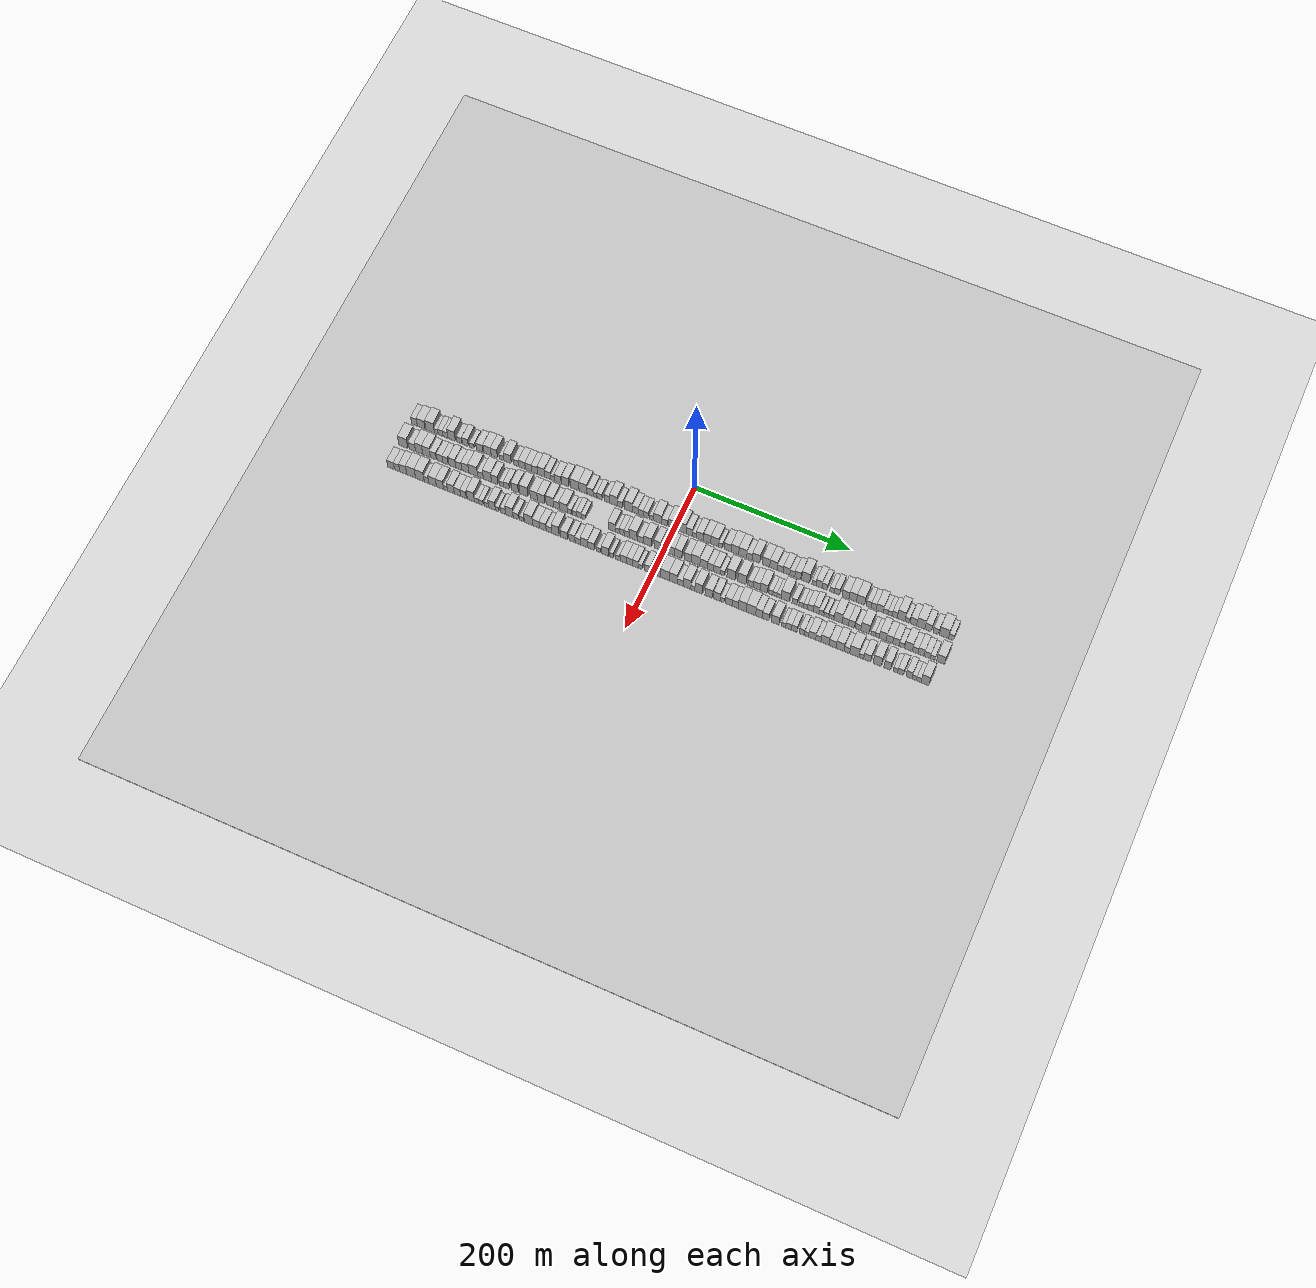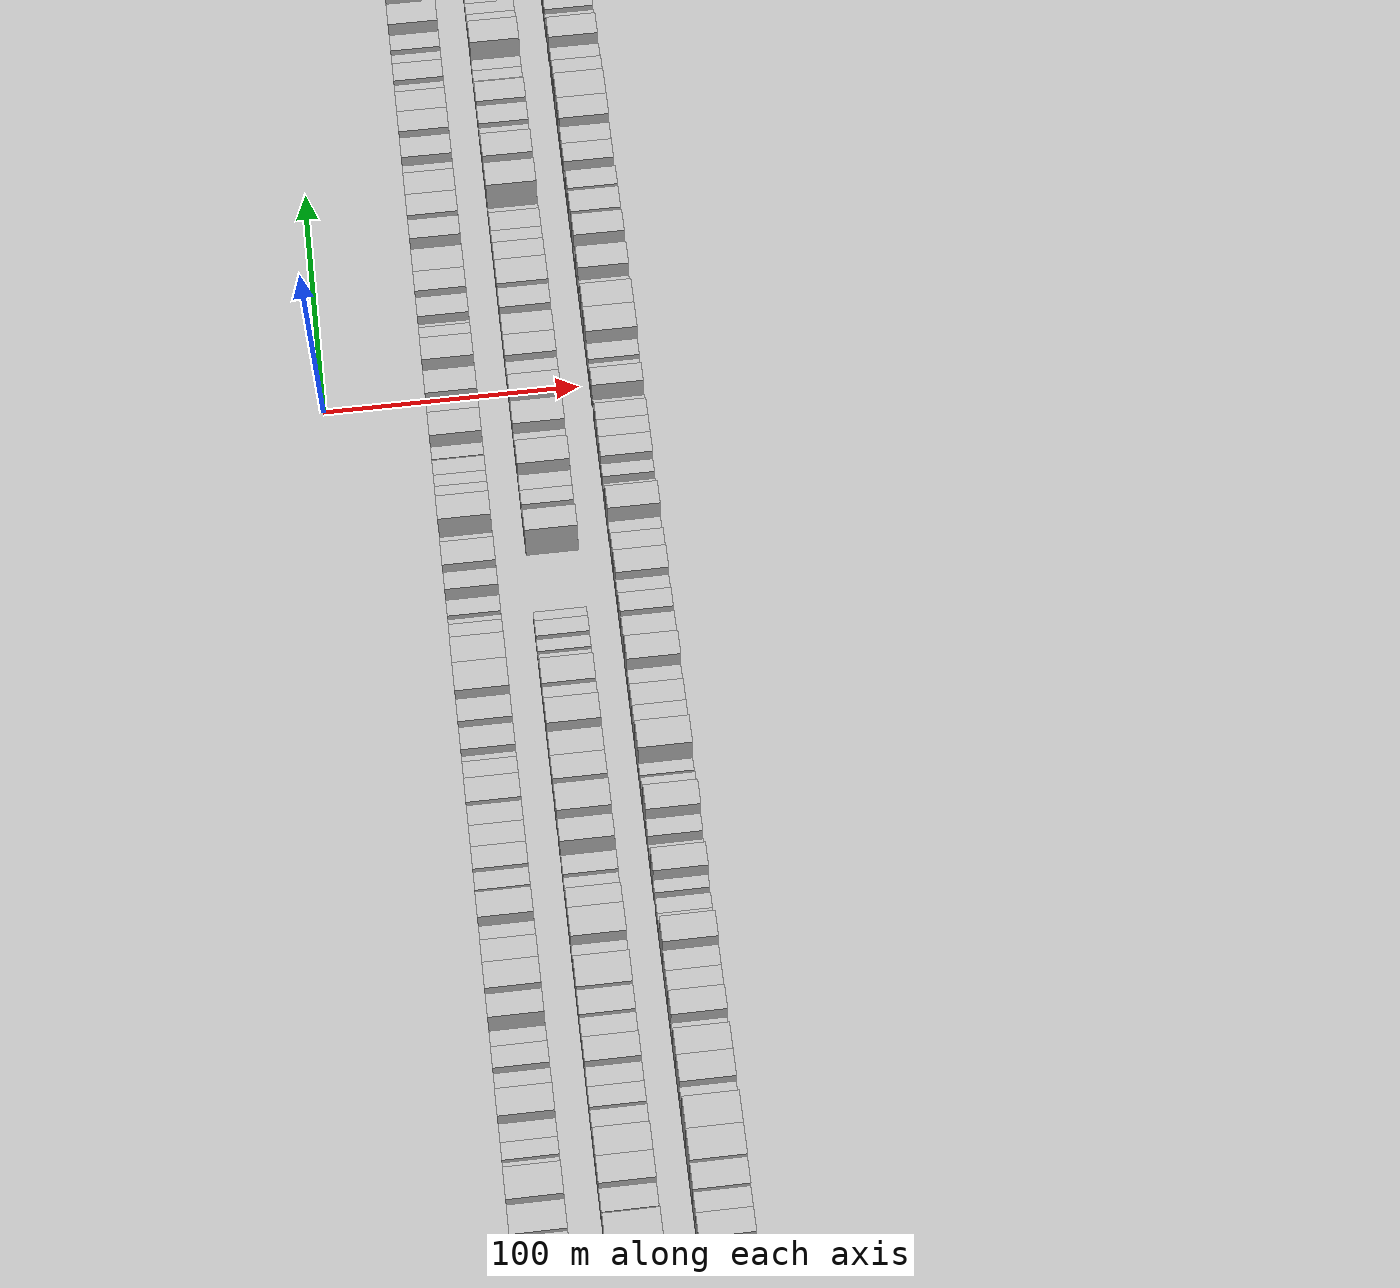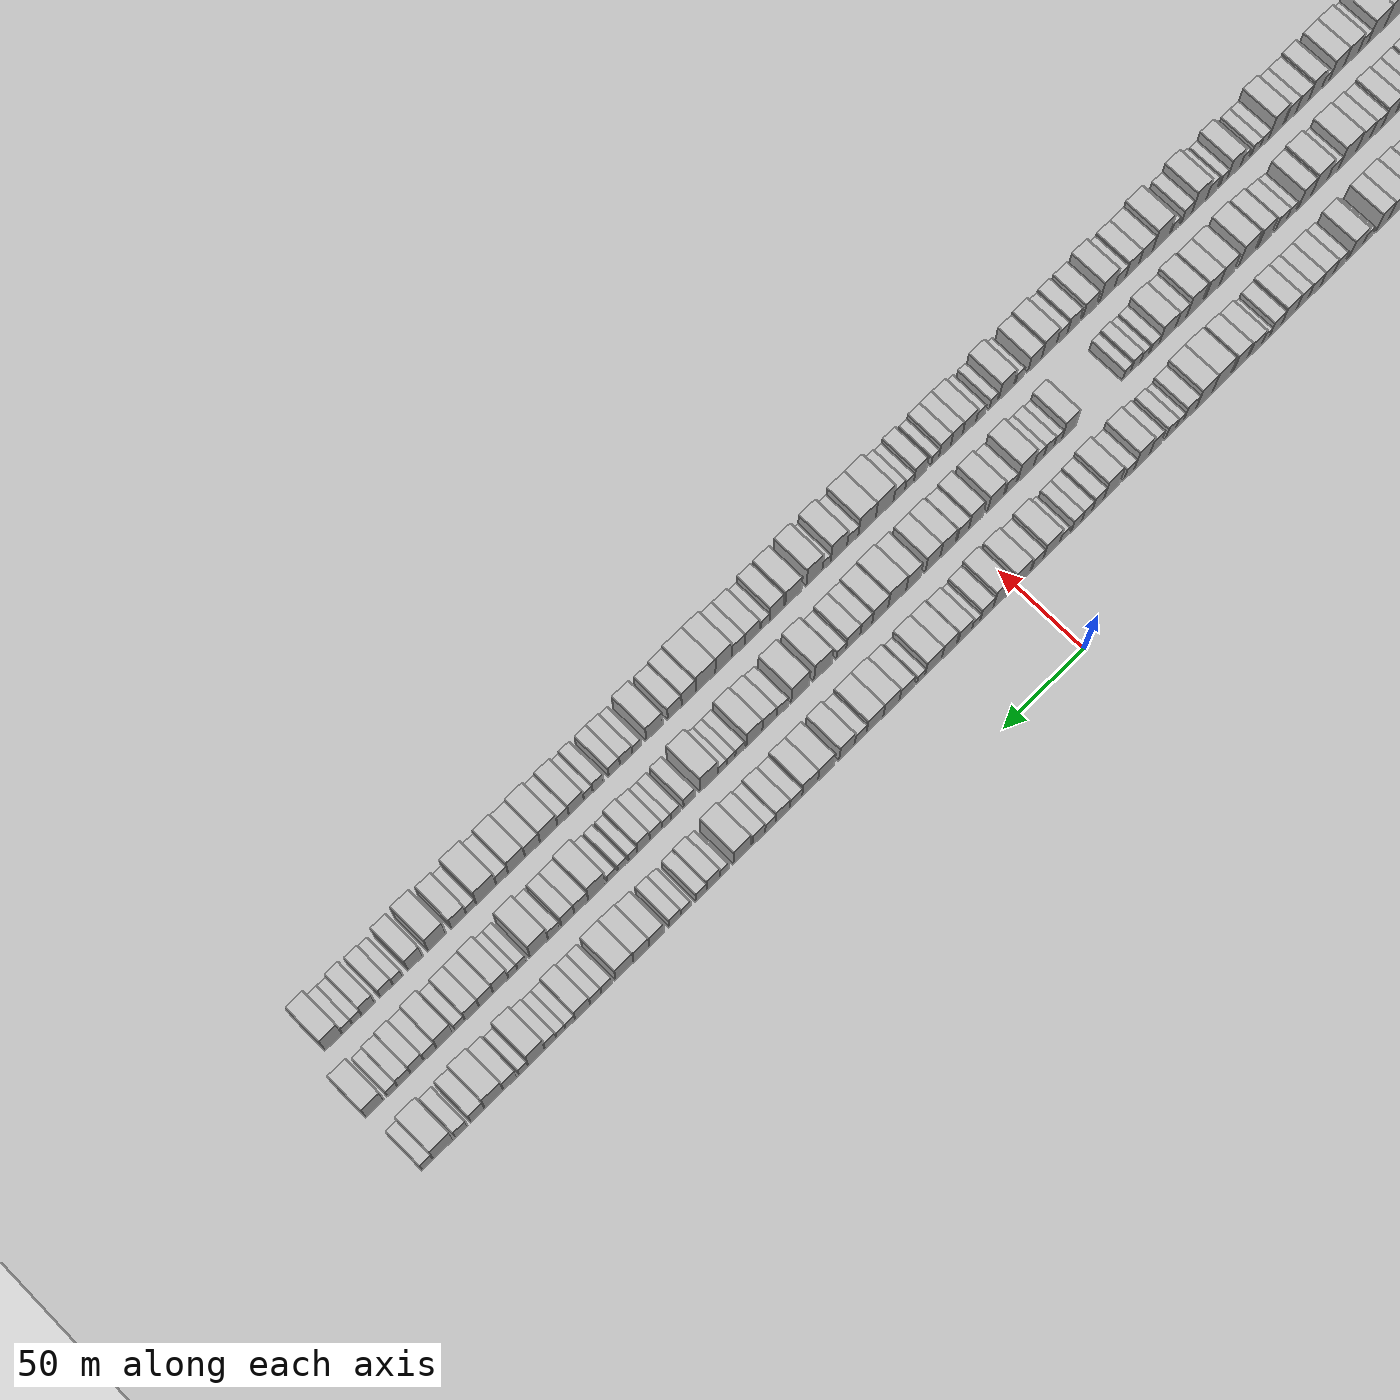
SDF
<?xml version="1.0" encoding="utf-8"?>

<sdf version="1.6">

   <world name="default">

      <gui fullscreen="0">

         <camera name="user_camera">

            <pose>-15 0 4.57585 0 0 0</pose>

            <view_controller>orbit</view_controller>

         </camera>

      </gui>

      <scene>

         <sky>

           <clouds>

             <speed>12</speed>

           </clouds>

         </sky>

         <ambient>0.4 0.4 0.4 1</ambient>

         <background>0.7 0.7 0.7 1</background>

         <shadows>1</shadows>

      </scene>

      <gravity>0 0 -9.8066</gravity>

      <magnetic_field>6e-06 2.3e-05 -4.2e-05</magnetic_field>

      <physics default="0" name="default_physics" type="ode">

         <ode>

            <solver>

               <type>quick</type>

               <iters>10</iters>

               <sor>1.0</sor>

               <use_dynamic_moi_rescaling>0</use_dynamic_moi_rescaling>

            </solver>

            <constraints>

               <cfm>0</cfm>

               <erp>0.2</erp>

               <contact_max_correcting_vel>100</contact_max_correcting_vel>

               <contact_surface_layer>0.001</contact_surface_layer>

            </constraints>

         </ode>

         <max_step_size>0.004</max_step_size>

         <real_time_factor>1</real_time_factor>

         <real_time_update_rate>250</real_time_update_rate>

      </physics>

      <light name="sun" type="directional">

         <cast_shadows>1</cast_shadows>

         <pose>0 0 10 0 0 0</pose>

         <diffuse>0.8 0.8 0.8 1</diffuse>

         <specular>0.2 0.2 0.2 1</specular>

         <attenuation>

            <range>1000</range>

            <constant>0.9</constant>

            <linear>0.01</linear>

            <quadratic>0.001</quadratic>

         </attenuation>

         <direction>-0.5 0.1 -0.9</direction>

      </light>

      <include>

         <name>ground_plane_1</name>

         <uri>model://HANNAS_ground_plane</uri>

         <pose>0 0 0  0 0 0</pose>

      </include>

      <include>

         <name>ground_plane_2</name>

         <uri>model://HANNAS_ground_plane</uri>

         <pose>100 0 0  0 0 0</pose>

      </include>

      <model name="building_1">

         <static>1</static>

         <pose frame="">50.0000 -343.1323 0 0.000000 0.000000 0.000000</pose>

         <link name="link">

            <pose frame="">0 0 9.00 0 0 0</pose>

            <collision name="collision">

               <geometry>

                  <box>

                     <size>20.0000 7.7355 18.0000</size>

                  </box>

               </geometry>

               <max_contacts>10</max_contacts>

               <surface>

                  <contact>

                     <ode/>

                  </contact>

                  <bounce/>

                  <friction>

                     <torsional>

                        <ode/>

                     </torsional>

                     <ode/>

                  </friction>

               </surface>

            </collision>

            <visual name="visual">

               <cast_shadows>0</cast_shadows>

               <geometry>

                  <box>

                     <size>20.0000 7.7355 18.0000</size>

                  </box>

               </geometry>

               <material>

                  <script>

                     <uri>model://HANNAS_wall/materials/scripts</uri>

                     <uri>model://HANNAS_wall/materials/textures</uri>

                     <name>vrc/HANNAS_wall</name>

                  </script>

               </material>

            </visual>

            <self_collide>0</self_collide>

            <enable_wind>0</enable_wind>

            <kinematic>0</kinematic>

         </link>

      </model>

      <model name="building_2">

         <static>1</static>

         <pose frame="">50.0000 -334.0682 0 0.000000 0.000000 0.000000</pose>

         <link name="link">

            <pose frame="">0 0 10.50 0 0 0</pose>

            <collision name="collision">

               <geometry>

                  <box>

                     <size>20.0000 10.3926 21.0000</size>

                  </box>

               </geometry>

               <max_contacts>10</max_contacts>

               <surface>

                  <contact>

                     <ode/>

                  </contact>

                  <bounce/>

                  <friction>

                     <torsional>

                        <ode/>

                     </torsional>

                     <ode/>

                  </friction>

               </surface>

            </collision>

            <visual name="visual">

               <cast_shadows>0</cast_shadows>

               <geometry>

                  <box>

                     <size>20.0000 10.3926 21.0000</size>

                  </box>

               </geometry>

               <material>

                  <script>

                     <uri>model://HANNAS_wall/materials/scripts</uri>

                     <uri>model://HANNAS_wall/materials/textures</uri>

                     <name>vrc/HANNAS_wall</name>

                  </script>

               </material>

            </visual>

            <self_collide>0</self_collide>

            <enable_wind>0</enable_wind>

            <kinematic>0</kinematic>

         </link>

      </model>

      <model name="building_3">

         <static>1</static>

         <pose frame="">50.0000 -322.1165 0 0.000000 0.000000 0.000000</pose>

         <link name="link">

            <pose frame="">0 0 12.00 0 0 0</pose>

            <collision name="collision">

               <geometry>

                  <box>

                     <size>20.0000 11.5109 24.0000</size>

                  </box>

               </geometry>

               <max_contacts>10</max_contacts>

               <surface>

                  <contact>

                     <ode/>

                  </contact>

                  <bounce/>

                  <friction>

                     <torsional>

                        <ode/>

                     </torsional>

                     <ode/>

                  </friction>

               </surface>

            </collision>

            <visual name="visual">

               <cast_shadows>0</cast_shadows>

               <geometry>

                  <box>

                     <size>20.0000 11.5109 24.0000</size>

                  </box>

               </geometry>

               <material>

                  <script>

                     <uri>model://HANNAS_wall/materials/scripts</uri>

                     <uri>model://HANNAS_wall/materials/textures</uri>

                     <name>vrc/HANNAS_wall</name>

                  </script>

               </material>

            </visual>

            <self_collide>0</self_collide>

            <enable_wind>0</enable_wind>

            <kinematic>0</kinematic>

         </link>

      </model>

      <model name="building_4">

         <static>1</static>

         <pose frame="">50.0000 -313.7867 0 0.000000 0.000000 0.000000</pose>

         <link name="link">

            <pose frame="">0 0 6.00 0 0 0</pose>

            <collision name="collision">

               <geometry>

                  <box>

                     <size>20.0000 5.1487 12.0000</size>

                  </box>

               </geometry>

               <max_contacts>10</max_contacts>

               <surface>

                  <contact>

                     <ode/>

                  </contact>

                  <bounce/>

                  <friction>

                     <torsional>

                        <ode/>

                     </torsional>

                     <ode/>

                  </friction>

               </surface>

            </collision>

            <visual name="visual">

               <cast_shadows>0</cast_shadows>

               <geometry>

                  <box>

                     <size>20.0000 5.1487 12.0000</size>

                  </box>

               </geometry>

               <material>

                  <script>

                     <uri>model://HANNAS_wall/materials/scripts</uri>

                     <uri>model://HANNAS_wall/materials/textures</uri>

                     <name>vrc/HANNAS_wall</name>

                  </script>

               </material>

            </visual>

            <self_collide>0</self_collide>

            <enable_wind>0</enable_wind>

            <kinematic>0</kinematic>

         </link>

      </model>

      <model name="building_5">

         <static>1</static>

         <pose frame="">50.0000 -308.0372 0 0.000000 0.000000 0.000000</pose>

         <link name="link">

            <pose frame="">0 0 7.50 0 0 0</pose>

            <collision name="collision">

               <geometry>

                  <box>

                     <size>20.0000 6.3502 15.0000</size>

                  </box>

               </geometry>

               <max_contacts>10</max_contacts>

               <surface>

                  <contact>

                     <ode/>

                  </contact>

                  <bounce/>

                  <friction>

                     <torsional>

                        <ode/>

                     </torsional>

                     <ode/>

                  </friction>

               </surface>

            </collision>

            <visual name="visual">

               <cast_shadows>0</cast_shadows>

               <geometry>

                  <box>

                     <size>20.0000 6.3502 15.0000</size>

                  </box>

               </geometry>

               <material>

                  <script>

                     <uri>model://HANNAS_wall/materials/scripts</uri>

                     <uri>model://HANNAS_wall/materials/textures</uri>

                     <name>vrc/HANNAS_wall</name>

                  </script>

               </material>

            </visual>

            <self_collide>0</self_collide>

            <enable_wind>0</enable_wind>

            <kinematic>0</kinematic>

         </link>

      </model>

      <model name="building_6">

         <static>1</static>

         <pose frame="">50.0000 -301.5189 0 0.000000 0.000000 0.000000</pose>

         <link name="link">

            <pose frame="">0 0 7.50 0 0 0</pose>

            <collision name="collision">

               <geometry>

                  <box>

                     <size>20.0000 6.6865 15.0000</size>

                  </box>

               </geometry>

               <max_contacts>10</max_contacts>

               <surface>

                  <contact>

                     <ode/>

                  </contact>

                  <bounce/>

                  <friction>

                     <torsional>

                        <ode/>

                     </torsional>

                     <ode/>

                  </friction>

               </surface>

            </collision>

            <visual name="visual">

               <cast_shadows>0</cast_shadows>

               <geometry>

                  <box>

                     <size>20.0000 6.6865 15.0000</size>

                  </box>

               </geometry>

               <material>

                  <script>

                     <uri>model://HANNAS_wall/materials/scripts</uri>

                     <uri>model://HANNAS_wall/materials/textures</uri>

                     <name>vrc/HANNAS_wall</name>

                  </script>

               </material>

            </visual>

            <self_collide>0</self_collide>

            <enable_wind>0</enable_wind>

            <kinematic>0</kinematic>

         </link>

      </model>

      <model name="building_7">

         <static>1</static>

         <pose frame="">50.0000 -293.2003 0 0.000000 0.000000 0.000000</pose>

         <link name="link">

            <pose frame="">0 0 12.00 0 0 0</pose>

            <collision name="collision">

               <geometry>

                  <box>

                     <size>20.0000 9.9508 24.0000</size>

                  </box>

               </geometry>

               <max_contacts>10</max_contacts>

               <surface>

                  <contact>

                     <ode/>

                  </contact>

                  <bounce/>

                  <friction>

                     <torsional>

                        <ode/>

                     </torsional>

                     <ode/>

                  </friction>

               </surface>

            </collision>

            <visual name="visual">

               <cast_shadows>0</cast_shadows>

               <geometry>

                  <box>

                     <size>20.0000 9.9508 24.0000</size>

                  </box>

               </geometry>

               <material>

                  <script>

                     <uri>model://HANNAS_wall/materials/scripts</uri>

                     <uri>model://HANNAS_wall/materials/textures</uri>

                     <name>vrc/HANNAS_wall</name>

                  </script>

               </material>

            </visual>

            <self_collide>0</self_collide>

            <enable_wind>0</enable_wind>

            <kinematic>0</kinematic>

         </link>

      </model>

      <model name="building_8">

         <static>1</static>

         <pose frame="">50.0000 -283.0246 0 0.000000 0.000000 0.000000</pose>

         <link name="link">

            <pose frame="">0 0 7.50 0 0 0</pose>

            <collision name="collision">

               <geometry>

                  <box>

                     <size>20.0000 6.4006 15.0000</size>

                  </box>

               </geometry>

               <max_contacts>10</max_contacts>

               <surface>

                  <contact>

                     <ode/>

                  </contact>

                  <bounce/>

                  <friction>

                     <torsional>

                        <ode/>

                     </torsional>

                     <ode/>

                  </friction>

               </surface>

            </collision>

            <visual name="visual">

               <cast_shadows>0</cast_shadows>

               <geometry>

                  <box>

                     <size>20.0000 6.4006 15.0000</size>

                  </box>

               </geometry>

               <material>

                  <script>

                     <uri>model://HANNAS_wall/materials/scripts</uri>

                     <uri>model://HANNAS_wall/materials/textures</uri>

                     <name>vrc/HANNAS_wall</name>

                  </script>

               </material>

            </visual>

            <self_collide>0</self_collide>

            <enable_wind>0</enable_wind>

            <kinematic>0</kinematic>

         </link>

      </model>

      <model name="building_9">

         <static>1</static>

         <pose frame="">50.0000 -274.8611 0 0.000000 0.000000 0.000000</pose>

         <link name="link">

            <pose frame="">0 0 9.00 0 0 0</pose>

            <collision name="collision">

               <geometry>

                  <box>

                     <size>20.0000 7.9264 18.0000</size>

                  </box>

               </geometry>

               <max_contacts>10</max_contacts>

               <surface>

                  <contact>

                     <ode/>

                  </contact>

                  <bounce/>

                  <friction>

                     <torsional>

                        <ode/>

                     </torsional>

                     <ode/>

                  </friction>

               </surface>

            </collision>

            <visual name="visual">

               <cast_shadows>0</cast_shadows>

               <geometry>

                  <box>

                     <size>20.0000 7.9264 18.0000</size>

                  </box>

               </geometry>

               <material>

                  <script>

                     <uri>model://HANNAS_wall/materials/scripts</uri>

                     <uri>model://HANNAS_wall/materials/textures</uri>

                     <name>vrc/HANNAS_wall</name>

                  </script>

               </material>

            </visual>

            <self_collide>0</self_collide>

            <enable_wind>0</enable_wind>

            <kinematic>0</kinematic>

         </link>

      </model>

      <model name="building_10">

         <static>1</static>

         <pose frame="">50.0000 -266.0002 0 0.000000 0.000000 0.000000</pose>

         <link name="link">

            <pose frame="">0 0 6.00 0 0 0</pose>

            <collision name="collision">

               <geometry>

                  <box>

                     <size>20.0000 5.7954 12.0000</size>

                  </box>

               </geometry>

               <max_contacts>10</max_contacts>

               <surface>

                  <contact>

                     <ode/>

                  </contact>

                  <bounce/>

                  <friction>

                     <torsional>

                        <ode/>

                     </torsional>

                     <ode/>

                  </friction>

               </surface>

            </collision>

            <visual name="visual">

               <cast_shadows>0</cast_shadows>

               <geometry>

                  <box>

                     <size>20.0000 5.7954 12.0000</size>

                  </box>

               </geometry>

               <material>

                  <script>

                     <uri>model://HANNAS_wall/materials/scripts</uri>

                     <uri>model://HANNAS_wall/materials/textures</uri>

                     <name>vrc/HANNAS_wall</name>

                  </script>

               </material>

            </visual>

            <self_collide>0</self_collide>

            <enable_wind>0</enable_wind>

            <kinematic>0</kinematic>

         </link>

      </model>

      <model name="building_11">

         <static>1</static>

         <pose frame="">50.0000 -255.7289 0 0.000000 0.000000 0.000000</pose>

         <link name="link">

            <pose frame="">0 0 9.00 0 0 0</pose>

            <collision name="collision">

               <geometry>

                  <box>

                     <size>20.0000 8.7473 18.0000</size>

                  </box>

               </geometry>

               <max_contacts>10</max_contacts>

               <surface>

                  <contact>

                     <ode/>

                  </contact>

                  <bounce/>

                  <friction>

                     <torsional>

                        <ode/>

                     </torsional>

                     <ode/>

                  </friction>

               </surface>

            </collision>

            <visual name="visual">

               <cast_shadows>0</cast_shadows>

               <geometry>

                  <box>

                     <size>20.0000 8.7473 18.0000</size>

                  </box>

               </geometry>

               <material>

                  <script>

                     <uri>model://HANNAS_wall/materials/scripts</uri>

                     <uri>model://HANNAS_wall/materials/textures</uri>

                     <name>vrc/HANNAS_wall</name>

                  </script>

               </material>

            </visual>

            <self_collide>0</self_collide>

            <enable_wind>0</enable_wind>

            <kinematic>0</kinematic>

         </link>

      </model>

      <model name="building_12">

         <static>1</static>

         <pose frame="">50.0000 -245.4436 0 0.000000 0.000000 0.000000</pose>

         <link name="link">

            <pose frame="">0 0 10.50 0 0 0</pose>

            <collision name="collision">

               <geometry>

                  <box>

                     <size>20.0000 9.8232 21.0000</size>

                  </box>

               </geometry>

               <max_contacts>10</max_contacts>

               <surface>

                  <contact>

                     <ode/>

                  </contact>

                  <bounce/>

                  <friction>

                     <torsional>

                        <ode/>

                     </torsional>

                     <ode/>

                  </friction>

               </surface>

            </collision>

            <visual name="visual">

               <cast_shadows>0</cast_shadows>

               <geometry>

                  <box>

                     <size>20.0000 9.8232 21.0000</size>

                  </box>

               </geometry>

               <material>

                  <script>

                     <uri>model://HANNAS_wall/materials/scripts</uri>

                     <uri>model://HANNAS_wall/materials/textures</uri>

                     <name>vrc/HANNAS_wall</name>

                  </script>

               </material>

            </visual>

            <self_collide>0</self_collide>

            <enable_wind>0</enable_wind>

            <kinematic>0</kinematic>

         </link>

      </model>

      <model name="building_13">

         <static>1</static>

         <pose frame="">50.0000 -236.3201 0 0.000000 0.000000 0.000000</pose>

         <link name="link">

            <pose frame="">0 0 10.50 0 0 0</pose>

            <collision name="collision">

               <geometry>

                  <box>

                     <size>20.0000 8.4239 21.0000</size>

                  </box>

               </geometry>

               <max_contacts>10</max_contacts>

               <surface>

                  <contact>

                     <ode/>

                  </contact>

                  <bounce/>

                  <friction>

                     <torsional>

                        <ode/>

                     </torsional>

                     <ode/>

                  </friction>

               </surface>

            </collision>

            <visual name="visual">

               <cast_shadows>0</cast_shadows>

               <geometry>

                  <box>

                     <size>20.0000 8.4239 21.0000</size>

                  </box>

               </geometry>

               <material>

                  <script>

                     <uri>model://HANNAS_wall/materials/scripts</uri>

                     <uri>model://HANNAS_wall/materials/textures</uri>

                     <name>vrc/HANNAS_wall</name>

                  </script>

               </material>

            </visual>

            <self_collide>0</self_collide>

            <enable_wind>0</enable_wind>

            <kinematic>0</kinematic>

         </link>

      </model>

      <model name="building_14">

         <static>1</static>

         <pose frame="">50.0000 -226.3254 0 0.000000 0.000000 0.000000</pose>

         <link name="link">

            <pose frame="">0 0 6.00 0 0 0</pose>

            <collision name="collision">

               <geometry>

                  <box>

                     <size>20.0000 5.5656 12.0000</size>

                  </box>

               </geometry>

               <max_contacts>10</max_contacts>

               <surface>

                  <contact>

                     <ode/>

                  </contact>

                  <bounce/>

                  <friction>

                     <torsional>

                        <ode/>

                     </torsional>

                     <ode/>

                  </friction>

               </surface>

            </collision>

            <visual name="visual">

               <cast_shadows>0</cast_shadows>

               <geometry>

                  <box>

                     <size>20.0000 5.5656 12.0000</size>

                  </box>

               </geometry>

               <material>

                  <script>

                     <uri>model://HANNAS_wall/materials/scripts</uri>

                     <uri>model://HANNAS_wall/materials/textures</uri>

                     <name>vrc/HANNAS_wall</name>

                  </script>

               </material>

            </visual>

            <self_collide>0</self_collide>

            <enable_wind>0</enable_wind>

            <kinematic>0</kinematic>

         </link>

      </model>

      <model name="building_15">

         <static>1</static>

         <pose frame="">50.0000 -218.6928 0 0.000000 0.000000 0.000000</pose>

         <link name="link">

            <pose frame="">0 0 10.50 0 0 0</pose>

            <collision name="collision">

               <geometry>

                  <box>

                     <size>20.0000 9.6996 21.0000</size>

                  </box>

               </geometry>

               <max_contacts>10</max_contacts>

               <surface>

                  <contact>

                     <ode/>

                  </contact>

                  <bounce/>

                  <friction>

                     <torsional>

                        <ode/>

                     </torsional>

                     <ode/>

                  </friction>

               </surface>

            </collision>

            <visual name="visual">

               <cast_shadows>0</cast_shadows>

               <geometry>

                  <box>

                     <size>20.0000 9.6996 21.0000</size>

                  </box>

               </geometry>

               <material>

                  <script>

                     <uri>model://HANNAS_wall/materials/scripts</uri>

                     <uri>model://HANNAS_wall/materials/textures</uri>

                     <name>vrc/HANNAS_wall</name>

                  </script>

               </material>

            </visual>

            <self_collide>0</self_collide>

            <enable_wind>0</enable_wind>

            <kinematic>0</kinematic>

         </link>

      </model>

      <model name="building_16">

         <static>1</static>

         <pose frame="">50.0000 -207.3635 0 0.000000 0.000000 0.000000</pose>

         <link name="link">

            <pose frame="">0 0 7.50 0 0 0</pose>

            <collision name="collision">

               <geometry>

                  <box>

                     <size>20.0000 6.9588 15.0000</size>

                  </box>

               </geometry>

               <max_contacts>10</max_contacts>

               <surface>

                  <contact>

                     <ode/>

                  </contact>

                  <bounce/>

                  <friction>

                     <torsional>

                        <ode/>

                     </torsional>

                     <ode/>

                  </friction>

               </surface>

            </collision>

            <visual name="visual">

               <cast_shadows>0</cast_shadows>

               <geometry>

                  <box>

                     <size>20.0000 6.9588 15.0000</size>

                  </box>

               </geometry>

               <material>

                  <script>

                     <uri>model://HANNAS_wall/materials/scripts</uri>

                     <uri>model://HANNAS_wall/materials/textures</uri>

                     <name>vrc/HANNAS_wall</name>

                  </script>

               </material>

            </visual>

            <self_collide>0</self_collide>

            <enable_wind>0</enable_wind>

            <kinematic>0</kinematic>

         </link>

      </model>

      <model name="building_17">

         <static>1</static>

         <pose frame="">50.0000 -199.5270 0 0.000000 0.000000 0.000000</pose>

         <link name="link">

            <pose frame="">0 0 9.00 0 0 0</pose>

            <collision name="collision">

               <geometry>

                  <box>

                     <size>20.0000 8.7142 18.0000</size>

                  </box>

               </geometry>

               <max_contacts>10</max_contacts>

               <surface>

                  <contact>

                     <ode/>

                  </contact>

                  <bounce/>

                  <friction>

                     <torsional>

                        <ode/>

                     </torsional>

                     <ode/>

                  </friction>

               </surface>

            </collision>

            <visual name="visual">

               <cast_shadows>0</cast_shadows>

               <geometry>

                  <box>

                     <size>20.0000 8.7142 18.0000</size>

                  </box>

               </geometry>

               <material>

                  <script>

                     <uri>model://HANNAS_wall/materials/scripts</uri>

                     <uri>model://HANNAS_wall/materials/textures</uri>

                     <name>vrc/HANNAS_wall</name>

                  </script>

               </material>

            </visual>

            <self_collide>0</self_collide>

            <enable_wind>0</enable_wind>

            <kinematic>0</kinematic>

         </link>

      </model>

      <model name="building_18">

         <static>1</static>

         <pose frame="">50.0000 -191.0244 0 0.000000 0.000000 0.000000</pose>

         <link name="link">

            <pose frame="">0 0 9.00 0 0 0</pose>

            <collision name="collision">

               <geometry>

                  <box>

                     <size>20.0000 8.2911 18.0000</size>

                  </box>

               </geometry>

               <max_contacts>10</max_contacts>

               <surface>

                  <contact>

                     <ode/>

                  </contact>

                  <bounce/>

                  <friction>

                     <torsional>

                        <ode/>

                     </torsional>

                     <ode/>

                  </friction>

               </surface>

            </collision>

            <visual name="visual">

               <cast_shadows>0</cast_shadows>

               <geometry>

                  <box>

                     <size>20.0000 8.2911 18.0000</size>

                  </box>

               </geometry>

               <material>

                  <script>

                     <uri>model://HANNAS_wall/materials/scripts</uri>

                     <uri>model://HANNAS_wall/materials/textures</uri>

                     <name>vrc/HANNAS_wall</name>

                  </script>

               </material>

            </visual>

            <self_collide>0</self_collide>

            <enable_wind>0</enable_wind>

            <kinematic>0</kinematic>

         </link>

      </model>

      <model name="building_19">

         <static>1</static>

         <pose frame="">50.0000 -182.9614 0 0.000000 0.000000 0.000000</pose>

         <link name="link">

            <pose frame="">0 0 9.00 0 0 0</pose>

            <collision name="collision">

               <geometry>

                  <box>

                     <size>20.0000 7.8348 18.0000</size>

                  </box>

               </geometry>

               <max_contacts>10</max_contacts>

               <surface>

                  <contact>

                     <ode/>

                  </contact>

                  <bounce/>

                  <friction>

                     <torsional>

                        <ode/>

                     </torsional>

                     <ode/>

                  </friction>

               </surface>

            </collision>

            <visual name="visual">

               <cast_shadows>0</cast_shadows>

               <geometry>

                  <box>

                     <size>20.0000 7.8348 18.0000</size>

                  </box>

               </geometry>

               <material>

                  <script>

                     <uri>model://HANNAS_wall/materials/scripts</uri>

                     <uri>model://HANNAS_wall/materials/textures</uri>

                     <name>vrc/HANNAS_wall</name>

                  </script>

               </material>

            </visual>

            <self_collide>0</self_collide>

            <enable_wind>0</enable_wind>

            <kinematic>0</kinematic>

         </link>

      </model>

      <model name="building_20">

         <static>1</static>

         <pose frame="">50.0000 -174.2589 0 0.000000 0.000000 0.000000</pose>

         <link name="link">

            <pose frame="">0 0 10.50 0 0 0</pose>

            <collision name="collision">

               <geometry>

                  <box>

                     <size>20.0000 9.5702 21.0000</size>

                  </box>

               </geometry>

               <max_contacts>10</max_contacts>

               <surface>

                  <contact>

                     <ode/>

                  </contact>

                  <bounce/>

                  <friction>

                     <torsional>

                        <ode/>

                     </torsional>

                     <ode/>

                  </friction>

               </surface>

            </collision>

            <visual name="visual">

               <cast_shadows>0</cast_shadows>

               <geometry>

                  <box>

                     <size>20.0000 9.5702 21.0000</size>

                  </box>

               </geometry>

               <material>

                  <script>

                     <uri>model://HANNAS_wall/materials/scripts</uri>

                     <uri>model://HANNAS_wall/materials/textures</uri>

                     <name>vrc/HANNAS_wall</name>

                  </script>

               </material>

            </visual>

            <self_collide>0</self_collide>

            <enable_wind>0</enable_wind>

            <kinematic>0</kinematic>

         </link>

      </model>

      <model name="building_21">

         <static>1</static>

         <pose frame="">50.0000 -165.5747 0 0.000000 0.000000 0.000000</pose>

         <link name="link">

            <pose frame="">0 0 9.00 0 0 0</pose>

            <collision name="collision">

               <geometry>

                  <box>

                     <size>20.0000 7.7982 18.0000</size>

                  </box>

               </geometry>

               <max_contacts>10</max_contacts>

               <surface>

                  <contact>

                     <ode/>

                  </contact>

                  <bounce/>

                  <friction>

                     <torsional>

                        <ode/>

                     </torsional>

                     <ode/>

                  </friction>

               </surface>

            </collision>

            <visual name="visual">

               <cast_shadows>0</cast_shadows>

               <geometry>

                  <box>

                     <size>20.0000 7.7982 18.0000</size>

                  </box>

               </geometry>

               <material>

                  <script>

                     <uri>model://HANNAS_wall/materials/scripts</uri>

                     <uri>model://HANNAS_wall/materials/textures</uri>

                     <name>vrc/HANNAS_wall</name>

                  </script>

               </material>

            </visual>

            <self_collide>0</self_collide>

            <enable_wind>0</enable_wind>

            <kinematic>0</kinematic>

         </link>

      </model>

      <model name="building_22">

         <static>1</static>

         <pose frame="">50.0000 -159.2632 0 0.000000 0.000000 0.000000</pose>

         <link name="link">

            <pose frame="">0 0 6.00 0 0 0</pose>

            <collision name="collision">

               <geometry>

                  <box>

                     <size>20.0000 4.8246 12.0000</size>

                  </box>

               </geometry>

               <max_contacts>10</max_contacts>

               <surface>

                  <contact>

                     <ode/>

                  </contact>

                  <bounce/>

                  <friction>

                     <torsional>

                        <ode/>

                     </torsional>

                     <ode/>

                  </friction>

               </surface>

            </collision>

            <visual name="visual">

               <cast_shadows>0</cast_shadows>

               <geometry>

                  <box>

                     <size>20.0000 4.8246 12.0000</size>

                  </box>

               </geometry>

               <material>

                  <script>

                     <uri>model://HANNAS_wall/materials/scripts</uri>

                     <uri>model://HANNAS_wall/materials/textures</uri>

                     <name>vrc/HANNAS_wall</name>

                  </script>

               </material>

            </visual>

            <self_collide>0</self_collide>

            <enable_wind>0</enable_wind>

            <kinematic>0</kinematic>

         </link>

      </model>

      <model name="building_23">

         <static>1</static>

         <pose frame="">50.0000 -152.3825 0 0.000000 0.000000 0.000000</pose>

         <link name="link">

            <pose frame="">0 0 9.00 0 0 0</pose>

            <collision name="collision">

               <geometry>

                  <box>

                     <size>20.0000 8.9368 18.0000</size>

                  </box>

               </geometry>

               <max_contacts>10</max_contacts>

               <surface>

                  <contact>

                     <ode/>

                  </contact>

                  <bounce/>

                  <friction>

                     <torsional>

                        <ode/>

                     </torsional>

                     <ode/>

                  </friction>

               </surface>

            </collision>

            <visual name="visual">

               <cast_shadows>0</cast_shadows>

               <geometry>

                  <box>

                     <size>20.0000 8.9368 18.0000</size>

                  </box>

               </geometry>

               <material>

                  <script>

                     <uri>model://HANNAS_wall/materials/scripts</uri>

                     <uri>model://HANNAS_wall/materials/textures</uri>

                     <name>vrc/HANNAS_wall</name>

                  </script>

               </material>

            </visual>

            <self_collide>0</self_collide>

            <enable_wind>0</enable_wind>

            <kinematic>0</kinematic>

         </link>

      </model>

      <model name="building_24">

         <static>1</static>

         <pose frame="">50.0000 -142.3646 0 0.000000 0.000000 0.000000</pose>

         <link name="link">

            <pose frame="">0 0 10.50 0 0 0</pose>

            <collision name="collision">

               <geometry>

                  <box>

                     <size>20.0000 9.0991 21.0000</size>

                  </box>

               </geometry>

               <max_contacts>10</max_contacts>

               <surface>

                  <contact>

                     <ode/>

                  </contact>

                  <bounce/>

                  <friction>

                     <torsional>

                        <ode/>

                     </torsional>

                     <ode/>

                  </friction>

               </surface>

            </collision>

            <visual name="visual">

               <cast_shadows>0</cast_shadows>

               <geometry>

                  <box>

                     <size>20.0000 9.0991 21.0000</size>

                  </box>

               </geometry>

               <material>

                  <script>

                     <uri>model://HANNAS_wall/materials/scripts</uri>

                     <uri>model://HANNAS_wall/materials/textures</uri>

                     <name>vrc/HANNAS_wall</name>

                  </script>

               </material>

            </visual>

            <self_collide>0</self_collide>

            <enable_wind>0</enable_wind>

            <kinematic>0</kinematic>

         </link>

      </model>

      <model name="building_25">

         <static>1</static>

         <pose frame="">50.0000 -130.0596 0 0.000000 0.000000 0.000000</pose>

         <link name="link">

            <pose frame="">0 0 12.00 0 0 0</pose>

            <collision name="collision">

               <geometry>

                  <box>

                     <size>20.0000 11.5109 24.0000</size>

                  </box>

               </geometry>

               <max_contacts>10</max_contacts>

               <surface>

                  <contact>

                     <ode/>

                  </contact>

                  <bounce/>

                  <friction>

                     <torsional>

                        <ode/>

                     </torsional>

                     <ode/>

                  </friction>

               </surface>

            </collision>

            <visual name="visual">

               <cast_shadows>0</cast_shadows>

               <geometry>

                  <box>

                     <size>20.0000 11.5109 24.0000</size>

                  </box>

               </geometry>

               <material>

                  <script>

                     <uri>model://HANNAS_wall/materials/scripts</uri>

                     <uri>model://HANNAS_wall/materials/textures</uri>

                     <name>vrc/HANNAS_wall</name>

                  </script>

               </material>

            </visual>

            <self_collide>0</self_collide>

            <enable_wind>0</enable_wind>

            <kinematic>0</kinematic>

         </link>

      </model>

      <model name="building_26">

         <static>1</static>

         <pose frame="">50.0000 -119.1078 0 0.000000 0.000000 0.000000</pose>

         <link name="link">

            <pose frame="">0 0 12.00 0 0 0</pose>

            <collision name="collision">

               <geometry>

                  <box>

                     <size>20.0000 10.3928 24.0000</size>

                  </box>

               </geometry>

               <max_contacts>10</max_contacts>

               <surface>

                  <contact>

                     <ode/>

                  </contact>

                  <bounce/>

                  <friction>

                     <torsional>

                        <ode/>

                     </torsional>

                     <ode/>

                  </friction>

               </surface>

            </collision>

            <visual name="visual">

               <cast_shadows>0</cast_shadows>

               <geometry>

                  <box>

                     <size>20.0000 10.3928 24.0000</size>

                  </box>

               </geometry>

               <material>

                  <script>

                     <uri>model://HANNAS_wall/materials/scripts</uri>

                     <uri>model://HANNAS_wall/materials/textures</uri>

                     <name>vrc/HANNAS_wall</name>

                  </script>

               </material>

            </visual>

            <self_collide>0</self_collide>

            <enable_wind>0</enable_wind>

            <kinematic>0</kinematic>

         </link>

      </model>

      <model name="building_27">

         <static>1</static>

         <pose frame="">50.0000 -109.8348 0 0.000000 0.000000 0.000000</pose>

         <link name="link">

            <pose frame="">0 0 9.00 0 0 0</pose>

            <collision name="collision">

               <geometry>

                  <box>

                     <size>20.0000 8.1531 18.0000</size>

                  </box>

               </geometry>

               <max_contacts>10</max_contacts>

               <surface>

                  <contact>

                     <ode/>

                  </contact>

                  <bounce/>

                  <friction>

                     <torsional>

                        <ode/>

                     </torsional>

                     <ode/>

                  </friction>

               </surface>

            </collision>

            <visual name="visual">

               <cast_shadows>0</cast_shadows>

               <geometry>

                  <box>

                     <size>20.0000 8.1531 18.0000</size>

                  </box>

               </geometry>

               <material>

                  <script>

                     <uri>model://HANNAS_wall/materials/scripts</uri>

                     <uri>model://HANNAS_wall/materials/textures</uri>

                     <name>vrc/HANNAS_wall</name>

                  </script>

               </material>

            </visual>

            <self_collide>0</self_collide>

            <enable_wind>0</enable_wind>

            <kinematic>0</kinematic>

         </link>

      </model>

      <model name="building_28">

         <static>1</static>

         <pose frame="">50.0000 -103.2867 0 0.000000 0.000000 0.000000</pose>

         <link name="link">

            <pose frame="">0 0 6.00 0 0 0</pose>

            <collision name="collision">

               <geometry>

                  <box>

                     <size>20.0000 4.9432 12.0000</size>

                  </box>

               </geometry>

               <max_contacts>10</max_contacts>

               <surface>

                  <contact>

                     <ode/>

                  </contact>

                  <bounce/>

                  <friction>

                     <torsional>

                        <ode/>

                     </torsional>

                     <ode/>

                  </friction>

               </surface>

            </collision>

            <visual name="visual">

               <cast_shadows>0</cast_shadows>

               <geometry>

                  <box>

                     <size>20.0000 4.9432 12.0000</size>

                  </box>

               </geometry>

               <material>

                  <script>

                     <uri>model://HANNAS_wall/materials/scripts</uri>

                     <uri>model://HANNAS_wall/materials/textures</uri>

                     <name>vrc/HANNAS_wall</name>

                  </script>

               </material>

            </visual>

            <self_collide>0</self_collide>

            <enable_wind>0</enable_wind>

            <kinematic>0</kinematic>

         </link>

      </model>

      <model name="building_29">

         <static>1</static>

         <pose frame="">50.0000 -97.4903 0 0.000000 0.000000 0.000000</pose>

         <link name="link">

            <pose frame="">0 0 7.50 0 0 0</pose>

            <collision name="collision">

               <geometry>

                  <box>

                     <size>20.0000 6.6497 15.0000</size>

                  </box>

               </geometry>

               <max_contacts>10</max_contacts>

               <surface>

                  <contact>

                     <ode/>

                  </contact>

                  <bounce/>

                  <friction>

                     <torsional>

                        <ode/>

                     </torsional>

                     <ode/>

                  </friction>

               </surface>

            </collision>

            <visual name="visual">

               <cast_shadows>0</cast_shadows>

               <geometry>

                  <box>

                     <size>20.0000 6.6497 15.0000</size>

                  </box>

               </geometry>

               <material>

                  <script>

                     <uri>model://HANNAS_wall/materials/scripts</uri>

                     <uri>model://HANNAS_wall/materials/textures</uri>

                     <name>vrc/HANNAS_wall</name>

                  </script>

               </material>

            </visual>

            <self_collide>0</self_collide>

            <enable_wind>0</enable_wind>

            <kinematic>0</kinematic>

         </link>

      </model>

      <model name="building_30">

         <static>1</static>

         <pose frame="">50.0000 -87.5600 0 0.000000 0.000000 0.000000</pose>

         <link name="link">

            <pose frame="">0 0 9.00 0 0 0</pose>

            <collision name="collision">

               <geometry>

                  <box>

                     <size>20.0000 7.2110 18.0000</size>

                  </box>

               </geometry>

               <max_contacts>10</max_contacts>

               <surface>

                  <contact>

                     <ode/>

                  </contact>

                  <bounce/>

                  <friction>

                     <torsional>

                        <ode/>

                     </torsional>

                     <ode/>

                  </friction>

               </surface>

            </collision>

            <visual name="visual">

               <cast_shadows>0</cast_shadows>

               <geometry>

                  <box>

                     <size>20.0000 7.2110 18.0000</size>

                  </box>

               </geometry>

               <material>

                  <script>

                     <uri>model://HANNAS_wall/materials/scripts</uri>

                     <uri>model://HANNAS_wall/materials/textures</uri>

                     <name>vrc/HANNAS_wall</name>

                  </script>

               </material>

            </visual>

            <self_collide>0</self_collide>

            <enable_wind>0</enable_wind>

            <kinematic>0</kinematic>

         </link>

      </model>

      <model name="building_31">

         <static>1</static>

         <pose frame="">50.0000 -79.0371 0 0.000000 0.000000 0.000000</pose>

         <link name="link">

            <pose frame="">0 0 12.00 0 0 0</pose>

            <collision name="collision">

               <geometry>

                  <box>

                     <size>20.0000 9.8348 24.0000</size>

                  </box>

               </geometry>

               <max_contacts>10</max_contacts>

               <surface>

                  <contact>

                     <ode/>

                  </contact>

                  <bounce/>

                  <friction>

                     <torsional>

                        <ode/>

                     </torsional>

                     <ode/>

                  </friction>

               </surface>

            </collision>

            <visual name="visual">

               <cast_shadows>0</cast_shadows>

               <geometry>

                  <box>

                     <size>20.0000 9.8348 24.0000</size>

                  </box>

               </geometry>

               <material>

                  <script>

                     <uri>model://HANNAS_wall/materials/scripts</uri>

                     <uri>model://HANNAS_wall/materials/textures</uri>

                     <name>vrc/HANNAS_wall</name>

                  </script>

               </material>

            </visual>

            <self_collide>0</self_collide>

            <enable_wind>0</enable_wind>

            <kinematic>0</kinematic>

         </link>

      </model>

      <model name="building_32">

         <static>1</static>

         <pose frame="">50.0000 -70.8369 0 0.000000 0.000000 0.000000</pose>

         <link name="link">

            <pose frame="">0 0 7.50 0 0 0</pose>

            <collision name="collision">

               <geometry>

                  <box>

                     <size>20.0000 6.5655 15.0000</size>

                  </box>

               </geometry>

               <max_contacts>10</max_contacts>

               <surface>

                  <contact>

                     <ode/>

                  </contact>

                  <bounce/>

                  <friction>

                     <torsional>

                        <ode/>

                     </torsional>

                     <ode/>

                  </friction>

               </surface>

            </collision>

            <visual name="visual">

               <cast_shadows>0</cast_shadows>

               <geometry>

                  <box>

                     <size>20.0000 6.5655 15.0000</size>

                  </box>

               </geometry>

               <material>

                  <script>

                     <uri>model://HANNAS_wall/materials/scripts</uri>

                     <uri>model://HANNAS_wall/materials/textures</uri>

                     <name>vrc/HANNAS_wall</name>

                  </script>

               </material>

            </visual>

            <self_collide>0</self_collide>

            <enable_wind>0</enable_wind>

            <kinematic>0</kinematic>

         </link>

      </model>

      <model name="building_33">

         <static>1</static>

         <pose frame="">50.0000 -59.5603 0 0.000000 0.000000 0.000000</pose>

         <link name="link">

            <pose frame="">0 0 12.00 0 0 0</pose>

            <collision name="collision">

               <geometry>

                  <box>

                     <size>20.0000 9.9878 24.0000</size>

                  </box>

               </geometry>

               <max_contacts>10</max_contacts>

               <surface>

                  <contact>

                     <ode/>

                  </contact>

                  <bounce/>

                  <friction>

                     <torsional>

                        <ode/>

                     </torsional>

                     <ode/>

                  </friction>

               </surface>

            </collision>

            <visual name="visual">

               <cast_shadows>0</cast_shadows>

               <geometry>

                  <box>

                     <size>20.0000 9.9878 24.0000</size>

                  </box>

               </geometry>

               <material>

                  <script>

                     <uri>model://HANNAS_wall/materials/scripts</uri>

                     <uri>model://HANNAS_wall/materials/textures</uri>

                     <name>vrc/HANNAS_wall</name>

                  </script>

               </material>

            </visual>

            <self_collide>0</self_collide>

            <enable_wind>0</enable_wind>

            <kinematic>0</kinematic>

         </link>

      </model>

      <model name="building_34">

         <static>1</static>

         <pose frame="">50.0000 -50.9068 0 0.000000 0.000000 0.000000</pose>

         <link name="link">

            <pose frame="">0 0 9.00 0 0 0</pose>

            <collision name="collision">

               <geometry>

                  <box>

                     <size>20.0000 7.3193 18.0000</size>

                  </box>

               </geometry>

               <max_contacts>10</max_contacts>

               <surface>

                  <contact>

                     <ode/>

                  </contact>

                  <bounce/>

                  <friction>

                     <torsional>

                        <ode/>

                     </torsional>

                     <ode/>

                  </friction>

               </surface>

            </collision>

            <visual name="visual">

               <cast_shadows>0</cast_shadows>

               <geometry>

                  <box>

                     <size>20.0000 7.3193 18.0000</size>

                  </box>

               </geometry>

               <material>

                  <script>

                     <uri>model://HANNAS_wall/materials/scripts</uri>

                     <uri>model://HANNAS_wall/materials/textures</uri>

                     <name>vrc/HANNAS_wall</name>

                  </script>

               </material>

            </visual>

            <self_collide>0</self_collide>

            <enable_wind>0</enable_wind>

            <kinematic>0</kinematic>

         </link>

      </model>

      <model name="building_35">

         <static>1</static>

         <pose frame="">50.0000 -44.0007 0 0.000000 0.000000 0.000000</pose>

         <link name="link">

            <pose frame="">0 0 7.50 0 0 0</pose>

            <collision name="collision">

               <geometry>

                  <box>

                     <size>20.0000 6.4929 15.0000</size>

                  </box>

               </geometry>

               <max_contacts>10</max_contacts>

               <surface>

                  <contact>

                     <ode/>

                  </contact>

                  <bounce/>

                  <friction>

                     <torsional>

                        <ode/>

                     </torsional>

                     <ode/>

                  </friction>

               </surface>

            </collision>

            <visual name="visual">

               <cast_shadows>0</cast_shadows>

               <geometry>

                  <box>

                     <size>20.0000 6.4929 15.0000</size>

                  </box>

               </geometry>

               <material>

                  <script>

                     <uri>model://HANNAS_wall/materials/scripts</uri>

                     <uri>model://HANNAS_wall/materials/textures</uri>

                     <name>vrc/HANNAS_wall</name>

                  </script>

               </material>

            </visual>

            <self_collide>0</self_collide>

            <enable_wind>0</enable_wind>

            <kinematic>0</kinematic>

         </link>

      </model>

      <model name="building_36">

         <static>1</static>

         <pose frame="">50.0000 -37.5284 0 0.000000 0.000000 0.000000</pose>

         <link name="link">

            <pose frame="">0 0 7.50 0 0 0</pose>

            <collision name="collision">

               <geometry>

                  <box>

                     <size>20.0000 6.4517 15.0000</size>

                  </box>

               </geometry>

               <max_contacts>10</max_contacts>

               <surface>

                  <contact>

                     <ode/>

                  </contact>

                  <bounce/>

                  <friction>

                     <torsional>

                        <ode/>

                     </torsional>

                     <ode/>

                  </friction>

               </surface>

            </collision>

            <visual name="visual">

               <cast_shadows>0</cast_shadows>

               <geometry>

                  <box>

                     <size>20.0000 6.4517 15.0000</size>

                  </box>

               </geometry>

               <material>

                  <script>

                     <uri>model://HANNAS_wall/materials/scripts</uri>

                     <uri>model://HANNAS_wall/materials/textures</uri>

                     <name>vrc/HANNAS_wall</name>

                  </script>

               </material>

            </visual>

            <self_collide>0</self_collide>

            <enable_wind>0</enable_wind>

            <kinematic>0</kinematic>

         </link>

      </model>

      <model name="building_37">

         <static>1</static>

         <pose frame="">50.0000 -29.5365 0 0.000000 0.000000 0.000000</pose>

         <link name="link">

            <pose frame="">0 0 6.00 0 0 0</pose>

            <collision name="collision">

               <geometry>

                  <box>

                     <size>20.0000 5.5320 12.0000</size>

                  </box>

               </geometry>

               <max_contacts>10</max_contacts>

               <surface>

                  <contact>

                     <ode/>

                  </contact>

                  <bounce/>

                  <friction>

                     <torsional>

                        <ode/>

                     </torsional>

                     <ode/>

                  </friction>

               </surface>

            </collision>

            <visual name="visual">

               <cast_shadows>0</cast_shadows>

               <geometry>

                  <box>

                     <size>20.0000 5.5320 12.0000</size>

                  </box>

               </geometry>

               <material>

                  <script>

                     <uri>model://HANNAS_wall/materials/scripts</uri>

                     <uri>model://HANNAS_wall/materials/textures</uri>

                     <name>vrc/HANNAS_wall</name>

                  </script>

               </material>

            </visual>

            <self_collide>0</self_collide>

            <enable_wind>0</enable_wind>

            <kinematic>0</kinematic>

         </link>

      </model>

      <model name="building_38">

         <static>1</static>

         <pose frame="">50.0000 -21.6324 0 0.000000 0.000000 0.000000</pose>

         <link name="link">

            <pose frame="">0 0 10.50 0 0 0</pose>

            <collision name="collision">

               <geometry>

                  <box>

                     <size>20.0000 10.2764 21.0000</size>

                  </box>

               </geometry>

               <max_contacts>10</max_contacts>

               <surface>

                  <contact>

                     <ode/>

                  </contact>

                  <bounce/>

                  <friction>

                     <torsional>

                        <ode/>

                     </torsional>

                     <ode/>

                  </friction>

               </surface>

            </collision>

            <visual name="visual">

               <cast_shadows>0</cast_shadows>

               <geometry>

                  <box>

                     <size>20.0000 10.2764 21.0000</size>

                  </box>

               </geometry>

               <material>

                  <script>

                     <uri>model://HANNAS_wall/materials/scripts</uri>

                     <uri>model://HANNAS_wall/materials/textures</uri>

                     <name>vrc/HANNAS_wall</name>

                  </script>

               </material>

            </visual>

            <self_collide>0</self_collide>

            <enable_wind>0</enable_wind>

            <kinematic>0</kinematic>

         </link>

      </model>

      <model name="building_39">

         <static>1</static>

         <pose frame="">50.0000 -12.7907 0 0.000000 0.000000 0.000000</pose>

         <link name="link">

            <pose frame="">0 0 7.50 0 0 0</pose>

            <collision name="collision">

               <geometry>

                  <box>

                     <size>20.0000 7.4069 15.0000</size>

                  </box>

               </geometry>

               <max_contacts>10</max_contacts>

               <surface>

                  <contact>

                     <ode/>

                  </contact>

                  <bounce/>

                  <friction>

                     <torsional>

                        <ode/>

                     </torsional>

                     <ode/>

                  </friction>

               </surface>

            </collision>

            <visual name="visual">

               <cast_shadows>0</cast_shadows>

               <geometry>

                  <box>

                     <size>20.0000 7.4069 15.0000</size>

                  </box>

               </geometry>

               <material>

                  <script>

                     <uri>model://HANNAS_wall/materials/scripts</uri>

                     <uri>model://HANNAS_wall/materials/textures</uri>

                     <name>vrc/HANNAS_wall</name>

                  </script>

               </material>

            </visual>

            <self_collide>0</self_collide>

            <enable_wind>0</enable_wind>

            <kinematic>0</kinematic>

         </link>

      </model>

      <model name="building_40">

         <static>1</static>

         <pose frame="">50.0000 -3.0207 0 0.000000 0.000000 0.000000</pose>

         <link name="link">

            <pose frame="">0 0 10.50 0 0 0</pose>

            <collision name="collision">

               <geometry>

                  <box>

                     <size>20.0000 10.1332 21.0000</size>

                  </box>

               </geometry>

               <max_contacts>10</max_contacts>

               <surface>

                  <contact>

                     <ode/>

                  </contact>

                  <bounce/>

                  <friction>

                     <torsional>

                        <ode/>

                     </torsional>

                     <ode/>

                  </friction>

               </surface>

            </collision>

            <visual name="visual">

               <cast_shadows>0</cast_shadows>

               <geometry>

                  <box>

                     <size>20.0000 10.1332 21.0000</size>

                  </box>

               </geometry>

               <material>

                  <script>

                     <uri>model://HANNAS_wall/materials/scripts</uri>

                     <uri>model://HANNAS_wall/materials/textures</uri>

                     <name>vrc/HANNAS_wall</name>

                  </script>

               </material>

            </visual>

            <self_collide>0</self_collide>

            <enable_wind>0</enable_wind>

            <kinematic>0</kinematic>

         </link>

      </model>

      <model name="building_41">

         <static>1</static>

         <pose frame="">50.0000 9.9860 0 0.000000 0.000000 0.000000</pose>

         <link name="link">

            <pose frame="">0 0 12.00 0 0 0</pose>

            <collision name="collision">

               <geometry>

                  <box>

                     <size>20.0000 9.8801 24.0000</size>

                  </box>

               </geometry>

               <max_contacts>10</max_contacts>

               <surface>

                  <contact>

                     <ode/>

                  </contact>

                  <bounce/>

                  <friction>

                     <torsional>

                        <ode/>

                     </torsional>

                     <ode/>

                  </friction>

               </surface>

            </collision>

            <visual name="visual">

               <cast_shadows>0</cast_shadows>

               <geometry>

                  <box>

                     <size>20.0000 9.8801 24.0000</size>

                  </box>

               </geometry>

               <material>

                  <script>

                     <uri>model://HANNAS_wall/materials/scripts</uri>

                     <uri>model://HANNAS_wall/materials/textures</uri>

                     <name>vrc/HANNAS_wall</name>

                  </script>

               </material>

            </visual>

            <self_collide>0</self_collide>

            <enable_wind>0</enable_wind>

            <kinematic>0</kinematic>

         </link>

      </model>

      <model name="building_42">

         <static>1</static>

         <pose frame="">50.0000 19.0337 0 0.000000 0.000000 0.000000</pose>

         <link name="link">

            <pose frame="">0 0 9.00 0 0 0</pose>

            <collision name="collision">

               <geometry>

                  <box>

                     <size>20.0000 8.2153 18.0000</size>

                  </box>

               </geometry>

               <max_contacts>10</max_contacts>

               <surface>

                  <contact>

                     <ode/>

                  </contact>

                  <bounce/>

                  <friction>

                     <torsional>

                        <ode/>

                     </torsional>

                     <ode/>

                  </friction>

               </surface>

            </collision>

            <visual name="visual">

               <cast_shadows>0</cast_shadows>

               <geometry>

                  <box>

                     <size>20.0000 8.2153 18.0000</size>

                  </box>

               </geometry>

               <material>

                  <script>

                     <uri>model://HANNAS_wall/materials/scripts</uri>

                     <uri>model://HANNAS_wall/materials/textures</uri>

                     <name>vrc/HANNAS_wall</name>

                  </script>

               </material>

            </visual>

            <self_collide>0</self_collide>

            <enable_wind>0</enable_wind>

            <kinematic>0</kinematic>

         </link>

      </model>

      <model name="building_43">

         <static>1</static>

         <pose frame="">50.0000 25.6205 0 0.000000 0.000000 0.000000</pose>

         <link name="link">

            <pose frame="">0 0 6.00 0 0 0</pose>

            <collision name="collision">

               <geometry>

                  <box>

                     <size>20.0000 4.9583 12.0000</size>

                  </box>

               </geometry>

               <max_contacts>10</max_contacts>

               <surface>

                  <contact>

                     <ode/>

                  </contact>

                  <bounce/>

                  <friction>

                     <torsional>

                        <ode/>

                     </torsional>

                     <ode/>

                  </friction>

               </surface>

            </collision>

            <visual name="visual">

               <cast_shadows>0</cast_shadows>

               <geometry>

                  <box>

                     <size>20.0000 4.9583 12.0000</size>

                  </box>

               </geometry>

               <material>

                  <script>

                     <uri>model://HANNAS_wall/materials/scripts</uri>

                     <uri>model://HANNAS_wall/materials/textures</uri>

                     <name>vrc/HANNAS_wall</name>

                  </script>

               </material>

            </visual>

            <self_collide>0</self_collide>

            <enable_wind>0</enable_wind>

            <kinematic>0</kinematic>

         </link>

      </model>

      <model name="building_44">

         <static>1</static>

         <pose frame="">50.0000 32.4758 0 0.000000 0.000000 0.000000</pose>

         <link name="link">

            <pose frame="">0 0 9.00 0 0 0</pose>

            <collision name="collision">

               <geometry>

                  <box>

                     <size>20.0000 8.7523 18.0000</size>

                  </box>

               </geometry>

               <max_contacts>10</max_contacts>

               <surface>

                  <contact>

                     <ode/>

                  </contact>

                  <bounce/>

                  <friction>

                     <torsional>

                        <ode/>

                     </torsional>

                     <ode/>

                  </friction>

               </surface>

            </collision>

            <visual name="visual">

               <cast_shadows>0</cast_shadows>

               <geometry>

                  <box>

                     <size>20.0000 8.7523 18.0000</size>

                  </box>

               </geometry>

               <material>

                  <script>

                     <uri>model://HANNAS_wall/materials/scripts</uri>

                     <uri>model://HANNAS_wall/materials/textures</uri>

                     <name>vrc/HANNAS_wall</name>

                  </script>

               </material>

            </visual>

            <self_collide>0</self_collide>

            <enable_wind>0</enable_wind>

            <kinematic>0</kinematic>

         </link>

      </model>

      <model name="building_45">

         <static>1</static>

         <pose frame="">50.0000 42.3692 0 0.000000 0.000000 0.000000</pose>

         <link name="link">

            <pose frame="">0 0 10.50 0 0 0</pose>

            <collision name="collision">

               <geometry>

                  <box>

                     <size>20.0000 9.0345 21.0000</size>

                  </box>

               </geometry>

               <max_contacts>10</max_contacts>

               <surface>

                  <contact>

                     <ode/>

                  </contact>

                  <bounce/>

                  <friction>

                     <torsional>

                        <ode/>

                     </torsional>

                     <ode/>

                  </friction>

               </surface>

            </collision>

            <visual name="visual">

               <cast_shadows>0</cast_shadows>

               <geometry>

                  <box>

                     <size>20.0000 9.0345 21.0000</size>

                  </box>

               </geometry>

               <material>

                  <script>

                     <uri>model://HANNAS_wall/materials/scripts</uri>

                     <uri>model://HANNAS_wall/materials/textures</uri>

                     <name>vrc/HANNAS_wall</name>

                  </script>

               </material>

            </visual>

            <self_collide>0</self_collide>

            <enable_wind>0</enable_wind>

            <kinematic>0</kinematic>

         </link>

      </model>

      <model name="building_46">

         <static>1</static>

         <pose frame="">50.0000 52.0392 0 0.000000 0.000000 0.000000</pose>

         <link name="link">

            <pose frame="">0 0 10.50 0 0 0</pose>

            <collision name="collision">

               <geometry>

                  <box>

                     <size>20.0000 10.3055 21.0000</size>

                  </box>

               </geometry>

               <max_contacts>10</max_contacts>

               <surface>

                  <contact>

                     <ode/>

                  </contact>

                  <bounce/>

                  <friction>

                     <torsional>

                        <ode/>

                     </torsional>

                     <ode/>

                  </friction>

               </surface>

            </collision>

            <visual name="visual">

               <cast_shadows>0</cast_shadows>

               <geometry>

                  <box>

                     <size>20.0000 10.3055 21.0000</size>

                  </box>

               </geometry>

               <material>

                  <script>

                     <uri>model://HANNAS_wall/materials/scripts</uri>

                     <uri>model://HANNAS_wall/materials/textures</uri>

                     <name>vrc/HANNAS_wall</name>

                  </script>

               </material>

            </visual>

            <self_collide>0</self_collide>

            <enable_wind>0</enable_wind>

            <kinematic>0</kinematic>

         </link>

      </model>

      <model name="building_47">

         <static>1</static>

         <pose frame="">50.0000 59.6052 0 0.000000 0.000000 0.000000</pose>

         <link name="link">

            <pose frame="">0 0 6.00 0 0 0</pose>

            <collision name="collision">

               <geometry>

                  <box>

                     <size>20.0000 4.8266 12.0000</size>

                  </box>

               </geometry>

               <max_contacts>10</max_contacts>

               <surface>

                  <contact>

                     <ode/>

                  </contact>

                  <bounce/>

                  <friction>

                     <torsional>

                        <ode/>

                     </torsional>

                     <ode/>

                  </friction>

               </surface>

            </collision>

            <visual name="visual">

               <cast_shadows>0</cast_shadows>

               <geometry>

                  <box>

                     <size>20.0000 4.8266 12.0000</size>

                  </box>

               </geometry>

               <material>

                  <script>

                     <uri>model://HANNAS_wall/materials/scripts</uri>

                     <uri>model://HANNAS_wall/materials/textures</uri>

                     <name>vrc/HANNAS_wall</name>

                  </script>

               </material>

            </visual>

            <self_collide>0</self_collide>

            <enable_wind>0</enable_wind>

            <kinematic>0</kinematic>

         </link>

      </model>

      <model name="building_48">

         <static>1</static>

         <pose frame="">50.0000 68.4379 0 0.000000 0.000000 0.000000</pose>

         <link name="link">

            <pose frame="">0 0 9.00 0 0 0</pose>

            <collision name="collision">

               <geometry>

                  <box>

                     <size>20.0000 8.8388 18.0000</size>

                  </box>

               </geometry>

               <max_contacts>10</max_contacts>

               <surface>

                  <contact>

                     <ode/>

                  </contact>

                  <bounce/>

                  <friction>

                     <torsional>

                        <ode/>

                     </torsional>

                     <ode/>

                  </friction>

               </surface>

            </collision>

            <visual name="visual">

               <cast_shadows>0</cast_shadows>

               <geometry>

                  <box>

                     <size>20.0000 8.8388 18.0000</size>

                  </box>

               </geometry>

               <material>

                  <script>

                     <uri>model://HANNAS_wall/materials/scripts</uri>

                     <uri>model://HANNAS_wall/materials/textures</uri>

                     <name>vrc/HANNAS_wall</name>

                  </script>

               </material>

            </visual>

            <self_collide>0</self_collide>

            <enable_wind>0</enable_wind>

            <kinematic>0</kinematic>

         </link>

      </model>

      <model name="building_49">

         <static>1</static>

         <pose frame="">50.0000 77.8143 0 0.000000 0.000000 0.000000</pose>

         <link name="link">

            <pose frame="">0 0 10.50 0 0 0</pose>

            <collision name="collision">

               <geometry>

                  <box>

                     <size>20.0000 9.9141 21.0000</size>

                  </box>

               </geometry>

               <max_contacts>10</max_contacts>

               <surface>

                  <contact>

                     <ode/>

                  </contact>

                  <bounce/>

                  <friction>

                     <torsional>

                        <ode/>

                     </torsional>

                     <ode/>

                  </friction>

               </surface>

            </collision>

            <visual name="visual">

               <cast_shadows>0</cast_shadows>

               <geometry>

                  <box>

                     <size>20.0000 9.9141 21.0000</size>

                  </box>

               </geometry>

               <material>

                  <script>

                     <uri>model://HANNAS_wall/materials/scripts</uri>

                     <uri>model://HANNAS_wall/materials/textures</uri>

                     <name>vrc/HANNAS_wall</name>

                  </script>

               </material>

            </visual>

            <self_collide>0</self_collide>

            <enable_wind>0</enable_wind>

            <kinematic>0</kinematic>

         </link>

      </model>

      <model name="building_50">

         <static>1</static>

         <pose frame="">50.0000 87.8708 0 0.000000 0.000000 0.000000</pose>

         <link name="link">

            <pose frame="">0 0 10.50 0 0 0</pose>

            <collision name="collision">

               <geometry>

                  <box>

                     <size>20.0000 10.1988 21.0000</size>

                  </box>

               </geometry>

               <max_contacts>10</max_contacts>

               <surface>

                  <contact>

                     <ode/>

                  </contact>

                  <bounce/>

                  <friction>

                     <torsional>

                        <ode/>

                     </torsional>

                     <ode/>

                  </friction>

               </surface>

            </collision>

            <visual name="visual">

               <cast_shadows>0</cast_shadows>

               <geometry>

                  <box>

                     <size>20.0000 10.1988 21.0000</size>

                  </box>

               </geometry>

               <material>

                  <script>

                     <uri>model://HANNAS_wall/materials/scripts</uri>

                     <uri>model://HANNAS_wall/materials/textures</uri>

                     <name>vrc/HANNAS_wall</name>

                  </script>

               </material>

            </visual>

            <self_collide>0</self_collide>

            <enable_wind>0</enable_wind>

            <kinematic>0</kinematic>

         </link>

      </model>

      <model name="building_51">

         <static>1</static>

         <pose frame="">50.0000 96.6407 0 0.000000 0.000000 0.000000</pose>

         <link name="link">

            <pose frame="">0 0 7.50 0 0 0</pose>

            <collision name="collision">

               <geometry>

                  <box>

                     <size>20.0000 7.3410 15.0000</size>

                  </box>

               </geometry>

               <max_contacts>10</max_contacts>

               <surface>

                  <contact>

                     <ode/>

                  </contact>

                  <bounce/>

                  <friction>

                     <torsional>

                        <ode/>

                     </torsional>

                     <ode/>

                  </friction>

               </surface>

            </collision>

            <visual name="visual">

               <cast_shadows>0</cast_shadows>

               <geometry>

                  <box>

                     <size>20.0000 7.3410 15.0000</size>

                  </box>

               </geometry>

               <material>

                  <script>

                     <uri>model://HANNAS_wall/materials/scripts</uri>

                     <uri>model://HANNAS_wall/materials/textures</uri>

                     <name>vrc/HANNAS_wall</name>

                  </script>

               </material>

            </visual>

            <self_collide>0</self_collide>

            <enable_wind>0</enable_wind>

            <kinematic>0</kinematic>

         </link>

      </model>

      <model name="building_52">

         <static>1</static>

         <pose frame="">50.0000 104.9960 0 0.000000 0.000000 0.000000</pose>

         <link name="link">

            <pose frame="">0 0 10.50 0 0 0</pose>

            <collision name="collision">

               <geometry>

                  <box>

                     <size>20.0000 9.3695 21.0000</size>

                  </box>

               </geometry>

               <max_contacts>10</max_contacts>

               <surface>

                  <contact>

                     <ode/>

                  </contact>

                  <bounce/>

                  <friction>

                     <torsional>

                        <ode/>

                     </torsional>

                     <ode/>

                  </friction>

               </surface>

            </collision>

            <visual name="visual">

               <cast_shadows>0</cast_shadows>

               <geometry>

                  <box>

                     <size>20.0000 9.3695 21.0000</size>

                  </box>

               </geometry>

               <material>

                  <script>

                     <uri>model://HANNAS_wall/materials/scripts</uri>

                     <uri>model://HANNAS_wall/materials/textures</uri>

                     <name>vrc/HANNAS_wall</name>

                  </script>

               </material>

            </visual>

            <self_collide>0</self_collide>

            <enable_wind>0</enable_wind>

            <kinematic>0</kinematic>

         </link>

      </model>

      <model name="building_53">

         <static>1</static>

         <pose frame="">50.0000 117.5351 0 0.000000 0.000000 0.000000</pose>

         <link name="link">

            <pose frame="">0 0 10.50 0 0 0</pose>

            <collision name="collision">

               <geometry>

                  <box>

                     <size>20.0000 9.7089 21.0000</size>

                  </box>

               </geometry>

               <max_contacts>10</max_contacts>

               <surface>

                  <contact>

                     <ode/>

                  </contact>

                  <bounce/>

                  <friction>

                     <torsional>

                        <ode/>

                     </torsional>

                     <ode/>

                  </friction>

               </surface>

            </collision>

            <visual name="visual">

               <cast_shadows>0</cast_shadows>

               <geometry>

                  <box>

                     <size>20.0000 9.7089 21.0000</size>

                  </box>

               </geometry>

               <material>

                  <script>

                     <uri>model://HANNAS_wall/materials/scripts</uri>

                     <uri>model://HANNAS_wall/materials/textures</uri>

                     <name>vrc/HANNAS_wall</name>

                  </script>

               </material>

            </visual>

            <self_collide>0</self_collide>

            <enable_wind>0</enable_wind>

            <kinematic>0</kinematic>

         </link>

      </model>

      <model name="building_54">

         <static>1</static>

         <pose frame="">50.0000 127.1833 0 0.000000 0.000000 0.000000</pose>

         <link name="link">

            <pose frame="">0 0 10.50 0 0 0</pose>

            <collision name="collision">

               <geometry>

                  <box>

                     <size>20.0000 9.5875 21.0000</size>

                  </box>

               </geometry>

               <max_contacts>10</max_contacts>

               <surface>

                  <contact>

                     <ode/>

                  </contact>

                  <bounce/>

                  <friction>

                     <torsional>

                        <ode/>

                     </torsional>

                     <ode/>

                  </friction>

               </surface>

            </collision>

            <visual name="visual">

               <cast_shadows>0</cast_shadows>

               <geometry>

                  <box>

                     <size>20.0000 9.5875 21.0000</size>

                  </box>

               </geometry>

               <material>

                  <script>

                     <uri>model://HANNAS_wall/materials/scripts</uri>

                     <uri>model://HANNAS_wall/materials/textures</uri>

                     <name>vrc/HANNAS_wall</name>

                  </script>

               </material>

            </visual>

            <self_collide>0</self_collide>

            <enable_wind>0</enable_wind>

            <kinematic>0</kinematic>

         </link>

      </model>

      <model name="building_55">

         <static>1</static>

         <pose frame="">50.0000 135.6853 0 0.000000 0.000000 0.000000</pose>

         <link name="link">

            <pose frame="">0 0 7.50 0 0 0</pose>

            <collision name="collision">

               <geometry>

                  <box>

                     <size>20.0000 7.4165 15.0000</size>

                  </box>

               </geometry>

               <max_contacts>10</max_contacts>

               <surface>

                  <contact>

                     <ode/>

                  </contact>

                  <bounce/>

                  <friction>

                     <torsional>

                        <ode/>

                     </torsional>

                     <ode/>

                  </friction>

               </surface>

            </collision>

            <visual name="visual">

               <cast_shadows>0</cast_shadows>

               <geometry>

                  <box>

                     <size>20.0000 7.4165 15.0000</size>

                  </box>

               </geometry>

               <material>

                  <script>

                     <uri>model://HANNAS_wall/materials/scripts</uri>

                     <uri>model://HANNAS_wall/materials/textures</uri>

                     <name>vrc/HANNAS_wall</name>

                  </script>

               </material>

            </visual>

            <self_collide>0</self_collide>

            <enable_wind>0</enable_wind>

            <kinematic>0</kinematic>

         </link>

      </model>

      <model name="building_56">

         <static>1</static>

         <pose frame="">50.0000 143.6408 0 0.000000 0.000000 0.000000</pose>

         <link name="link">

            <pose frame="">0 0 9.00 0 0 0</pose>

            <collision name="collision">

               <geometry>

                  <box>

                     <size>20.0000 8.4945 18.0000</size>

                  </box>

               </geometry>

               <max_contacts>10</max_contacts>

               <surface>

                  <contact>

                     <ode/>

                  </contact>

                  <bounce/>

                  <friction>

                     <torsional>

                        <ode/>

                     </torsional>

                     <ode/>

                  </friction>

               </surface>

            </collision>

            <visual name="visual">

               <cast_shadows>0</cast_shadows>

               <geometry>

                  <box>

                     <size>20.0000 8.4945 18.0000</size>

                  </box>

               </geometry>

               <material>

                  <script>

                     <uri>model://HANNAS_wall/materials/scripts</uri>

                     <uri>model://HANNAS_wall/materials/textures</uri>

                     <name>vrc/HANNAS_wall</name>

                  </script>

               </material>

            </visual>

            <self_collide>0</self_collide>

            <enable_wind>0</enable_wind>

            <kinematic>0</kinematic>

         </link>

      </model>

      <model name="building_57">

         <static>1</static>

         <pose frame="">50.0000 151.0541 0 0.000000 0.000000 0.000000</pose>

         <link name="link">

            <pose frame="">0 0 7.50 0 0 0</pose>

            <collision name="collision">

               <geometry>

                  <box>

                     <size>20.0000 6.3321 15.0000</size>

                  </box>

               </geometry>

               <max_contacts>10</max_contacts>

               <surface>

                  <contact>

                     <ode/>

                  </contact>

                  <bounce/>

                  <friction>

                     <torsional>

                        <ode/>

                     </torsional>

                     <ode/>

                  </friction>

               </surface>

            </collision>

            <visual name="visual">

               <cast_shadows>0</cast_shadows>

               <geometry>

                  <box>

                     <size>20.0000 6.3321 15.0000</size>

                  </box>

               </geometry>

               <material>

                  <script>

                     <uri>model://HANNAS_wall/materials/scripts</uri>

                     <uri>model://HANNAS_wall/materials/textures</uri>

                     <name>vrc/HANNAS_wall</name>

                  </script>

               </material>

            </visual>

            <self_collide>0</self_collide>

            <enable_wind>0</enable_wind>

            <kinematic>0</kinematic>

         </link>

      </model>

      <model name="building_58">

         <static>1</static>

         <pose frame="">50.0000 158.0417 0 0.000000 0.000000 0.000000</pose>

         <link name="link">

            <pose frame="">0 0 9.00 0 0 0</pose>

            <collision name="collision">

               <geometry>

                  <box>

                     <size>20.0000 7.6431 18.0000</size>

                  </box>

               </geometry>

               <max_contacts>10</max_contacts>

               <surface>

                  <contact>

                     <ode/>

                  </contact>

                  <bounce/>

                  <friction>

                     <torsional>

                        <ode/>

                     </torsional>

                     <ode/>

                  </friction>

               </surface>

            </collision>

            <visual name="visual">

               <cast_shadows>0</cast_shadows>

               <geometry>

                  <box>

                     <size>20.0000 7.6431 18.0000</size>

                  </box>

               </geometry>

               <material>

                  <script>

                     <uri>model://HANNAS_wall/materials/scripts</uri>

                     <uri>model://HANNAS_wall/materials/textures</uri>

                     <name>vrc/HANNAS_wall</name>

                  </script>

               </material>

            </visual>

            <self_collide>0</self_collide>

            <enable_wind>0</enable_wind>

            <kinematic>0</kinematic>

         </link>

      </model>

      <model name="building_59">

         <static>1</static>

         <pose frame="">50.0000 167.9528 0 0.000000 0.000000 0.000000</pose>

         <link name="link">

            <pose frame="">0 0 12.00 0 0 0</pose>

            <collision name="collision">

               <geometry>

                  <box>

                     <size>20.0000 10.1789 24.0000</size>

                  </box>

               </geometry>

               <max_contacts>10</max_contacts>

               <surface>

                  <contact>

                     <ode/>

                  </contact>

                  <bounce/>

                  <friction>

                     <torsional>

                        <ode/>

                     </torsional>

                     <ode/>

                  </friction>

               </surface>

            </collision>

            <visual name="visual">

               <cast_shadows>0</cast_shadows>

               <geometry>

                  <box>

                     <size>20.0000 10.1789 24.0000</size>

                  </box>

               </geometry>

               <material>

                  <script>

                     <uri>model://HANNAS_wall/materials/scripts</uri>

                     <uri>model://HANNAS_wall/materials/textures</uri>

                     <name>vrc/HANNAS_wall</name>

                  </script>

               </material>

            </visual>

            <self_collide>0</self_collide>

            <enable_wind>0</enable_wind>

            <kinematic>0</kinematic>

         </link>

      </model>

      <model name="building_60">

         <static>1</static>

         <pose frame="">50.0000 178.5669 0 0.000000 0.000000 0.000000</pose>

         <link name="link">

            <pose frame="">0 0 6.00 0 0 0</pose>

            <collision name="collision">

               <geometry>

                  <box>

                     <size>20.0000 5.0494 12.0000</size>

                  </box>

               </geometry>

               <max_contacts>10</max_contacts>

               <surface>

                  <contact>

                     <ode/>

                  </contact>

                  <bounce/>

                  <friction>

                     <torsional>

                        <ode/>

                     </torsional>

                     <ode/>

                  </friction>

               </surface>

            </collision>

            <visual name="visual">

               <cast_shadows>0</cast_shadows>

               <geometry>

                  <box>

                     <size>20.0000 5.0494 12.0000</size>

                  </box>

               </geometry>

               <material>

                  <script>

                     <uri>model://HANNAS_wall/materials/scripts</uri>

                     <uri>model://HANNAS_wall/materials/textures</uri>

                     <name>vrc/HANNAS_wall</name>

                  </script>

               </material>

            </visual>

            <self_collide>0</self_collide>

            <enable_wind>0</enable_wind>

            <kinematic>0</kinematic>

         </link>

      </model>

      <model name="building_61">

         <static>1</static>

         <pose frame="">50.0000 185.0106 0 0.000000 0.000000 0.000000</pose>

         <link name="link">

            <pose frame="">0 0 9.00 0 0 0</pose>

            <collision name="collision">

               <geometry>

                  <box>

                     <size>20.0000 7.8381 18.0000</size>

                  </box>

               </geometry>

               <max_contacts>10</max_contacts>

               <surface>

                  <contact>

                     <ode/>

                  </contact>

                  <bounce/>

                  <friction>

                     <torsional>

                        <ode/>

                     </torsional>

                     <ode/>

                  </friction>

               </surface>

            </collision>

            <visual name="visual">

               <cast_shadows>0</cast_shadows>

               <geometry>

                  <box>

                     <size>20.0000 7.8381 18.0000</size>

                  </box>

               </geometry>

               <material>

                  <script>

                     <uri>model://HANNAS_wall/materials/scripts</uri>

                     <uri>model://HANNAS_wall/materials/textures</uri>

                     <name>vrc/HANNAS_wall</name>

                  </script>

               </material>

            </visual>

            <self_collide>0</self_collide>

            <enable_wind>0</enable_wind>

            <kinematic>0</kinematic>

         </link>

      </model>

      <model name="building_62">

         <static>1</static>

         <pose frame="">50.0000 192.2035 0 0.000000 0.000000 0.000000</pose>

         <link name="link">

            <pose frame="">0 0 7.50 0 0 0</pose>

            <collision name="collision">

               <geometry>

                  <box>

                     <size>20.0000 6.5476 15.0000</size>

                  </box>

               </geometry>

               <max_contacts>10</max_contacts>

               <surface>

                  <contact>

                     <ode/>

                  </contact>

                  <bounce/>

                  <friction>

                     <torsional>

                        <ode/>

                     </torsional>

                     <ode/>

                  </friction>

               </surface>

            </collision>

            <visual name="visual">

               <cast_shadows>0</cast_shadows>

               <geometry>

                  <box>

                     <size>20.0000 6.5476 15.0000</size>

                  </box>

               </geometry>

               <material>

                  <script>

                     <uri>model://HANNAS_wall/materials/scripts</uri>

                     <uri>model://HANNAS_wall/materials/textures</uri>

                     <name>vrc/HANNAS_wall</name>

                  </script>

               </material>

            </visual>

            <self_collide>0</self_collide>

            <enable_wind>0</enable_wind>

            <kinematic>0</kinematic>

         </link>

      </model>

      <model name="building_63">

         <static>1</static>

         <pose frame="">50.0000 201.3624 0 0.000000 0.000000 0.000000</pose>

         <link name="link">

            <pose frame="">0 0 6.00 0 0 0</pose>

            <collision name="collision">

               <geometry>

                  <box>

                     <size>20.0000 5.7702 12.0000</size>

                  </box>

               </geometry>

               <max_contacts>10</max_contacts>

               <surface>

                  <contact>

                     <ode/>

                  </contact>

                  <bounce/>

                  <friction>

                     <torsional>

                        <ode/>

                     </torsional>

                     <ode/>

                  </friction>

               </surface>

            </collision>

            <visual name="visual">

               <cast_shadows>0</cast_shadows>

               <geometry>

                  <box>

                     <size>20.0000 5.7702 12.0000</size>

                  </box>

               </geometry>

               <material>

                  <script>

                     <uri>model://HANNAS_wall/materials/scripts</uri>

                     <uri>model://HANNAS_wall/materials/textures</uri>

                     <name>vrc/HANNAS_wall</name>

                  </script>

               </material>

            </visual>

            <self_collide>0</self_collide>

            <enable_wind>0</enable_wind>

            <kinematic>0</kinematic>

         </link>

      </model>

      <model name="building_64">

         <static>1</static>

         <pose frame="">50.0000 207.6557 0 0.000000 0.000000 0.000000</pose>

         <link name="link">

            <pose frame="">0 0 7.50 0 0 0</pose>

            <collision name="collision">

               <geometry>

                  <box>

                     <size>20.0000 6.8165 15.0000</size>

                  </box>

               </geometry>

               <max_contacts>10</max_contacts>

               <surface>

                  <contact>

                     <ode/>

                  </contact>

                  <bounce/>

                  <friction>

                     <torsional>

                        <ode/>

                     </torsional>

                     <ode/>

                  </friction>

               </surface>

            </collision>

            <visual name="visual">

               <cast_shadows>0</cast_shadows>

               <geometry>

                  <box>

                     <size>20.0000 6.8165 15.0000</size>

                  </box>

               </geometry>

               <material>

                  <script>

                     <uri>model://HANNAS_wall/materials/scripts</uri>

                     <uri>model://HANNAS_wall/materials/textures</uri>

                     <name>vrc/HANNAS_wall</name>

                  </script>

               </material>

            </visual>

            <self_collide>0</self_collide>

            <enable_wind>0</enable_wind>

            <kinematic>0</kinematic>

         </link>

      </model>

      <model name="building_65">

         <static>1</static>

         <pose frame="">50.0000 218.5169 0 0.000000 0.000000 0.000000</pose>

         <link name="link">

            <pose frame="">0 0 9.00 0 0 0</pose>

            <collision name="collision">

               <geometry>

                  <box>

                     <size>20.0000 8.9059 18.0000</size>

                  </box>

               </geometry>

               <max_contacts>10</max_contacts>

               <surface>

                  <contact>

                     <ode/>

                  </contact>

                  <bounce/>

                  <friction>

                     <torsional>

                        <ode/>

                     </torsional>

                     <ode/>

                  </friction>

               </surface>

            </collision>

            <visual name="visual">

               <cast_shadows>0</cast_shadows>

               <geometry>

                  <box>

                     <size>20.0000 8.9059 18.0000</size>

                  </box>

               </geometry>

               <material>

                  <script>

                     <uri>model://HANNAS_wall/materials/scripts</uri>

                     <uri>model://HANNAS_wall/materials/textures</uri>

                     <name>vrc/HANNAS_wall</name>

                  </script>

               </material>

            </visual>

            <self_collide>0</self_collide>

            <enable_wind>0</enable_wind>

            <kinematic>0</kinematic>

         </link>

      </model>

      <model name="building_66">

         <static>1</static>

         <pose frame="">50.0000 227.5522 0 0.000000 0.000000 0.000000</pose>

         <link name="link">

            <pose frame="">0 0 10.50 0 0 0</pose>

            <collision name="collision">

               <geometry>

                  <box>

                     <size>20.0000 9.1647 21.0000</size>

                  </box>

               </geometry>

               <max_contacts>10</max_contacts>

               <surface>

                  <contact>

                     <ode/>

                  </contact>

                  <bounce/>

                  <friction>

                     <torsional>

                        <ode/>

                     </torsional>

                     <ode/>

                  </friction>

               </surface>

            </collision>

            <visual name="visual">

               <cast_shadows>0</cast_shadows>

               <geometry>

                  <box>

                     <size>20.0000 9.1647 21.0000</size>

                  </box>

               </geometry>

               <material>

                  <script>

                     <uri>model://HANNAS_wall/materials/scripts</uri>

                     <uri>model://HANNAS_wall/materials/textures</uri>

                     <name>vrc/HANNAS_wall</name>

                  </script>

               </material>

            </visual>

            <self_collide>0</self_collide>

            <enable_wind>0</enable_wind>

            <kinematic>0</kinematic>

         </link>

      </model>

      <model name="building_67">

         <static>1</static>

         <pose frame="">50.0000 237.3576 0 0.000000 0.000000 0.000000</pose>

         <link name="link">

            <pose frame="">0 0 10.50 0 0 0</pose>

            <collision name="collision">

               <geometry>

                  <box>

                     <size>20.0000 10.4461 21.0000</size>

                  </box>

               </geometry>

               <max_contacts>10</max_contacts>

               <surface>

                  <contact>

                     <ode/>

                  </contact>

                  <bounce/>

                  <friction>

                     <torsional>

                        <ode/>

                     </torsional>

                     <ode/>

                  </friction>

               </surface>

            </collision>

            <visual name="visual">

               <cast_shadows>0</cast_shadows>

               <geometry>

                  <box>

                     <size>20.0000 10.4461 21.0000</size>

                  </box>

               </geometry>

               <material>

                  <script>

                     <uri>model://HANNAS_wall/materials/scripts</uri>

                     <uri>model://HANNAS_wall/materials/textures</uri>

                     <name>vrc/HANNAS_wall</name>

                  </script>

               </material>

            </visual>

            <self_collide>0</self_collide>

            <enable_wind>0</enable_wind>

            <kinematic>0</kinematic>

         </link>

      </model>

      <model name="building_68">

         <static>1</static>

         <pose frame="">50.0000 247.6682 0 0.000000 0.000000 0.000000</pose>

         <link name="link">

            <pose frame="">0 0 7.50 0 0 0</pose>

            <collision name="collision">

               <geometry>

                  <box>

                     <size>20.0000 6.1750 15.0000</size>

                  </box>

               </geometry>

               <max_contacts>10</max_contacts>

               <surface>

                  <contact>

                     <ode/>

                  </contact>

                  <bounce/>

                  <friction>

                     <torsional>

                        <ode/>

                     </torsional>

                     <ode/>

                  </friction>

               </surface>

            </collision>

            <visual name="visual">

               <cast_shadows>0</cast_shadows>

               <geometry>

                  <box>

                     <size>20.0000 6.1750 15.0000</size>

                  </box>

               </geometry>

               <material>

                  <script>

                     <uri>model://HANNAS_wall/materials/scripts</uri>

                     <uri>model://HANNAS_wall/materials/textures</uri>

                     <name>vrc/HANNAS_wall</name>

                  </script>

               </material>

            </visual>

            <self_collide>0</self_collide>

            <enable_wind>0</enable_wind>

            <kinematic>0</kinematic>

         </link>

      </model>

      <model name="building_69">

         <static>1</static>

         <pose frame="">50.0000 254.0075 0 0.000000 0.000000 0.000000</pose>

         <link name="link">

            <pose frame="">0 0 7.50 0 0 0</pose>

            <collision name="collision">

               <geometry>

                  <box>

                     <size>20.0000 6.5037 15.0000</size>

                  </box>

               </geometry>

               <max_contacts>10</max_contacts>

               <surface>

                  <contact>

                     <ode/>

                  </contact>

                  <bounce/>

                  <friction>

                     <torsional>

                        <ode/>

                     </torsional>

                     <ode/>

                  </friction>

               </surface>

            </collision>

            <visual name="visual">

               <cast_shadows>0</cast_shadows>

               <geometry>

                  <box>

                     <size>20.0000 6.5037 15.0000</size>

                  </box>

               </geometry>

               <material>

                  <script>

                     <uri>model://HANNAS_wall/materials/scripts</uri>

                     <uri>model://HANNAS_wall/materials/textures</uri>

                     <name>vrc/HANNAS_wall</name>

                  </script>

               </material>

            </visual>

            <self_collide>0</self_collide>

            <enable_wind>0</enable_wind>

            <kinematic>0</kinematic>

         </link>

      </model>

      <model name="building_70">

         <static>1</static>

         <pose frame="">50.0000 261.6604 0 0.000000 0.000000 0.000000</pose>

         <link name="link">

            <pose frame="">0 0 9.00 0 0 0</pose>

            <collision name="collision">

               <geometry>

                  <box>

                     <size>20.0000 8.8022 18.0000</size>

                  </box>

               </geometry>

               <max_contacts>10</max_contacts>

               <surface>

                  <contact>

                     <ode/>

                  </contact>

                  <bounce/>

                  <friction>

                     <torsional>

                        <ode/>

                     </torsional>

                     <ode/>

                  </friction>

               </surface>

            </collision>

            <visual name="visual">

               <cast_shadows>0</cast_shadows>

               <geometry>

                  <box>

                     <size>20.0000 8.8022 18.0000</size>

                  </box>

               </geometry>

               <material>

                  <script>

                     <uri>model://HANNAS_wall/materials/scripts</uri>

                     <uri>model://HANNAS_wall/materials/textures</uri>

                     <name>vrc/HANNAS_wall</name>

                  </script>

               </material>

            </visual>

            <self_collide>0</self_collide>

            <enable_wind>0</enable_wind>

            <kinematic>0</kinematic>

         </link>

      </model>

      <model name="building_71">

         <static>1</static>

         <pose frame="">50.0000 268.8372 0 0.000000 0.000000 0.000000</pose>

         <link name="link">

            <pose frame="">0 0 6.00 0 0 0</pose>

            <collision name="collision">

               <geometry>

                  <box>

                     <size>20.0000 5.5514 12.0000</size>

                  </box>

               </geometry>

               <max_contacts>10</max_contacts>

               <surface>

                  <contact>

                     <ode/>

                  </contact>

                  <bounce/>

                  <friction>

                     <torsional>

                        <ode/>

                     </torsional>

                     <ode/>

                  </friction>

               </surface>

            </collision>

            <visual name="visual">

               <cast_shadows>0</cast_shadows>

               <geometry>

                  <box>

                     <size>20.0000 5.5514 12.0000</size>

                  </box>

               </geometry>

               <material>

                  <script>

                     <uri>model://HANNAS_wall/materials/scripts</uri>

                     <uri>model://HANNAS_wall/materials/textures</uri>

                     <name>vrc/HANNAS_wall</name>

                  </script>

               </material>

            </visual>

            <self_collide>0</self_collide>

            <enable_wind>0</enable_wind>

            <kinematic>0</kinematic>

         </link>

      </model>

      <model name="building_72">

         <static>1</static>

         <pose frame="">50.0000 274.2796 0 0.000000 0.000000 0.000000</pose>

         <link name="link">

            <pose frame="">0 0 6.00 0 0 0</pose>

            <collision name="collision">

               <geometry>

                  <box>

                     <size>20.0000 5.3334 12.0000</size>

                  </box>

               </geometry>

               <max_contacts>10</max_contacts>

               <surface>

                  <contact>

                     <ode/>

                  </contact>

                  <bounce/>

                  <friction>

                     <torsional>

                        <ode/>

                     </torsional>

                     <ode/>

                  </friction>

               </surface>

            </collision>

            <visual name="visual">

               <cast_shadows>0</cast_shadows>

               <geometry>

                  <box>

                     <size>20.0000 5.3334 12.0000</size>

                  </box>

               </geometry>

               <material>

                  <script>

                     <uri>model://HANNAS_wall/materials/scripts</uri>

                     <uri>model://HANNAS_wall/materials/textures</uri>

                     <name>vrc/HANNAS_wall</name>

                  </script>

               </material>

            </visual>

            <self_collide>0</self_collide>

            <enable_wind>0</enable_wind>

            <kinematic>0</kinematic>

         </link>

      </model>

      <model name="building_73">

         <static>1</static>

         <pose frame="">50.0000 280.2043 0 0.000000 0.000000 0.000000</pose>

         <link name="link">

            <pose frame="">0 0 7.50 0 0 0</pose>

            <collision name="collision">

               <geometry>

                  <box>

                     <size>20.0000 6.5159 15.0000</size>

                  </box>

               </geometry>

               <max_contacts>10</max_contacts>

               <surface>

                  <contact>

                     <ode/>

                  </contact>

                  <bounce/>

                  <friction>

                     <torsional>

                        <ode/>

                     </torsional>

                     <ode/>

                  </friction>

               </surface>

            </collision>

            <visual name="visual">

               <cast_shadows>0</cast_shadows>

               <geometry>

                  <box>

                     <size>20.0000 6.5159 15.0000</size>

                  </box>

               </geometry>

               <material>

                  <script>

                     <uri>model://HANNAS_wall/materials/scripts</uri>

                     <uri>model://HANNAS_wall/materials/textures</uri>

                     <name>vrc/HANNAS_wall</name>

                  </script>

               </material>

            </visual>

            <self_collide>0</self_collide>

            <enable_wind>0</enable_wind>

            <kinematic>0</kinematic>

         </link>

      </model>

      <model name="building_74">

         <static>1</static>

         <pose frame="">50.0000 288.2811 0 0.000000 0.000000 0.000000</pose>

         <link name="link">

            <pose frame="">0 0 12.00 0 0 0</pose>

            <collision name="collision">

               <geometry>

                  <box>

                     <size>20.0000 9.6376 24.0000</size>

                  </box>

               </geometry>

               <max_contacts>10</max_contacts>

               <surface>

                  <contact>

                     <ode/>

                  </contact>

                  <bounce/>

                  <friction>

                     <torsional>

                        <ode/>

                     </torsional>

                     <ode/>

                  </friction>

               </surface>

            </collision>

            <visual name="visual">

               <cast_shadows>0</cast_shadows>

               <geometry>

                  <box>

                     <size>20.0000 9.6376 24.0000</size>

                  </box>

               </geometry>

               <material>

                  <script>

                     <uri>model://HANNAS_wall/materials/scripts</uri>

                     <uri>model://HANNAS_wall/materials/textures</uri>

                     <name>vrc/HANNAS_wall</name>

                  </script>

               </material>

            </visual>

            <self_collide>0</self_collide>

            <enable_wind>0</enable_wind>

            <kinematic>0</kinematic>

         </link>

      </model>

      <model name="building_75">

         <static>1</static>

         <pose frame="">50.0000 295.7619 0 0.000000 0.000000 0.000000</pose>

         <link name="link">

            <pose frame="">0 0 6.00 0 0 0</pose>

            <collision name="collision">

               <geometry>

                  <box>

                     <size>20.0000 5.3240 12.0000</size>

                  </box>

               </geometry>

               <max_contacts>10</max_contacts>

               <surface>

                  <contact>

                     <ode/>

                  </contact>

                  <bounce/>

                  <friction>

                     <torsional>

                        <ode/>

                     </torsional>

                     <ode/>

                  </friction>

               </surface>

            </collision>

            <visual name="visual">

               <cast_shadows>0</cast_shadows>

               <geometry>

                  <box>

                     <size>20.0000 5.3240 12.0000</size>

                  </box>

               </geometry>

               <material>

                  <script>

                     <uri>model://HANNAS_wall/materials/scripts</uri>

                     <uri>model://HANNAS_wall/materials/textures</uri>

                     <name>vrc/HANNAS_wall</name>

                  </script>

               </material>

            </visual>

            <self_collide>0</self_collide>

            <enable_wind>0</enable_wind>

            <kinematic>0</kinematic>

         </link>

      </model>

      <model name="building_76">

         <static>1</static>

         <pose frame="">50.0000 303.3738 0 0.000000 0.000000 0.000000</pose>

         <link name="link">

            <pose frame="">0 0 9.00 0 0 0</pose>

            <collision name="collision">

               <geometry>

                  <box>

                     <size>20.0000 7.8997 18.0000</size>

                  </box>

               </geometry>

               <max_contacts>10</max_contacts>

               <surface>

                  <contact>

                     <ode/>

                  </contact>

                  <bounce/>

                  <friction>

                     <torsional>

                        <ode/>

                     </torsional>

                     <ode/>

                  </friction>

               </surface>

            </collision>

            <visual name="visual">

               <cast_shadows>0</cast_shadows>

               <geometry>

                  <box>

                     <size>20.0000 7.8997 18.0000</size>

                  </box>

               </geometry>

               <material>

                  <script>

                     <uri>model://HANNAS_wall/materials/scripts</uri>

                     <uri>model://HANNAS_wall/materials/textures</uri>

                     <name>vrc/HANNAS_wall</name>

                  </script>

               </material>

            </visual>

            <self_collide>0</self_collide>

            <enable_wind>0</enable_wind>

            <kinematic>0</kinematic>

         </link>

      </model>

      <model name="building_77">

         <static>1</static>

         <pose frame="">50.0000 312.6191 0 0.000000 0.000000 0.000000</pose>

         <link name="link">

            <pose frame="">0 0 12.00 0 0 0</pose>

            <collision name="collision">

               <geometry>

                  <box>

                     <size>20.0000 10.5907 24.0000</size>

                  </box>

               </geometry>

               <max_contacts>10</max_contacts>

               <surface>

                  <contact>

                     <ode/>

                  </contact>

                  <bounce/>

                  <friction>

                     <torsional>

                        <ode/>

                     </torsional>

                     <ode/>

                  </friction>

               </surface>

            </collision>

            <visual name="visual">

               <cast_shadows>0</cast_shadows>

               <geometry>

                  <box>

                     <size>20.0000 10.5907 24.0000</size>

                  </box>

               </geometry>

               <material>

                  <script>

                     <uri>model://HANNAS_wall/materials/scripts</uri>

                     <uri>model://HANNAS_wall/materials/textures</uri>

                     <name>vrc/HANNAS_wall</name>

                  </script>

               </material>

            </visual>

            <self_collide>0</self_collide>

            <enable_wind>0</enable_wind>

            <kinematic>0</kinematic>

         </link>

      </model>

      <model name="building_78">

         <static>1</static>

         <pose frame="">50.0000 321.9065 0 0.000000 0.000000 0.000000</pose>

         <link name="link">

            <pose frame="">0 0 9.00 0 0 0</pose>

            <collision name="collision">

               <geometry>

                  <box>

                     <size>20.0000 7.9841 18.0000</size>

                  </box>

               </geometry>

               <max_contacts>10</max_contacts>

               <surface>

                  <contact>

                     <ode/>

                  </contact>

                  <bounce/>

                  <friction>

                     <torsional>

                        <ode/>

                     </torsional>

                     <ode/>

                  </friction>

               </surface>

            </collision>

            <visual name="visual">

               <cast_shadows>0</cast_shadows>

               <geometry>

                  <box>

                     <size>20.0000 7.9841 18.0000</size>

                  </box>

               </geometry>

               <material>

                  <script>

                     <uri>model://HANNAS_wall/materials/scripts</uri>

                     <uri>model://HANNAS_wall/materials/textures</uri>

                     <name>vrc/HANNAS_wall</name>

                  </script>

               </material>

            </visual>

            <self_collide>0</self_collide>

            <enable_wind>0</enable_wind>

            <kinematic>0</kinematic>

         </link>

      </model>

      <model name="building_79">

         <static>1</static>

         <pose frame="">50.0000 331.3743 0 0.000000 0.000000 0.000000</pose>

         <link name="link">

            <pose frame="">0 0 7.50 0 0 0</pose>

            <collision name="collision">

               <geometry>

                  <box>

                     <size>20.0000 6.9515 15.0000</size>

                  </box>

               </geometry>

               <max_contacts>10</max_contacts>

               <surface>

                  <contact>

                     <ode/>

                  </contact>

                  <bounce/>

                  <friction>

                     <torsional>

                        <ode/>

                     </torsional>

                     <ode/>

                  </friction>

               </surface>

            </collision>

            <visual name="visual">

               <cast_shadows>0</cast_shadows>

               <geometry>

                  <box>

                     <size>20.0000 6.9515 15.0000</size>

                  </box>

               </geometry>

               <material>

                  <script>

                     <uri>model://HANNAS_wall/materials/scripts</uri>

                     <uri>model://HANNAS_wall/materials/textures</uri>

                     <name>vrc/HANNAS_wall</name>

                  </script>

               </material>

            </visual>

            <self_collide>0</self_collide>

            <enable_wind>0</enable_wind>

            <kinematic>0</kinematic>

         </link>

      </model>

      <model name="building_80">

         <static>1</static>

         <pose frame="">50.0000 341.5465 0 0.000000 0.000000 0.000000</pose>

         <link name="link">

            <pose frame="">0 0 12.00 0 0 0</pose>

            <collision name="collision">

               <geometry>

                  <box>

                     <size>20.0000 11.3930 24.0000</size>

                  </box>

               </geometry>

               <max_contacts>10</max_contacts>

               <surface>

                  <contact>

                     <ode/>

                  </contact>

                  <bounce/>

                  <friction>

                     <torsional>

                        <ode/>

                     </torsional>

                     <ode/>

                  </friction>

               </surface>

            </collision>

            <visual name="visual">

               <cast_shadows>0</cast_shadows>

               <geometry>

                  <box>

                     <size>20.0000 11.3930 24.0000</size>

                  </box>

               </geometry>

               <material>

                  <script>

                     <uri>model://HANNAS_wall/materials/scripts</uri>

                     <uri>model://HANNAS_wall/materials/textures</uri>

                     <name>vrc/HANNAS_wall</name>

                  </script>

               </material>

            </visual>

            <self_collide>0</self_collide>

            <enable_wind>0</enable_wind>

            <kinematic>0</kinematic>

         </link>

      </model>

      <model name="building_81">

         <static>1</static>

         <pose frame="">50.0000 350.3793 0 0.000000 0.000000 0.000000</pose>

         <link name="link">

            <pose frame="">0 0 7.50 0 0 0</pose>

            <collision name="collision">

               <geometry>

                  <box>

                     <size>20.0000 6.2726 15.0000</size>

                  </box>

               </geometry>

               <max_contacts>10</max_contacts>

               <surface>

                  <contact>

                     <ode/>

                  </contact>

                  <bounce/>

                  <friction>

                     <torsional>

                        <ode/>

                     </torsional>

                     <ode/>

                  </friction>

               </surface>

            </collision>

            <visual name="visual">

               <cast_shadows>0</cast_shadows>

               <geometry>

                  <box>

                     <size>20.0000 6.2726 15.0000</size>

                  </box>

               </geometry>

               <material>

                  <script>

                     <uri>model://HANNAS_wall/materials/scripts</uri>

                     <uri>model://HANNAS_wall/materials/textures</uri>

                     <name>vrc/HANNAS_wall</name>

                  </script>

               </material>

            </visual>

            <self_collide>0</self_collide>

            <enable_wind>0</enable_wind>

            <kinematic>0</kinematic>

         </link>

      </model>

      <model name="building_82">

         <static>1</static>

         <pose frame="">82.0000 -342.1577 0 0.000000 0.000000 0.000000</pose>

         <link name="link">

            <pose frame="">0 0 12.00 0 0 0</pose>

            <collision name="collision">

               <geometry>

                  <box>

                     <size>20.0000 11.6846 24.0000</size>

                  </box>

               </geometry>

               <max_contacts>10</max_contacts>

               <surface>

                  <contact>

                     <ode/>

                  </contact>

                  <bounce/>

                  <friction>

                     <torsional>

                        <ode/>

                     </torsional>

                     <ode/>

                  </friction>

               </surface>

            </collision>

            <visual name="visual">

               <cast_shadows>0</cast_shadows>

               <geometry>

                  <box>

                     <size>20.0000 11.6846 24.0000</size>

                  </box>

               </geometry>

               <material>

                  <script>

                     <uri>model://HANNAS_wall/materials/scripts</uri>

                     <uri>model://HANNAS_wall/materials/textures</uri>

                     <name>vrc/HANNAS_wall</name>

                  </script>

               </material>

            </visual>

            <self_collide>0</self_collide>

            <enable_wind>0</enable_wind>

            <kinematic>0</kinematic>

         </link>

      </model>

      <model name="building_83">

         <static>1</static>

         <pose frame="">82.0000 -330.0764 0 0.000000 0.000000 0.000000</pose>

         <link name="link">

            <pose frame="">0 0 9.00 0 0 0</pose>

            <collision name="collision">

               <geometry>

                  <box>

                     <size>20.0000 8.4780 18.0000</size>

                  </box>

               </geometry>

               <max_contacts>10</max_contacts>

               <surface>

                  <contact>

                     <ode/>

                  </contact>

                  <bounce/>

                  <friction>

                     <torsional>

                        <ode/>

                     </torsional>

                     <ode/>

                  </friction>

               </surface>

            </collision>

            <visual name="visual">

               <cast_shadows>0</cast_shadows>

               <geometry>

                  <box>

                     <size>20.0000 8.4780 18.0000</size>

                  </box>

               </geometry>

               <material>

                  <script>

                     <uri>model://HANNAS_wall/materials/scripts</uri>

                     <uri>model://HANNAS_wall/materials/textures</uri>

                     <name>vrc/HANNAS_wall</name>

                  </script>

               </material>

            </visual>

            <self_collide>0</self_collide>

            <enable_wind>0</enable_wind>

            <kinematic>0</kinematic>

         </link>

      </model>

      <model name="building_84">

         <static>1</static>

         <pose frame="">82.0000 -320.9536 0 0.000000 0.000000 0.000000</pose>

         <link name="link">

            <pose frame="">0 0 12.00 0 0 0</pose>

            <collision name="collision">

               <geometry>

                  <box>

                     <size>20.0000 9.7677 24.0000</size>

                  </box>

               </geometry>

               <max_contacts>10</max_contacts>

               <surface>

                  <contact>

                     <ode/>

                  </contact>

                  <bounce/>

                  <friction>

                     <torsional>

                        <ode/>

                     </torsional>

                     <ode/>

                  </friction>

               </surface>

            </collision>

            <visual name="visual">

               <cast_shadows>0</cast_shadows>

               <geometry>

                  <box>

                     <size>20.0000 9.7677 24.0000</size>

                  </box>

               </geometry>

               <material>

                  <script>

                     <uri>model://HANNAS_wall/materials/scripts</uri>

                     <uri>model://HANNAS_wall/materials/textures</uri>

                     <name>vrc/HANNAS_wall</name>

                  </script>

               </material>

            </visual>

            <self_collide>0</self_collide>

            <enable_wind>0</enable_wind>

            <kinematic>0</kinematic>

         </link>

      </model>

      <model name="building_85">

         <static>1</static>

         <pose frame="">82.0000 -310.9833 0 0.000000 0.000000 0.000000</pose>

         <link name="link">

            <pose frame="">0 0 12.00 0 0 0</pose>

            <collision name="collision">

               <geometry>

                  <box>

                     <size>20.0000 10.1730 24.0000</size>

                  </box>

               </geometry>

               <max_contacts>10</max_contacts>

               <surface>

                  <contact>

                     <ode/>

                  </contact>

                  <bounce/>

                  <friction>

                     <torsional>

                        <ode/>

                     </torsional>

                     <ode/>

                  </friction>

               </surface>

            </collision>

            <visual name="visual">

               <cast_shadows>0</cast_shadows>

               <geometry>

                  <box>

                     <size>20.0000 10.1730 24.0000</size>

                  </box>

               </geometry>

               <material>

                  <script>

                     <uri>model://HANNAS_wall/materials/scripts</uri>

                     <uri>model://HANNAS_wall/materials/textures</uri>

                     <name>vrc/HANNAS_wall</name>

                  </script>

               </material>

            </visual>

            <self_collide>0</self_collide>

            <enable_wind>0</enable_wind>

            <kinematic>0</kinematic>

         </link>

      </model>

      <model name="building_86">

         <static>1</static>

         <pose frame="">82.0000 -301.8512 0 0.000000 0.000000 0.000000</pose>

         <link name="link">

            <pose frame="">0 0 9.00 0 0 0</pose>

            <collision name="collision">

               <geometry>

                  <box>

                     <size>20.0000 8.0912 18.0000</size>

                  </box>

               </geometry>

               <max_contacts>10</max_contacts>

               <surface>

                  <contact>

                     <ode/>

                  </contact>

                  <bounce/>

                  <friction>

                     <torsional>

                        <ode/>

                     </torsional>

                     <ode/>

                  </friction>

               </surface>

            </collision>

            <visual name="visual">

               <cast_shadows>0</cast_shadows>

               <geometry>

                  <box>

                     <size>20.0000 8.0912 18.0000</size>

                  </box>

               </geometry>

               <material>

                  <script>

                     <uri>model://HANNAS_wall/materials/scripts</uri>

                     <uri>model://HANNAS_wall/materials/textures</uri>

                     <name>vrc/HANNAS_wall</name>

                  </script>

               </material>

            </visual>

            <self_collide>0</self_collide>

            <enable_wind>0</enable_wind>

            <kinematic>0</kinematic>

         </link>

      </model>

      <model name="building_87">

         <static>1</static>

         <pose frame="">82.0000 -293.0760 0 0.000000 0.000000 0.000000</pose>

         <link name="link">

            <pose frame="">0 0 9.00 0 0 0</pose>

            <collision name="collision">

               <geometry>

                  <box>

                     <size>20.0000 7.4592 18.0000</size>

                  </box>

               </geometry>

               <max_contacts>10</max_contacts>

               <surface>

                  <contact>

                     <ode/>

                  </contact>

                  <bounce/>

                  <friction>

                     <torsional>

                        <ode/>

                     </torsional>

                     <ode/>

                  </friction>

               </surface>

            </collision>

            <visual name="visual">

               <cast_shadows>0</cast_shadows>

               <geometry>

                  <box>

                     <size>20.0000 7.4592 18.0000</size>

                  </box>

               </geometry>

               <material>

                  <script>

                     <uri>model://HANNAS_wall/materials/scripts</uri>

                     <uri>model://HANNAS_wall/materials/textures</uri>

                     <name>vrc/HANNAS_wall</name>

                  </script>

               </material>

            </visual>

            <self_collide>0</self_collide>

            <enable_wind>0</enable_wind>

            <kinematic>0</kinematic>

         </link>

      </model>

      <model name="building_88">

         <static>1</static>

         <pose frame="">82.0000 -285.7234 0 0.000000 0.000000 0.000000</pose>

         <link name="link">

            <pose frame="">0 0 9.00 0 0 0</pose>

            <collision name="collision">

               <geometry>

                  <box>

                     <size>20.0000 7.2460 18.0000</size>

                  </box>

               </geometry>

               <max_contacts>10</max_contacts>

               <surface>

                  <contact>

                     <ode/>

                  </contact>

                  <bounce/>

                  <friction>

                     <torsional>

                        <ode/>

                     </torsional>

                     <ode/>

                  </friction>

               </surface>

            </collision>

            <visual name="visual">

               <cast_shadows>0</cast_shadows>

               <geometry>

                  <box>

                     <size>20.0000 7.2460 18.0000</size>

                  </box>

               </geometry>

               <material>

                  <script>

                     <uri>model://HANNAS_wall/materials/scripts</uri>

                     <uri>model://HANNAS_wall/materials/textures</uri>

                     <name>vrc/HANNAS_wall</name>

                  </script>

               </material>

            </visual>

            <self_collide>0</self_collide>

            <enable_wind>0</enable_wind>

            <kinematic>0</kinematic>

         </link>

      </model>

      <model name="building_89">

         <static>1</static>

         <pose frame="">82.0000 -276.5617 0 0.000000 0.000000 0.000000</pose>

         <link name="link">

            <pose frame="">0 0 10.50 0 0 0</pose>

            <collision name="collision">

               <geometry>

                  <box>

                     <size>20.0000 9.0774 21.0000</size>

                  </box>

               </geometry>

               <max_contacts>10</max_contacts>

               <surface>

                  <contact>

                     <ode/>

                  </contact>

                  <bounce/>

                  <friction>

                     <torsional>

                        <ode/>

                     </torsional>

                     <ode/>

                  </friction>

               </surface>

            </collision>

            <visual name="visual">

               <cast_shadows>0</cast_shadows>

               <geometry>

                  <box>

                     <size>20.0000 9.0774 21.0000</size>

                  </box>

               </geometry>

               <material>

                  <script>

                     <uri>model://HANNAS_wall/materials/scripts</uri>

                     <uri>model://HANNAS_wall/materials/textures</uri>

                     <name>vrc/HANNAS_wall</name>

                  </script>

               </material>

            </visual>

            <self_collide>0</self_collide>

            <enable_wind>0</enable_wind>

            <kinematic>0</kinematic>

         </link>

      </model>

      <model name="building_90">

         <static>1</static>

         <pose frame="">82.0000 -267.9298 0 0.000000 0.000000 0.000000</pose>

         <link name="link">

            <pose frame="">0 0 9.00 0 0 0</pose>

            <collision name="collision">

               <geometry>

                  <box>

                     <size>20.0000 8.1864 18.0000</size>

                  </box>

               </geometry>

               <max_contacts>10</max_contacts>

               <surface>

                  <contact>

                     <ode/>

                  </contact>

                  <bounce/>

                  <friction>

                     <torsional>

                        <ode/>

                     </torsional>

                     <ode/>

                  </friction>

               </surface>

            </collision>

            <visual name="visual">

               <cast_shadows>0</cast_shadows>

               <geometry>

                  <box>

                     <size>20.0000 8.1864 18.0000</size>

                  </box>

               </geometry>

               <material>

                  <script>

                     <uri>model://HANNAS_wall/materials/scripts</uri>

                     <uri>model://HANNAS_wall/materials/textures</uri>

                     <name>vrc/HANNAS_wall</name>

                  </script>

               </material>

            </visual>

            <self_collide>0</self_collide>

            <enable_wind>0</enable_wind>

            <kinematic>0</kinematic>

         </link>

      </model>

      <model name="building_91">

         <static>1</static>

         <pose frame="">82.0000 -259.2236 0 0.000000 0.000000 0.000000</pose>

         <link name="link">

            <pose frame="">0 0 10.50 0 0 0</pose>

            <collision name="collision">

               <geometry>

                  <box>

                     <size>20.0000 9.2261 21.0000</size>

                  </box>

               </geometry>

               <max_contacts>10</max_contacts>

               <surface>

                  <contact>

                     <ode/>

                  </contact>

                  <bounce/>

                  <friction>

                     <torsional>

                        <ode/>

                     </torsional>

                     <ode/>

                  </friction>

               </surface>

            </collision>

            <visual name="visual">

               <cast_shadows>0</cast_shadows>

               <geometry>

                  <box>

                     <size>20.0000 9.2261 21.0000</size>

                  </box>

               </geometry>

               <material>

                  <script>

                     <uri>model://HANNAS_wall/materials/scripts</uri>

                     <uri>model://HANNAS_wall/materials/textures</uri>

                     <name>vrc/HANNAS_wall</name>

                  </script>

               </material>

            </visual>

            <self_collide>0</self_collide>

            <enable_wind>0</enable_wind>

            <kinematic>0</kinematic>

         </link>

      </model>

      <model name="building_92">

         <static>1</static>

         <pose frame="">82.0000 -248.7819 0 0.000000 0.000000 0.000000</pose>

         <link name="link">

            <pose frame="">0 0 12.00 0 0 0</pose>

            <collision name="collision">

               <geometry>

                  <box>

                     <size>20.0000 11.6572 24.0000</size>

                  </box>

               </geometry>

               <max_contacts>10</max_contacts>

               <surface>

                  <contact>

                     <ode/>

                  </contact>

                  <bounce/>

                  <friction>

                     <torsional>

                        <ode/>

                     </torsional>

                     <ode/>

                  </friction>

               </surface>

            </collision>

            <visual name="visual">

               <cast_shadows>0</cast_shadows>

               <geometry>

                  <box>

                     <size>20.0000 11.6572 24.0000</size>

                  </box>

               </geometry>

               <material>

                  <script>

                     <uri>model://HANNAS_wall/materials/scripts</uri>

                     <uri>model://HANNAS_wall/materials/textures</uri>

                     <name>vrc/HANNAS_wall</name>

                  </script>

               </material>

            </visual>

            <self_collide>0</self_collide>

            <enable_wind>0</enable_wind>

            <kinematic>0</kinematic>

         </link>

      </model>

      <model name="building_93">

         <static>1</static>

         <pose frame="">82.0000 -239.2567 0 0.000000 0.000000 0.000000</pose>

         <link name="link">

            <pose frame="">0 0 7.50 0 0 0</pose>

            <collision name="collision">

               <geometry>

                  <box>

                     <size>20.0000 7.3933 15.0000</size>

                  </box>

               </geometry>

               <max_contacts>10</max_contacts>

               <surface>

                  <contact>

                     <ode/>

                  </contact>

                  <bounce/>

                  <friction>

                     <torsional>

                        <ode/>

                     </torsional>

                     <ode/>

                  </friction>

               </surface>

            </collision>

            <visual name="visual">

               <cast_shadows>0</cast_shadows>

               <geometry>

                  <box>

                     <size>20.0000 7.3933 15.0000</size>

                  </box>

               </geometry>

               <material>

                  <script>

                     <uri>model://HANNAS_wall/materials/scripts</uri>

                     <uri>model://HANNAS_wall/materials/textures</uri>

                     <name>vrc/HANNAS_wall</name>

                  </script>

               </material>

            </visual>

            <self_collide>0</self_collide>

            <enable_wind>0</enable_wind>

            <kinematic>0</kinematic>

         </link>

      </model>

      <model name="building_94">

         <static>1</static>

         <pose frame="">82.0000 -230.1177 0 0.000000 0.000000 0.000000</pose>

         <link name="link">

            <pose frame="">0 0 12.00 0 0 0</pose>

            <collision name="collision">

               <geometry>

                  <box>

                     <size>20.0000 10.8847 24.0000</size>

                  </box>

               </geometry>

               <max_contacts>10</max_contacts>

               <surface>

                  <contact>

                     <ode/>

                  </contact>

                  <bounce/>

                  <friction>

                     <torsional>

                        <ode/>

                     </torsional>

                     <ode/>

                  </friction>

               </surface>

            </collision>

            <visual name="visual">

               <cast_shadows>0</cast_shadows>

               <geometry>

                  <box>

                     <size>20.0000 10.8847 24.0000</size>

                  </box>

               </geometry>

               <material>

                  <script>

                     <uri>model://HANNAS_wall/materials/scripts</uri>

                     <uri>model://HANNAS_wall/materials/textures</uri>

                     <name>vrc/HANNAS_wall</name>

                  </script>

               </material>

            </visual>

            <self_collide>0</self_collide>

            <enable_wind>0</enable_wind>

            <kinematic>0</kinematic>

         </link>

      </model>

      <model name="building_95">

         <static>1</static>

         <pose frame="">82.0000 -220.3671 0 0.000000 0.000000 0.000000</pose>

         <link name="link">

            <pose frame="">0 0 10.50 0 0 0</pose>

            <collision name="collision">

               <geometry>

                  <box>

                     <size>20.0000 8.6164 21.0000</size>

                  </box>

               </geometry>

               <max_contacts>10</max_contacts>

               <surface>

                  <contact>

                     <ode/>

                  </contact>

                  <bounce/>

                  <friction>

                     <torsional>

                        <ode/>

                     </torsional>

                     <ode/>

                  </friction>

               </surface>

            </collision>

            <visual name="visual">

               <cast_shadows>0</cast_shadows>

               <geometry>

                  <box>

                     <size>20.0000 8.6164 21.0000</size>

                  </box>

               </geometry>

               <material>

                  <script>

                     <uri>model://HANNAS_wall/materials/scripts</uri>

                     <uri>model://HANNAS_wall/materials/textures</uri>

                     <name>vrc/HANNAS_wall</name>

                  </script>

               </material>

            </visual>

            <self_collide>0</self_collide>

            <enable_wind>0</enable_wind>

            <kinematic>0</kinematic>

         </link>

      </model>

      <model name="building_96">

         <static>1</static>

         <pose frame="">82.0000 -211.2532 0 0.000000 0.000000 0.000000</pose>

         <link name="link">

            <pose frame="">0 0 6.00 0 0 0</pose>

            <collision name="collision">

               <geometry>

                  <box>

                     <size>20.0000 5.6115 12.0000</size>

                  </box>

               </geometry>

               <max_contacts>10</max_contacts>

               <surface>

                  <contact>

                     <ode/>

                  </contact>

                  <bounce/>

                  <friction>

                     <torsional>

                        <ode/>

                     </torsional>

                     <ode/>

                  </friction>

               </surface>

            </collision>

            <visual name="visual">

               <cast_shadows>0</cast_shadows>

               <geometry>

                  <box>

                     <size>20.0000 5.6115 12.0000</size>

                  </box>

               </geometry>

               <material>

                  <script>

                     <uri>model://HANNAS_wall/materials/scripts</uri>

                     <uri>model://HANNAS_wall/materials/textures</uri>

                     <name>vrc/HANNAS_wall</name>

                  </script>

               </material>

            </visual>

            <self_collide>0</self_collide>

            <enable_wind>0</enable_wind>

            <kinematic>0</kinematic>

         </link>

      </model>

      <model name="building_97">

         <static>1</static>

         <pose frame="">82.0000 -204.7454 0 0.000000 0.000000 0.000000</pose>

         <link name="link">

            <pose frame="">0 0 7.50 0 0 0</pose>

            <collision name="collision">

               <geometry>

                  <box>

                     <size>20.0000 7.4041 15.0000</size>

                  </box>

               </geometry>

               <max_contacts>10</max_contacts>

               <surface>

                  <contact>

                     <ode/>

                  </contact>

                  <bounce/>

                  <friction>

                     <torsional>

                        <ode/>

                     </torsional>

                     <ode/>

                  </friction>

               </surface>

            </collision>

            <visual name="visual">

               <cast_shadows>0</cast_shadows>

               <geometry>

                  <box>

                     <size>20.0000 7.4041 15.0000</size>

                  </box>

               </geometry>

               <material>

                  <script>

                     <uri>model://HANNAS_wall/materials/scripts</uri>

                     <uri>model://HANNAS_wall/materials/textures</uri>

                     <name>vrc/HANNAS_wall</name>

                  </script>

               </material>

            </visual>

            <self_collide>0</self_collide>

            <enable_wind>0</enable_wind>

            <kinematic>0</kinematic>

         </link>

      </model>

      <model name="building_98">

         <static>1</static>

         <pose frame="">82.0000 -193.6191 0 0.000000 0.000000 0.000000</pose>

         <link name="link">

            <pose frame="">0 0 10.50 0 0 0</pose>

            <collision name="collision">

               <geometry>

                  <box>

                     <size>20.0000 8.8485 21.0000</size>

                  </box>

               </geometry>

               <max_contacts>10</max_contacts>

               <surface>

                  <contact>

                     <ode/>

                  </contact>

                  <bounce/>

                  <friction>

                     <torsional>

                        <ode/>

                     </torsional>

                     <ode/>

                  </friction>

               </surface>

            </collision>

            <visual name="visual">

               <cast_shadows>0</cast_shadows>

               <geometry>

                  <box>

                     <size>20.0000 8.8485 21.0000</size>

                  </box>

               </geometry>

               <material>

                  <script>

                     <uri>model://HANNAS_wall/materials/scripts</uri>

                     <uri>model://HANNAS_wall/materials/textures</uri>

                     <name>vrc/HANNAS_wall</name>

                  </script>

               </material>

            </visual>

            <self_collide>0</self_collide>

            <enable_wind>0</enable_wind>

            <kinematic>0</kinematic>

         </link>

      </model>

      <model name="building_99">

         <static>1</static>

         <pose frame="">82.0000 -181.8639 0 0.000000 0.000000 0.000000</pose>

         <link name="link">

            <pose frame="">0 0 12.00 0 0 0</pose>

            <collision name="collision">

               <geometry>

                  <box>

                     <size>20.0000 10.6620 24.0000</size>

                  </box>

               </geometry>

               <max_contacts>10</max_contacts>

               <surface>

                  <contact>

                     <ode/>

                  </contact>

                  <bounce/>

                  <friction>

                     <torsional>

                        <ode/>

                     </torsional>

                     <ode/>

                  </friction>

               </surface>

            </collision>

            <visual name="visual">

               <cast_shadows>0</cast_shadows>

               <geometry>

                  <box>

                     <size>20.0000 10.6620 24.0000</size>

                  </box>

               </geometry>

               <material>

                  <script>

                     <uri>model://HANNAS_wall/materials/scripts</uri>

                     <uri>model://HANNAS_wall/materials/textures</uri>

                     <name>vrc/HANNAS_wall</name>

                  </script>

               </material>

            </visual>

            <self_collide>0</self_collide>

            <enable_wind>0</enable_wind>

            <kinematic>0</kinematic>

         </link>

      </model>

      <model name="building_100">

         <static>1</static>

         <pose frame="">82.0000 -168.8416 0 0.000000 0.000000 0.000000</pose>

         <link name="link">

            <pose frame="">0 0 10.50 0 0 0</pose>

            <collision name="collision">

               <geometry>

                  <box>

                     <size>20.0000 9.3825 21.0000</size>

                  </box>

               </geometry>

               <max_contacts>10</max_contacts>

               <surface>

                  <contact>

                     <ode/>

                  </contact>

                  <bounce/>

                  <friction>

                     <torsional>

                        <ode/>

                     </torsional>

                     <ode/>

                  </friction>

               </surface>

            </collision>

            <visual name="visual">

               <cast_shadows>0</cast_shadows>

               <geometry>

                  <box>

                     <size>20.0000 9.3825 21.0000</size>

                  </box>

               </geometry>

               <material>

                  <script>

                     <uri>model://HANNAS_wall/materials/scripts</uri>

                     <uri>model://HANNAS_wall/materials/textures</uri>

                     <name>vrc/HANNAS_wall</name>

                  </script>

               </material>

            </visual>

            <self_collide>0</self_collide>

            <enable_wind>0</enable_wind>

            <kinematic>0</kinematic>

         </link>

      </model>

      <model name="building_101">

         <static>1</static>

         <pose frame="">82.0000 -159.3698 0 0.000000 0.000000 0.000000</pose>

         <link name="link">

            <pose frame="">0 0 10.50 0 0 0</pose>

            <collision name="collision">

               <geometry>

                  <box>

                     <size>20.0000 9.5611 21.0000</size>

                  </box>

               </geometry>

               <max_contacts>10</max_contacts>

               <surface>

                  <contact>

                     <ode/>

                  </contact>

                  <bounce/>

                  <friction>

                     <torsional>

                        <ode/>

                     </torsional>

                     <ode/>

                  </friction>

               </surface>

            </collision>

            <visual name="visual">

               <cast_shadows>0</cast_shadows>

               <geometry>

                  <box>

                     <size>20.0000 9.5611 21.0000</size>

                  </box>

               </geometry>

               <material>

                  <script>

                     <uri>model://HANNAS_wall/materials/scripts</uri>

                     <uri>model://HANNAS_wall/materials/textures</uri>

                     <name>vrc/HANNAS_wall</name>

                  </script>

               </material>

            </visual>

            <self_collide>0</self_collide>

            <enable_wind>0</enable_wind>

            <kinematic>0</kinematic>

         </link>

      </model>

      <model name="building_102">

         <static>1</static>

         <pose frame="">82.0000 -147.5073 0 0.000000 0.000000 0.000000</pose>

         <link name="link">

            <pose frame="">0 0 12.00 0 0 0</pose>

            <collision name="collision">

               <geometry>

                  <box>

                     <size>20.0000 10.1639 24.0000</size>

                  </box>

               </geometry>

               <max_contacts>10</max_contacts>

               <surface>

                  <contact>

                     <ode/>

                  </contact>

                  <bounce/>

                  <friction>

                     <torsional>

                        <ode/>

                     </torsional>

                     <ode/>

                  </friction>

               </surface>

            </collision>

            <visual name="visual">

               <cast_shadows>0</cast_shadows>

               <geometry>

                  <box>

                     <size>20.0000 10.1639 24.0000</size>

                  </box>

               </geometry>

               <material>

                  <script>

                     <uri>model://HANNAS_wall/materials/scripts</uri>

                     <uri>model://HANNAS_wall/materials/textures</uri>

                     <name>vrc/HANNAS_wall</name>

                  </script>

               </material>

            </visual>

            <self_collide>0</self_collide>

            <enable_wind>0</enable_wind>

            <kinematic>0</kinematic>

         </link>

      </model>

      <model name="building_103">

         <static>1</static>

         <pose frame="">82.0000 -138.7994 0 0.000000 0.000000 0.000000</pose>

         <link name="link">

            <pose frame="">0 0 9.00 0 0 0</pose>

            <collision name="collision">

               <geometry>

                  <box>

                     <size>20.0000 7.2520 18.0000</size>

                  </box>

               </geometry>

               <max_contacts>10</max_contacts>

               <surface>

                  <contact>

                     <ode/>

                  </contact>

                  <bounce/>

                  <friction>

                     <torsional>

                        <ode/>

                     </torsional>

                     <ode/>

                  </friction>

               </surface>

            </collision>

            <visual name="visual">

               <cast_shadows>0</cast_shadows>

               <geometry>

                  <box>

                     <size>20.0000 7.2520 18.0000</size>

                  </box>

               </geometry>

               <material>

                  <script>

                     <uri>model://HANNAS_wall/materials/scripts</uri>

                     <uri>model://HANNAS_wall/materials/textures</uri>

                     <name>vrc/HANNAS_wall</name>

                  </script>

               </material>

            </visual>

            <self_collide>0</self_collide>

            <enable_wind>0</enable_wind>

            <kinematic>0</kinematic>

         </link>

      </model>

      <model name="building_104">

         <static>1</static>

         <pose frame="">82.0000 -129.9816 0 0.000000 0.000000 0.000000</pose>

         <link name="link">

            <pose frame="">0 0 10.50 0 0 0</pose>

            <collision name="collision">

               <geometry>

                  <box>

                     <size>20.0000 10.3834 21.0000</size>

                  </box>

               </geometry>

               <max_contacts>10</max_contacts>

               <surface>

                  <contact>

                     <ode/>

                  </contact>

                  <bounce/>

                  <friction>

                     <torsional>

                        <ode/>

                     </torsional>

                     <ode/>

                  </friction>

               </surface>

            </collision>

            <visual name="visual">

               <cast_shadows>0</cast_shadows>

               <geometry>

                  <box>

                     <size>20.0000 10.3834 21.0000</size>

                  </box>

               </geometry>

               <material>

                  <script>

                     <uri>model://HANNAS_wall/materials/scripts</uri>

                     <uri>model://HANNAS_wall/materials/textures</uri>

                     <name>vrc/HANNAS_wall</name>

                  </script>

               </material>

            </visual>

            <self_collide>0</self_collide>

            <enable_wind>0</enable_wind>

            <kinematic>0</kinematic>

         </link>

      </model>

      <model name="building_105">

         <static>1</static>

         <pose frame="">82.0000 -121.8273 0 0.000000 0.000000 0.000000</pose>

         <link name="link">

            <pose frame="">0 0 6.00 0 0 0</pose>

            <collision name="collision">

               <geometry>

                  <box>

                     <size>20.0000 5.9252 12.0000</size>

                  </box>

               </geometry>

               <max_contacts>10</max_contacts>

               <surface>

                  <contact>

                     <ode/>

                  </contact>

                  <bounce/>

                  <friction>

                     <torsional>

                        <ode/>

                     </torsional>

                     <ode/>

                  </friction>

               </surface>

            </collision>

            <visual name="visual">

               <cast_shadows>0</cast_shadows>

               <geometry>

                  <box>

                     <size>20.0000 5.9252 12.0000</size>

                  </box>

               </geometry>

               <material>

                  <script>

                     <uri>model://HANNAS_wall/materials/scripts</uri>

                     <uri>model://HANNAS_wall/materials/textures</uri>

                     <name>vrc/HANNAS_wall</name>

                  </script>

               </material>

            </visual>

            <self_collide>0</self_collide>

            <enable_wind>0</enable_wind>

            <kinematic>0</kinematic>

         </link>

      </model>

      <model name="building_106">

         <static>1</static>

         <pose frame="">82.0000 -115.3562 0 0.000000 0.000000 0.000000</pose>

         <link name="link">

            <pose frame="">0 0 6.00 0 0 0</pose>

            <collision name="collision">

               <geometry>

                  <box>

                     <size>20.0000 5.0170 12.0000</size>

                  </box>

               </geometry>

               <max_contacts>10</max_contacts>

               <surface>

                  <contact>

                     <ode/>

                  </contact>

                  <bounce/>

                  <friction>

                     <torsional>

                        <ode/>

                     </torsional>

                     <ode/>

                  </friction>

               </surface>

            </collision>

            <visual name="visual">

               <cast_shadows>0</cast_shadows>

               <geometry>

                  <box>

                     <size>20.0000 5.0170 12.0000</size>

                  </box>

               </geometry>

               <material>

                  <script>

                     <uri>model://HANNAS_wall/materials/scripts</uri>

                     <uri>model://HANNAS_wall/materials/textures</uri>

                     <name>vrc/HANNAS_wall</name>

                  </script>

               </material>

            </visual>

            <self_collide>0</self_collide>

            <enable_wind>0</enable_wind>

            <kinematic>0</kinematic>

         </link>

      </model>

      <model name="building_107">

         <static>1</static>

         <pose frame="">82.0000 -109.6631 0 0.000000 0.000000 0.000000</pose>

         <link name="link">

            <pose frame="">0 0 7.50 0 0 0</pose>

            <collision name="collision">

               <geometry>

                  <box>

                     <size>20.0000 6.3691 15.0000</size>

                  </box>

               </geometry>

               <max_contacts>10</max_contacts>

               <surface>

                  <contact>

                     <ode/>

                  </contact>

                  <bounce/>

                  <friction>

                     <torsional>

                        <ode/>

                     </torsional>

                     <ode/>

                  </friction>

               </surface>

            </collision>

            <visual name="visual">

               <cast_shadows>0</cast_shadows>

               <geometry>

                  <box>

                     <size>20.0000 6.3691 15.0000</size>

                  </box>

               </geometry>

               <material>

                  <script>

                     <uri>model://HANNAS_wall/materials/scripts</uri>

                     <uri>model://HANNAS_wall/materials/textures</uri>

                     <name>vrc/HANNAS_wall</name>

                  </script>

               </material>

            </visual>

            <self_collide>0</self_collide>

            <enable_wind>0</enable_wind>

            <kinematic>0</kinematic>

         </link>

      </model>

      <model name="building_108">

         <static>1</static>

         <pose frame="">82.0000 -103.9284 0 0.000000 0.000000 0.000000</pose>

         <link name="link">

            <pose frame="">0 0 6.00 0 0 0</pose>

            <collision name="collision">

               <geometry>

                  <box>

                     <size>20.0000 5.1003 12.0000</size>

                  </box>

               </geometry>

               <max_contacts>10</max_contacts>

               <surface>

                  <contact>

                     <ode/>

                  </contact>

                  <bounce/>

                  <friction>

                     <torsional>

                        <ode/>

                     </torsional>

                     <ode/>

                  </friction>

               </surface>

            </collision>

            <visual name="visual">

               <cast_shadows>0</cast_shadows>

               <geometry>

                  <box>

                     <size>20.0000 5.1003 12.0000</size>

                  </box>

               </geometry>

               <material>

                  <script>

                     <uri>model://HANNAS_wall/materials/scripts</uri>

                     <uri>model://HANNAS_wall/materials/textures</uri>

                     <name>vrc/HANNAS_wall</name>

                  </script>

               </material>

            </visual>

            <self_collide>0</self_collide>

            <enable_wind>0</enable_wind>

            <kinematic>0</kinematic>

         </link>

      </model>

      <model name="building_109">

         <static>1</static>

         <pose frame="">82.0000 -66.9388 0 0.000000 0.000000 0.000000</pose>

         <link name="link">

            <pose frame="">0 0 10.50 0 0 0</pose>

            <collision name="collision">

               <geometry>

                  <box>

                     <size>20.0000 8.9596 21.0000</size>

                  </box>

               </geometry>

               <max_contacts>10</max_contacts>

               <surface>

                  <contact>

                     <ode/>

                  </contact>

                  <bounce/>

                  <friction>

                     <torsional>

                        <ode/>

                     </torsional>

                     <ode/>

                  </friction>

               </surface>

            </collision>

            <visual name="visual">

               <cast_shadows>0</cast_shadows>

               <geometry>

                  <box>

                     <size>20.0000 8.9596 21.0000</size>

                  </box>

               </geometry>

               <material>

                  <script>

                     <uri>model://HANNAS_wall/materials/scripts</uri>

                     <uri>model://HANNAS_wall/materials/textures</uri>

                     <name>vrc/HANNAS_wall</name>

                  </script>

               </material>

            </visual>

            <self_collide>0</self_collide>

            <enable_wind>0</enable_wind>

            <kinematic>0</kinematic>

         </link>

      </model>

      <model name="building_110">

         <static>1</static>

         <pose frame="">82.0000 -59.8773 0 0.000000 0.000000 0.000000</pose>

         <link name="link">

            <pose frame="">0 0 6.00 0 0 0</pose>

            <collision name="collision">

               <geometry>

                  <box>

                     <size>20.0000 5.1635 12.0000</size>

                  </box>

               </geometry>

               <max_contacts>10</max_contacts>

               <surface>

                  <contact>

                     <ode/>

                  </contact>

                  <bounce/>

                  <friction>

                     <torsional>

                        <ode/>

                     </torsional>

                     <ode/>

                  </friction>

               </surface>

            </collision>

            <visual name="visual">

               <cast_shadows>0</cast_shadows>

               <geometry>

                  <box>

                     <size>20.0000 5.1635 12.0000</size>

                  </box>

               </geometry>

               <material>

                  <script>

                     <uri>model://HANNAS_wall/materials/scripts</uri>

                     <uri>model://HANNAS_wall/materials/textures</uri>

                     <name>vrc/HANNAS_wall</name>

                  </script>

               </material>

            </visual>

            <self_collide>0</self_collide>

            <enable_wind>0</enable_wind>

            <kinematic>0</kinematic>

         </link>

      </model>

      <model name="building_111">

         <static>1</static>

         <pose frame="">82.0000 -54.1463 0 0.000000 0.000000 0.000000</pose>

         <link name="link">

            <pose frame="">0 0 7.50 0 0 0</pose>

            <collision name="collision">

               <geometry>

                  <box>

                     <size>20.0000 6.2985 15.0000</size>

                  </box>

               </geometry>

               <max_contacts>10</max_contacts>

               <surface>

                  <contact>

                     <ode/>

                  </contact>

                  <bounce/>

                  <friction>

                     <torsional>

                        <ode/>

                     </torsional>

                     <ode/>

                  </friction>

               </surface>

            </collision>

            <visual name="visual">

               <cast_shadows>0</cast_shadows>

               <geometry>

                  <box>

                     <size>20.0000 6.2985 15.0000</size>

                  </box>

               </geometry>

               <material>

                  <script>

                     <uri>model://HANNAS_wall/materials/scripts</uri>

                     <uri>model://HANNAS_wall/materials/textures</uri>

                     <name>vrc/HANNAS_wall</name>

                  </script>

               </material>

            </visual>

            <self_collide>0</self_collide>

            <enable_wind>0</enable_wind>

            <kinematic>0</kinematic>

         </link>

      </model>

      <model name="building_112">

         <static>1</static>

         <pose frame="">82.0000 -47.6945 0 0.000000 0.000000 0.000000</pose>

         <link name="link">

            <pose frame="">0 0 7.50 0 0 0</pose>

            <collision name="collision">

               <geometry>

                  <box>

                     <size>20.0000 6.6052 15.0000</size>

                  </box>

               </geometry>

               <max_contacts>10</max_contacts>

               <surface>

                  <contact>

                     <ode/>

                  </contact>

                  <bounce/>

                  <friction>

                     <torsional>

                        <ode/>

                     </torsional>

                     <ode/>

                  </friction>

               </surface>

            </collision>

            <visual name="visual">

               <cast_shadows>0</cast_shadows>

               <geometry>

                  <box>

                     <size>20.0000 6.6052 15.0000</size>

                  </box>

               </geometry>

               <material>

                  <script>

                     <uri>model://HANNAS_wall/materials/scripts</uri>

                     <uri>model://HANNAS_wall/materials/textures</uri>

                     <name>vrc/HANNAS_wall</name>

                  </script>

               </material>

            </visual>

            <self_collide>0</self_collide>

            <enable_wind>0</enable_wind>

            <kinematic>0</kinematic>

         </link>

      </model>

      <model name="building_113">

         <static>1</static>

         <pose frame="">82.0000 -39.2772 0 0.000000 0.000000 0.000000</pose>

         <link name="link">

            <pose frame="">0 0 12.00 0 0 0</pose>

            <collision name="collision">

               <geometry>

                  <box>

                     <size>20.0000 10.2294 24.0000</size>

                  </box>

               </geometry>

               <max_contacts>10</max_contacts>

               <surface>

                  <contact>

                     <ode/>

                  </contact>

                  <bounce/>

                  <friction>

                     <torsional>

                        <ode/>

                     </torsional>

                     <ode/>

                  </friction>

               </surface>

            </collision>

            <visual name="visual">

               <cast_shadows>0</cast_shadows>

               <geometry>

                  <box>

                     <size>20.0000 10.2294 24.0000</size>

                  </box>

               </geometry>

               <material>

                  <script>

                     <uri>model://HANNAS_wall/materials/scripts</uri>

                     <uri>model://HANNAS_wall/materials/textures</uri>

                     <name>vrc/HANNAS_wall</name>

                  </script>

               </material>

            </visual>

            <self_collide>0</self_collide>

            <enable_wind>0</enable_wind>

            <kinematic>0</kinematic>

         </link>

      </model>

      <model name="building_114">

         <static>1</static>

         <pose frame="">82.0000 -29.7091 0 0.000000 0.000000 0.000000</pose>

         <link name="link">

            <pose frame="">0 0 7.50 0 0 0</pose>

            <collision name="collision">

               <geometry>

                  <box>

                     <size>20.0000 6.9067 15.0000</size>

                  </box>

               </geometry>

               <max_contacts>10</max_contacts>

               <surface>

                  <contact>

                     <ode/>

                  </contact>

                  <bounce/>

                  <friction>

                     <torsional>

                        <ode/>

                     </torsional>

                     <ode/>

                  </friction>

               </surface>

            </collision>

            <visual name="visual">

               <cast_shadows>0</cast_shadows>

               <geometry>

                  <box>

                     <size>20.0000 6.9067 15.0000</size>

                  </box>

               </geometry>

               <material>

                  <script>

                     <uri>model://HANNAS_wall/materials/scripts</uri>

                     <uri>model://HANNAS_wall/materials/textures</uri>

                     <name>vrc/HANNAS_wall</name>

                  </script>

               </material>

            </visual>

            <self_collide>0</self_collide>

            <enable_wind>0</enable_wind>

            <kinematic>0</kinematic>

         </link>

      </model>

      <model name="building_115">

         <static>1</static>

         <pose frame="">82.0000 -20.2514 0 0.000000 0.000000 0.000000</pose>

         <link name="link">

            <pose frame="">0 0 10.50 0 0 0</pose>

            <collision name="collision">

               <geometry>

                  <box>

                     <size>20.0000 10.0088 21.0000</size>

                  </box>

               </geometry>

               <max_contacts>10</max_contacts>

               <surface>

                  <contact>

                     <ode/>

                  </contact>

                  <bounce/>

                  <friction>

                     <torsional>

                        <ode/>

                     </torsional>

                     <ode/>

                  </friction>

               </surface>

            </collision>

            <visual name="visual">

               <cast_shadows>0</cast_shadows>

               <geometry>

                  <box>

                     <size>20.0000 10.0088 21.0000</size>

                  </box>

               </geometry>

               <material>

                  <script>

                     <uri>model://HANNAS_wall/materials/scripts</uri>

                     <uri>model://HANNAS_wall/materials/textures</uri>

                     <name>vrc/HANNAS_wall</name>

                  </script>

               </material>

            </visual>

            <self_collide>0</self_collide>

            <enable_wind>0</enable_wind>

            <kinematic>0</kinematic>

         </link>

      </model>

      <model name="building_116">

         <static>1</static>

         <pose frame="">82.0000 -7.8283 0 0.000000 0.000000 0.000000</pose>

         <link name="link">

            <pose frame="">0 0 10.50 0 0 0</pose>

            <collision name="collision">

               <geometry>

                  <box>

                     <size>20.0000 8.8373 21.0000</size>

                  </box>

               </geometry>

               <max_contacts>10</max_contacts>

               <surface>

                  <contact>

                     <ode/>

                  </contact>

                  <bounce/>

                  <friction>

                     <torsional>

                        <ode/>

                     </torsional>

                     <ode/>

                  </friction>

               </surface>

            </collision>

            <visual name="visual">

               <cast_shadows>0</cast_shadows>

               <geometry>

                  <box>

                     <size>20.0000 8.8373 21.0000</size>

                  </box>

               </geometry>

               <material>

                  <script>

                     <uri>model://HANNAS_wall/materials/scripts</uri>

                     <uri>model://HANNAS_wall/materials/textures</uri>

                     <name>vrc/HANNAS_wall</name>

                  </script>

               </material>

            </visual>

            <self_collide>0</self_collide>

            <enable_wind>0</enable_wind>

            <kinematic>0</kinematic>

         </link>

      </model>

      <model name="building_117">

         <static>1</static>

         <pose frame="">82.0000 0.2742 0 0.000000 0.000000 0.000000</pose>

         <link name="link">

            <pose frame="">0 0 9.00 0 0 0</pose>

            <collision name="collision">

               <geometry>

                  <box>

                     <size>20.0000 7.3678 18.0000</size>

                  </box>

               </geometry>

               <max_contacts>10</max_contacts>

               <surface>

                  <contact>

                     <ode/>

                  </contact>

                  <bounce/>

                  <friction>

                     <torsional>

                        <ode/>

                     </torsional>

                     <ode/>

                  </friction>

               </surface>

            </collision>

            <visual name="visual">

               <cast_shadows>0</cast_shadows>

               <geometry>

                  <box>

                     <size>20.0000 7.3678 18.0000</size>

                  </box>

               </geometry>

               <material>

                  <script>

                     <uri>model://HANNAS_wall/materials/scripts</uri>

                     <uri>model://HANNAS_wall/materials/textures</uri>

                     <name>vrc/HANNAS_wall</name>

                  </script>

               </material>

            </visual>

            <self_collide>0</self_collide>

            <enable_wind>0</enable_wind>

            <kinematic>0</kinematic>

         </link>

      </model>

      <model name="building_118">

         <static>1</static>

         <pose frame="">82.0000 9.6975 0 0.000000 0.000000 0.000000</pose>

         <link name="link">

            <pose frame="">0 0 10.50 0 0 0</pose>

            <collision name="collision">

               <geometry>

                  <box>

                     <size>20.0000 9.4789 21.0000</size>

                  </box>

               </geometry>

               <max_contacts>10</max_contacts>

               <surface>

                  <contact>

                     <ode/>

                  </contact>

                  <bounce/>

                  <friction>

                     <torsional>

                        <ode/>

                     </torsional>

                     <ode/>

                  </friction>

               </surface>

            </collision>

            <visual name="visual">

               <cast_shadows>0</cast_shadows>

               <geometry>

                  <box>

                     <size>20.0000 9.4789 21.0000</size>

                  </box>

               </geometry>

               <material>

                  <script>

                     <uri>model://HANNAS_wall/materials/scripts</uri>

                     <uri>model://HANNAS_wall/materials/textures</uri>

                     <name>vrc/HANNAS_wall</name>

                  </script>

               </material>

            </visual>

            <self_collide>0</self_collide>

            <enable_wind>0</enable_wind>

            <kinematic>0</kinematic>

         </link>

      </model>

      <model name="building_119">

         <static>1</static>

         <pose frame="">82.0000 19.0891 0 0.000000 0.000000 0.000000</pose>

         <link name="link">

            <pose frame="">0 0 10.50 0 0 0</pose>

            <collision name="collision">

               <geometry>

                  <box>

                     <size>20.0000 9.3043 21.0000</size>

                  </box>

               </geometry>

               <max_contacts>10</max_contacts>

               <surface>

                  <contact>

                     <ode/>

                  </contact>

                  <bounce/>

                  <friction>

                     <torsional>

                        <ode/>

                     </torsional>

                     <ode/>

                  </friction>

               </surface>

            </collision>

            <visual name="visual">

               <cast_shadows>0</cast_shadows>

               <geometry>

                  <box>

                     <size>20.0000 9.3043 21.0000</size>

                  </box>

               </geometry>

               <material>

                  <script>

                     <uri>model://HANNAS_wall/materials/scripts</uri>

                     <uri>model://HANNAS_wall/materials/textures</uri>

                     <name>vrc/HANNAS_wall</name>

                  </script>

               </material>

            </visual>

            <self_collide>0</self_collide>

            <enable_wind>0</enable_wind>

            <kinematic>0</kinematic>

         </link>

      </model>

      <model name="building_120">

         <static>1</static>

         <pose frame="">82.0000 31.2107 0 0.000000 0.000000 0.000000</pose>

         <link name="link">

            <pose frame="">0 0 10.50 0 0 0</pose>

            <collision name="collision">

               <geometry>

                  <box>

                     <size>20.0000 8.9389 21.0000</size>

                  </box>

               </geometry>

               <max_contacts>10</max_contacts>

               <surface>

                  <contact>

                     <ode/>

                  </contact>

                  <bounce/>

                  <friction>

                     <torsional>

                        <ode/>

                     </torsional>

                     <ode/>

                  </friction>

               </surface>

            </collision>

            <visual name="visual">

               <cast_shadows>0</cast_shadows>

               <geometry>

                  <box>

                     <size>20.0000 8.9389 21.0000</size>

                  </box>

               </geometry>

               <material>

                  <script>

                     <uri>model://HANNAS_wall/materials/scripts</uri>

                     <uri>model://HANNAS_wall/materials/textures</uri>

                     <name>vrc/HANNAS_wall</name>

                  </script>

               </material>

            </visual>

            <self_collide>0</self_collide>

            <enable_wind>0</enable_wind>

            <kinematic>0</kinematic>

         </link>

      </model>

      <model name="building_121">

         <static>1</static>

         <pose frame="">82.0000 41.2466 0 0.000000 0.000000 0.000000</pose>

         <link name="link">

            <pose frame="">0 0 12.00 0 0 0</pose>

            <collision name="collision">

               <geometry>

                  <box>

                     <size>20.0000 11.1328 24.0000</size>

                  </box>

               </geometry>

               <max_contacts>10</max_contacts>

               <surface>

                  <contact>

                     <ode/>

                  </contact>

                  <bounce/>

                  <friction>

                     <torsional>

                        <ode/>

                     </torsional>

                     <ode/>

                  </friction>

               </surface>

            </collision>

            <visual name="visual">

               <cast_shadows>0</cast_shadows>

               <geometry>

                  <box>

                     <size>20.0000 11.1328 24.0000</size>

                  </box>

               </geometry>

               <material>

                  <script>

                     <uri>model://HANNAS_wall/materials/scripts</uri>

                     <uri>model://HANNAS_wall/materials/textures</uri>

                     <name>vrc/HANNAS_wall</name>

                  </script>

               </material>

            </visual>

            <self_collide>0</self_collide>

            <enable_wind>0</enable_wind>

            <kinematic>0</kinematic>

         </link>

      </model>

      <model name="building_122">

         <static>1</static>

         <pose frame="">82.0000 51.7374 0 0.000000 0.000000 0.000000</pose>

         <link name="link">

            <pose frame="">0 0 10.50 0 0 0</pose>

            <collision name="collision">

               <geometry>

                  <box>

                     <size>20.0000 9.8489 21.0000</size>

                  </box>

               </geometry>

               <max_contacts>10</max_contacts>

               <surface>

                  <contact>

                     <ode/>

                  </contact>

                  <bounce/>

                  <friction>

                     <torsional>

                        <ode/>

                     </torsional>

                     <ode/>

                  </friction>

               </surface>

            </collision>

            <visual name="visual">

               <cast_shadows>0</cast_shadows>

               <geometry>

                  <box>

                     <size>20.0000 9.8489 21.0000</size>

                  </box>

               </geometry>

               <material>

                  <script>

                     <uri>model://HANNAS_wall/materials/scripts</uri>

                     <uri>model://HANNAS_wall/materials/textures</uri>

                     <name>vrc/HANNAS_wall</name>

                  </script>

               </material>

            </visual>

            <self_collide>0</self_collide>

            <enable_wind>0</enable_wind>

            <kinematic>0</kinematic>

         </link>

      </model>

      <model name="building_123">

         <static>1</static>

         <pose frame="">82.0000 60.3269 0 0.000000 0.000000 0.000000</pose>

         <link name="link">

            <pose frame="">0 0 9.00 0 0 0</pose>

            <collision name="collision">

               <geometry>

                  <box>

                     <size>20.0000 7.3301 18.0000</size>

                  </box>

               </geometry>

               <max_contacts>10</max_contacts>

               <surface>

                  <contact>

                     <ode/>

                  </contact>

                  <bounce/>

                  <friction>

                     <torsional>

                        <ode/>

                     </torsional>

                     <ode/>

                  </friction>

               </surface>

            </collision>

            <visual name="visual">

               <cast_shadows>0</cast_shadows>

               <geometry>

                  <box>

                     <size>20.0000 7.3301 18.0000</size>

                  </box>

               </geometry>

               <material>

                  <script>

                     <uri>model://HANNAS_wall/materials/scripts</uri>

                     <uri>model://HANNAS_wall/materials/textures</uri>

                     <name>vrc/HANNAS_wall</name>

                  </script>

               </material>

            </visual>

            <self_collide>0</self_collide>

            <enable_wind>0</enable_wind>

            <kinematic>0</kinematic>

         </link>

      </model>

      <model name="building_124">

         <static>1</static>

         <pose frame="">82.0000 68.2621 0 0.000000 0.000000 0.000000</pose>

         <link name="link">

            <pose frame="">0 0 9.00 0 0 0</pose>

            <collision name="collision">

               <geometry>

                  <box>

                     <size>20.0000 8.5404 18.0000</size>

                  </box>

               </geometry>

               <max_contacts>10</max_contacts>

               <surface>

                  <contact>

                     <ode/>

                  </contact>

                  <bounce/>

                  <friction>

                     <torsional>

                        <ode/>

                     </torsional>

                     <ode/>

                  </friction>

               </surface>

            </collision>

            <visual name="visual">

               <cast_shadows>0</cast_shadows>

               <geometry>

                  <box>

                     <size>20.0000 8.5404 18.0000</size>

                  </box>

               </geometry>

               <material>

                  <script>

                     <uri>model://HANNAS_wall/materials/scripts</uri>

                     <uri>model://HANNAS_wall/materials/textures</uri>

                     <name>vrc/HANNAS_wall</name>

                  </script>

               </material>

            </visual>

            <self_collide>0</self_collide>

            <enable_wind>0</enable_wind>

            <kinematic>0</kinematic>

         </link>

      </model>

      <model name="building_125">

         <static>1</static>

         <pose frame="">82.0000 75.4451 0 0.000000 0.000000 0.000000</pose>

         <link name="link">

            <pose frame="">0 0 6.00 0 0 0</pose>

            <collision name="collision">

               <geometry>

                  <box>

                     <size>20.0000 5.8255 12.0000</size>

                  </box>

               </geometry>

               <max_contacts>10</max_contacts>

               <surface>

                  <contact>

                     <ode/>

                  </contact>

                  <bounce/>

                  <friction>

                     <torsional>

                        <ode/>

                     </torsional>

                     <ode/>

                  </friction>

               </surface>

            </collision>

            <visual name="visual">

               <cast_shadows>0</cast_shadows>

               <geometry>

                  <box>

                     <size>20.0000 5.8255 12.0000</size>

                  </box>

               </geometry>

               <material>

                  <script>

                     <uri>model://HANNAS_wall/materials/scripts</uri>

                     <uri>model://HANNAS_wall/materials/textures</uri>

                     <name>vrc/HANNAS_wall</name>

                  </script>

               </material>

            </visual>

            <self_collide>0</self_collide>

            <enable_wind>0</enable_wind>

            <kinematic>0</kinematic>

         </link>

      </model>

      <model name="building_126">

         <static>1</static>

         <pose frame="">82.0000 86.7771 0 0.000000 0.000000 0.000000</pose>

         <link name="link">

            <pose frame="">0 0 12.00 0 0 0</pose>

            <collision name="collision">

               <geometry>

                  <box>

                     <size>20.0000 10.8386 24.0000</size>

                  </box>

               </geometry>

               <max_contacts>10</max_contacts>

               <surface>

                  <contact>

                     <ode/>

                  </contact>

                  <bounce/>

                  <friction>

                     <torsional>

                        <ode/>

                     </torsional>

                     <ode/>

                  </friction>

               </surface>

            </collision>

            <visual name="visual">

               <cast_shadows>0</cast_shadows>

               <geometry>

                  <box>

                     <size>20.0000 10.8386 24.0000</size>

                  </box>

               </geometry>

               <material>

                  <script>

                     <uri>model://HANNAS_wall/materials/scripts</uri>

                     <uri>model://HANNAS_wall/materials/textures</uri>

                     <name>vrc/HANNAS_wall</name>

                  </script>

               </material>

            </visual>

            <self_collide>0</self_collide>

            <enable_wind>0</enable_wind>

            <kinematic>0</kinematic>

         </link>

      </model>

      <model name="building_127">

         <static>1</static>

         <pose frame="">82.0000 100.6241 0 0.000000 0.000000 0.000000</pose>

         <link name="link">

            <pose frame="">0 0 12.00 0 0 0</pose>

            <collision name="collision">

               <geometry>

                  <box>

                     <size>20.0000 10.8555 24.0000</size>

                  </box>

               </geometry>

               <max_contacts>10</max_contacts>

               <surface>

                  <contact>

                     <ode/>

                  </contact>

                  <bounce/>

                  <friction>

                     <torsional>

                        <ode/>

                     </torsional>

                     <ode/>

                  </friction>

               </surface>

            </collision>

            <visual name="visual">

               <cast_shadows>0</cast_shadows>

               <geometry>

                  <box>

                     <size>20.0000 10.8555 24.0000</size>

                  </box>

               </geometry>

               <material>

                  <script>

                     <uri>model://HANNAS_wall/materials/scripts</uri>

                     <uri>model://HANNAS_wall/materials/textures</uri>

                     <name>vrc/HANNAS_wall</name>

                  </script>

               </material>

            </visual>

            <self_collide>0</self_collide>

            <enable_wind>0</enable_wind>

            <kinematic>0</kinematic>

         </link>

      </model>

      <model name="building_128">

         <static>1</static>

         <pose frame="">82.0000 111.4396 0 0.000000 0.000000 0.000000</pose>

         <link name="link">

            <pose frame="">0 0 7.50 0 0 0</pose>

            <collision name="collision">

               <geometry>

                  <box>

                     <size>20.0000 6.7754 15.0000</size>

                  </box>

               </geometry>

               <max_contacts>10</max_contacts>

               <surface>

                  <contact>

                     <ode/>

                  </contact>

                  <bounce/>

                  <friction>

                     <torsional>

                        <ode/>

                     </torsional>

                     <ode/>

                  </friction>

               </surface>

            </collision>

            <visual name="visual">

               <cast_shadows>0</cast_shadows>

               <geometry>

                  <box>

                     <size>20.0000 6.7754 15.0000</size>

                  </box>

               </geometry>

               <material>

                  <script>

                     <uri>model://HANNAS_wall/materials/scripts</uri>

                     <uri>model://HANNAS_wall/materials/textures</uri>

                     <name>vrc/HANNAS_wall</name>

                  </script>

               </material>

            </visual>

            <self_collide>0</self_collide>

            <enable_wind>0</enable_wind>

            <kinematic>0</kinematic>

         </link>

      </model>

      <model name="building_129">

         <static>1</static>

         <pose frame="">82.0000 119.1955 0 0.000000 0.000000 0.000000</pose>

         <link name="link">

            <pose frame="">0 0 9.00 0 0 0</pose>

            <collision name="collision">

               <geometry>

                  <box>

                     <size>20.0000 8.7366 18.0000</size>

                  </box>

               </geometry>

               <max_contacts>10</max_contacts>

               <surface>

                  <contact>

                     <ode/>

                  </contact>

                  <bounce/>

                  <friction>

                     <torsional>

                        <ode/>

                     </torsional>

                     <ode/>

                  </friction>

               </surface>

            </collision>

            <visual name="visual">

               <cast_shadows>0</cast_shadows>

               <geometry>

                  <box>

                     <size>20.0000 8.7366 18.0000</size>

                  </box>

               </geometry>

               <material>

                  <script>

                     <uri>model://HANNAS_wall/materials/scripts</uri>

                     <uri>model://HANNAS_wall/materials/textures</uri>

                     <name>vrc/HANNAS_wall</name>

                  </script>

               </material>

            </visual>

            <self_collide>0</self_collide>

            <enable_wind>0</enable_wind>

            <kinematic>0</kinematic>

         </link>

      </model>

      <model name="building_130">

         <static>1</static>

         <pose frame="">82.0000 128.3470 0 0.000000 0.000000 0.000000</pose>

         <link name="link">

            <pose frame="">0 0 10.50 0 0 0</pose>

            <collision name="collision">

               <geometry>

                  <box>

                     <size>20.0000 9.5664 21.0000</size>

                  </box>

               </geometry>

               <max_contacts>10</max_contacts>

               <surface>

                  <contact>

                     <ode/>

                  </contact>

                  <bounce/>

                  <friction>

                     <torsional>

                        <ode/>

                     </torsional>

                     <ode/>

                  </friction>

               </surface>

            </collision>

            <visual name="visual">

               <cast_shadows>0</cast_shadows>

               <geometry>

                  <box>

                     <size>20.0000 9.5664 21.0000</size>

                  </box>

               </geometry>

               <material>

                  <script>

                     <uri>model://HANNAS_wall/materials/scripts</uri>

                     <uri>model://HANNAS_wall/materials/textures</uri>

                     <name>vrc/HANNAS_wall</name>

                  </script>

               </material>

            </visual>

            <self_collide>0</self_collide>

            <enable_wind>0</enable_wind>

            <kinematic>0</kinematic>

         </link>

      </model>

      <model name="building_131">

         <static>1</static>

         <pose frame="">82.0000 136.9515 0 0.000000 0.000000 0.000000</pose>

         <link name="link">

            <pose frame="">0 0 6.00 0 0 0</pose>

            <collision name="collision">

               <geometry>

                  <box>

                     <size>20.0000 5.6425 12.0000</size>

                  </box>

               </geometry>

               <max_contacts>10</max_contacts>

               <surface>

                  <contact>

                     <ode/>

                  </contact>

                  <bounce/>

                  <friction>

                     <torsional>

                        <ode/>

                     </torsional>

                     <ode/>

                  </friction>

               </surface>

            </collision>

            <visual name="visual">

               <cast_shadows>0</cast_shadows>

               <geometry>

                  <box>

                     <size>20.0000 5.6425 12.0000</size>

                  </box>

               </geometry>

               <material>

                  <script>

                     <uri>model://HANNAS_wall/materials/scripts</uri>

                     <uri>model://HANNAS_wall/materials/textures</uri>

                     <name>vrc/HANNAS_wall</name>

                  </script>

               </material>

            </visual>

            <self_collide>0</self_collide>

            <enable_wind>0</enable_wind>

            <kinematic>0</kinematic>

         </link>

      </model>

      <model name="building_132">

         <static>1</static>

         <pose frame="">82.0000 142.3562 0 0.000000 0.000000 0.000000</pose>

         <link name="link">

            <pose frame="">0 0 6.00 0 0 0</pose>

            <collision name="collision">

               <geometry>

                  <box>

                     <size>20.0000 5.1669 12.0000</size>

                  </box>

               </geometry>

               <max_contacts>10</max_contacts>

               <surface>

                  <contact>

                     <ode/>

                  </contact>

                  <bounce/>

                  <friction>

                     <torsional>

                        <ode/>

                     </torsional>

                     <ode/>

                  </friction>

               </surface>

            </collision>

            <visual name="visual">

               <cast_shadows>0</cast_shadows>

               <geometry>

                  <box>

                     <size>20.0000 5.1669 12.0000</size>

                  </box>

               </geometry>

               <material>

                  <script>

                     <uri>model://HANNAS_wall/materials/scripts</uri>

                     <uri>model://HANNAS_wall/materials/textures</uri>

                     <name>vrc/HANNAS_wall</name>

                  </script>

               </material>

            </visual>

            <self_collide>0</self_collide>

            <enable_wind>0</enable_wind>

            <kinematic>0</kinematic>

         </link>

      </model>

      <model name="building_133">

         <static>1</static>

         <pose frame="">82.0000 147.6050 0 0.000000 0.000000 0.000000</pose>

         <link name="link">

            <pose frame="">0 0 6.00 0 0 0</pose>

            <collision name="collision">

               <geometry>

                  <box>

                     <size>20.0000 5.3308 12.0000</size>

                  </box>

               </geometry>

               <max_contacts>10</max_contacts>

               <surface>

                  <contact>

                     <ode/>

                  </contact>

                  <bounce/>

                  <friction>

                     <torsional>

                        <ode/>

                     </torsional>

                     <ode/>

                  </friction>

               </surface>

            </collision>

            <visual name="visual">

               <cast_shadows>0</cast_shadows>

               <geometry>

                  <box>

                     <size>20.0000 5.3308 12.0000</size>

                  </box>

               </geometry>

               <material>

                  <script>

                     <uri>model://HANNAS_wall/materials/scripts</uri>

                     <uri>model://HANNAS_wall/materials/textures</uri>

                     <name>vrc/HANNAS_wall</name>

                  </script>

               </material>

            </visual>

            <self_collide>0</self_collide>

            <enable_wind>0</enable_wind>

            <kinematic>0</kinematic>

         </link>

      </model>

      <model name="building_134">

         <static>1</static>

         <pose frame="">82.0000 155.6053 0 0.000000 0.000000 0.000000</pose>

         <link name="link">

            <pose frame="">0 0 12.00 0 0 0</pose>

            <collision name="collision">

               <geometry>

                  <box>

                     <size>20.0000 10.6698 24.0000</size>

                  </box>

               </geometry>

               <max_contacts>10</max_contacts>

               <surface>

                  <contact>

                     <ode/>

                  </contact>

                  <bounce/>

                  <friction>

                     <torsional>

                        <ode/>

                     </torsional>

                     <ode/>

                  </friction>

               </surface>

            </collision>

            <visual name="visual">

               <cast_shadows>0</cast_shadows>

               <geometry>

                  <box>

                     <size>20.0000 10.6698 24.0000</size>

                  </box>

               </geometry>

               <material>

                  <script>

                     <uri>model://HANNAS_wall/materials/scripts</uri>

                     <uri>model://HANNAS_wall/materials/textures</uri>

                     <name>vrc/HANNAS_wall</name>

                  </script>

               </material>

            </visual>

            <self_collide>0</self_collide>

            <enable_wind>0</enable_wind>

            <kinematic>0</kinematic>

         </link>

      </model>

      <model name="building_135">

         <static>1</static>

         <pose frame="">82.0000 167.3570 0 0.000000 0.000000 0.000000</pose>

         <link name="link">

            <pose frame="">0 0 7.50 0 0 0</pose>

            <collision name="collision">

               <geometry>

                  <box>

                     <size>20.0000 6.8337 15.0000</size>

                  </box>

               </geometry>

               <max_contacts>10</max_contacts>

               <surface>

                  <contact>

                     <ode/>

                  </contact>

                  <bounce/>

                  <friction>

                     <torsional>

                        <ode/>

                     </torsional>

                     <ode/>

                  </friction>

               </surface>

            </collision>

            <visual name="visual">

               <cast_shadows>0</cast_shadows>

               <geometry>

                  <box>

                     <size>20.0000 6.8337 15.0000</size>

                  </box>

               </geometry>

               <material>

                  <script>

                     <uri>model://HANNAS_wall/materials/scripts</uri>

                     <uri>model://HANNAS_wall/materials/textures</uri>

                     <name>vrc/HANNAS_wall</name>

                  </script>

               </material>

            </visual>

            <self_collide>0</self_collide>

            <enable_wind>0</enable_wind>

            <kinematic>0</kinematic>

         </link>

      </model>

      <model name="building_136">

         <static>1</static>

         <pose frame="">82.0000 175.5935 0 0.000000 0.000000 0.000000</pose>

         <link name="link">

            <pose frame="">0 0 6.00 0 0 0</pose>

            <collision name="collision">

               <geometry>

                  <box>

                     <size>20.0000 5.6394 12.0000</size>

                  </box>

               </geometry>

               <max_contacts>10</max_contacts>

               <surface>

                  <contact>

                     <ode/>

                  </contact>

                  <bounce/>

                  <friction>

                     <torsional>

                        <ode/>

                     </torsional>

                     <ode/>

                  </friction>

               </surface>

            </collision>

            <visual name="visual">

               <cast_shadows>0</cast_shadows>

               <geometry>

                  <box>

                     <size>20.0000 5.6394 12.0000</size>

                  </box>

               </geometry>

               <material>

                  <script>

                     <uri>model://HANNAS_wall/materials/scripts</uri>

                     <uri>model://HANNAS_wall/materials/textures</uri>

                     <name>vrc/HANNAS_wall</name>

                  </script>

               </material>

            </visual>

            <self_collide>0</self_collide>

            <enable_wind>0</enable_wind>

            <kinematic>0</kinematic>

         </link>

      </model>

      <model name="building_137">

         <static>1</static>

         <pose frame="">82.0000 180.9461 0 0.000000 0.000000 0.000000</pose>

         <link name="link">

            <pose frame="">0 0 6.00 0 0 0</pose>

            <collision name="collision">

               <geometry>

                  <box>

                     <size>20.0000 5.0657 12.0000</size>

                  </box>

               </geometry>

               <max_contacts>10</max_contacts>

               <surface>

                  <contact>

                     <ode/>

                  </contact>

                  <bounce/>

                  <friction>

                     <torsional>

                        <ode/>

                     </torsional>

                     <ode/>

                  </friction>

               </surface>

            </collision>

            <visual name="visual">

               <cast_shadows>0</cast_shadows>

               <geometry>

                  <box>

                     <size>20.0000 5.0657 12.0000</size>

                  </box>

               </geometry>

               <material>

                  <script>

                     <uri>model://HANNAS_wall/materials/scripts</uri>

                     <uri>model://HANNAS_wall/materials/textures</uri>

                     <name>vrc/HANNAS_wall</name>

                  </script>

               </material>

            </visual>

            <self_collide>0</self_collide>

            <enable_wind>0</enable_wind>

            <kinematic>0</kinematic>

         </link>

      </model>

      <model name="building_138">

         <static>1</static>

         <pose frame="">82.0000 187.1192 0 0.000000 0.000000 0.000000</pose>

         <link name="link">

            <pose frame="">0 0 7.50 0 0 0</pose>

            <collision name="collision">

               <geometry>

                  <box>

                     <size>20.0000 7.2805 15.0000</size>

                  </box>

               </geometry>

               <max_contacts>10</max_contacts>

               <surface>

                  <contact>

                     <ode/>

                  </contact>

                  <bounce/>

                  <friction>

                     <torsional>

                        <ode/>

                     </torsional>

                     <ode/>

                  </friction>

               </surface>

            </collision>

            <visual name="visual">

               <cast_shadows>0</cast_shadows>

               <geometry>

                  <box>

                     <size>20.0000 7.2805 15.0000</size>

                  </box>

               </geometry>

               <material>

                  <script>

                     <uri>model://HANNAS_wall/materials/scripts</uri>

                     <uri>model://HANNAS_wall/materials/textures</uri>

                     <name>vrc/HANNAS_wall</name>

                  </script>

               </material>

            </visual>

            <self_collide>0</self_collide>

            <enable_wind>0</enable_wind>

            <kinematic>0</kinematic>

         </link>

      </model>

      <model name="building_139">

         <static>1</static>

         <pose frame="">82.0000 194.4306 0 0.000000 0.000000 0.000000</pose>

         <link name="link">

            <pose frame="">0 0 9.00 0 0 0</pose>

            <collision name="collision">

               <geometry>

                  <box>

                     <size>20.0000 7.3424 18.0000</size>

                  </box>

               </geometry>

               <max_contacts>10</max_contacts>

               <surface>

                  <contact>

                     <ode/>

                  </contact>

                  <bounce/>

                  <friction>

                     <torsional>

                        <ode/>

                     </torsional>

                     <ode/>

                  </friction>

               </surface>

            </collision>

            <visual name="visual">

               <cast_shadows>0</cast_shadows>

               <geometry>

                  <box>

                     <size>20.0000 7.3424 18.0000</size>

                  </box>

               </geometry>

               <material>

                  <script>

                     <uri>model://HANNAS_wall/materials/scripts</uri>

                     <uri>model://HANNAS_wall/materials/textures</uri>

                     <name>vrc/HANNAS_wall</name>

                  </script>

               </material>

            </visual>

            <self_collide>0</self_collide>

            <enable_wind>0</enable_wind>

            <kinematic>0</kinematic>

         </link>

      </model>

      <model name="building_140">

         <static>1</static>

         <pose frame="">82.0000 200.7075 0 0.000000 0.000000 0.000000</pose>

         <link name="link">

            <pose frame="">0 0 6.00 0 0 0</pose>

            <collision name="collision">

               <geometry>

                  <box>

                     <size>20.0000 5.2113 12.0000</size>

                  </box>

               </geometry>

               <max_contacts>10</max_contacts>

               <surface>

                  <contact>

                     <ode/>

                  </contact>

                  <bounce/>

                  <friction>

                     <torsional>

                        <ode/>

                     </torsional>

                     <ode/>

                  </friction>

               </surface>

            </collision>

            <visual name="visual">

               <cast_shadows>0</cast_shadows>

               <geometry>

                  <box>

                     <size>20.0000 5.2113 12.0000</size>

                  </box>

               </geometry>

               <material>

                  <script>

                     <uri>model://HANNAS_wall/materials/scripts</uri>

                     <uri>model://HANNAS_wall/materials/textures</uri>

                     <name>vrc/HANNAS_wall</name>

                  </script>

               </material>

            </visual>

            <self_collide>0</self_collide>

            <enable_wind>0</enable_wind>

            <kinematic>0</kinematic>

         </link>

      </model>

      <model name="building_141">

         <static>1</static>

         <pose frame="">82.0000 206.9943 0 0.000000 0.000000 0.000000</pose>

         <link name="link">

            <pose frame="">0 0 6.00 0 0 0</pose>

            <collision name="collision">

               <geometry>

                  <box>

                     <size>20.0000 5.3624 12.0000</size>

                  </box>

               </geometry>

               <max_contacts>10</max_contacts>

               <surface>

                  <contact>

                     <ode/>

                  </contact>

                  <bounce/>

                  <friction>

                     <torsional>

                        <ode/>

                     </torsional>

                     <ode/>

                  </friction>

               </surface>

            </collision>

            <visual name="visual">

               <cast_shadows>0</cast_shadows>

               <geometry>

                  <box>

                     <size>20.0000 5.3624 12.0000</size>

                  </box>

               </geometry>

               <material>

                  <script>

                     <uri>model://HANNAS_wall/materials/scripts</uri>

                     <uri>model://HANNAS_wall/materials/textures</uri>

                     <name>vrc/HANNAS_wall</name>

                  </script>

               </material>

            </visual>

            <self_collide>0</self_collide>

            <enable_wind>0</enable_wind>

            <kinematic>0</kinematic>

         </link>

      </model>

      <model name="building_142">

         <static>1</static>

         <pose frame="">82.0000 213.3565 0 0.000000 0.000000 0.000000</pose>

         <link name="link">

            <pose frame="">0 0 6.00 0 0 0</pose>

            <collision name="collision">

               <geometry>

                  <box>

                     <size>20.0000 5.3619 12.0000</size>

                  </box>

               </geometry>

               <max_contacts>10</max_contacts>

               <surface>

                  <contact>

                     <ode/>

                  </contact>

                  <bounce/>

                  <friction>

                     <torsional>

                        <ode/>

                     </torsional>

                     <ode/>

                  </friction>

               </surface>

            </collision>

            <visual name="visual">

               <cast_shadows>0</cast_shadows>

               <geometry>

                  <box>

                     <size>20.0000 5.3619 12.0000</size>

                  </box>

               </geometry>

               <material>

                  <script>

                     <uri>model://HANNAS_wall/materials/scripts</uri>

                     <uri>model://HANNAS_wall/materials/textures</uri>

                     <name>vrc/HANNAS_wall</name>

                  </script>

               </material>

            </visual>

            <self_collide>0</self_collide>

            <enable_wind>0</enable_wind>

            <kinematic>0</kinematic>

         </link>

      </model>

      <model name="building_143">

         <static>1</static>

         <pose frame="">82.0000 222.0571 0 0.000000 0.000000 0.000000</pose>

         <link name="link">

            <pose frame="">0 0 12.00 0 0 0</pose>

            <collision name="collision">

               <geometry>

                  <box>

                     <size>20.0000 10.0393 24.0000</size>

                  </box>

               </geometry>

               <max_contacts>10</max_contacts>

               <surface>

                  <contact>

                     <ode/>

                  </contact>

                  <bounce/>

                  <friction>

                     <torsional>

                        <ode/>

                     </torsional>

                     <ode/>

                  </friction>

               </surface>

            </collision>

            <visual name="visual">

               <cast_shadows>0</cast_shadows>

               <geometry>

                  <box>

                     <size>20.0000 10.0393 24.0000</size>

                  </box>

               </geometry>

               <material>

                  <script>

                     <uri>model://HANNAS_wall/materials/scripts</uri>

                     <uri>model://HANNAS_wall/materials/textures</uri>

                     <name>vrc/HANNAS_wall</name>

                  </script>

               </material>

            </visual>

            <self_collide>0</self_collide>

            <enable_wind>0</enable_wind>

            <kinematic>0</kinematic>

         </link>

      </model>

      <model name="building_144">

         <static>1</static>

         <pose frame="">82.0000 231.1320 0 0.000000 0.000000 0.000000</pose>

         <link name="link">

            <pose frame="">0 0 9.00 0 0 0</pose>

            <collision name="collision">

               <geometry>

                  <box>

                     <size>20.0000 8.1106 18.0000</size>

                  </box>

               </geometry>

               <max_contacts>10</max_contacts>

               <surface>

                  <contact>

                     <ode/>

                  </contact>

                  <bounce/>

                  <friction>

                     <torsional>

                        <ode/>

                     </torsional>

                     <ode/>

                  </friction>

               </surface>

            </collision>

            <visual name="visual">

               <cast_shadows>0</cast_shadows>

               <geometry>

                  <box>

                     <size>20.0000 8.1106 18.0000</size>

                  </box>

               </geometry>

               <material>

                  <script>

                     <uri>model://HANNAS_wall/materials/scripts</uri>

                     <uri>model://HANNAS_wall/materials/textures</uri>

                     <name>vrc/HANNAS_wall</name>

                  </script>

               </material>

            </visual>

            <self_collide>0</self_collide>

            <enable_wind>0</enable_wind>

            <kinematic>0</kinematic>

         </link>

      </model>

      <model name="building_145">

         <static>1</static>

         <pose frame="">82.0000 238.9302 0 0.000000 0.000000 0.000000</pose>

         <link name="link">

            <pose frame="">0 0 9.00 0 0 0</pose>

            <collision name="collision">

               <geometry>

                  <box>

                     <size>20.0000 7.4857 18.0000</size>

                  </box>

               </geometry>

               <max_contacts>10</max_contacts>

               <surface>

                  <contact>

                     <ode/>

                  </contact>

                  <bounce/>

                  <friction>

                     <torsional>

                        <ode/>

                     </torsional>

                     <ode/>

                  </friction>

               </surface>

            </collision>

            <visual name="visual">

               <cast_shadows>0</cast_shadows>

               <geometry>

                  <box>

                     <size>20.0000 7.4857 18.0000</size>

                  </box>

               </geometry>

               <material>

                  <script>

                     <uri>model://HANNAS_wall/materials/scripts</uri>

                     <uri>model://HANNAS_wall/materials/textures</uri>

                     <name>vrc/HANNAS_wall</name>

                  </script>

               </material>

            </visual>

            <self_collide>0</self_collide>

            <enable_wind>0</enable_wind>

            <kinematic>0</kinematic>

         </link>

      </model>

      <model name="building_146">

         <static>1</static>

         <pose frame="">82.0000 247.0706 0 0.000000 0.000000 0.000000</pose>

         <link name="link">

            <pose frame="">0 0 7.50 0 0 0</pose>

            <collision name="collision">

               <geometry>

                  <box>

                     <size>20.0000 6.7950 15.0000</size>

                  </box>

               </geometry>

               <max_contacts>10</max_contacts>

               <surface>

                  <contact>

                     <ode/>

                  </contact>

                  <bounce/>

                  <friction>

                     <torsional>

                        <ode/>

                     </torsional>

                     <ode/>

                  </friction>

               </surface>

            </collision>

            <visual name="visual">

               <cast_shadows>0</cast_shadows>

               <geometry>

                  <box>

                     <size>20.0000 6.7950 15.0000</size>

                  </box>

               </geometry>

               <material>

                  <script>

                     <uri>model://HANNAS_wall/materials/scripts</uri>

                     <uri>model://HANNAS_wall/materials/textures</uri>

                     <name>vrc/HANNAS_wall</name>

                  </script>

               </material>

            </visual>

            <self_collide>0</self_collide>

            <enable_wind>0</enable_wind>

            <kinematic>0</kinematic>

         </link>

      </model>

      <model name="building_147">

         <static>1</static>

         <pose frame="">82.0000 255.7793 0 0.000000 0.000000 0.000000</pose>

         <link name="link">

            <pose frame="">0 0 12.00 0 0 0</pose>

            <collision name="collision">

               <geometry>

                  <box>

                     <size>20.0000 10.6225 24.0000</size>

                  </box>

               </geometry>

               <max_contacts>10</max_contacts>

               <surface>

                  <contact>

                     <ode/>

                  </contact>

                  <bounce/>

                  <friction>

                     <torsional>

                        <ode/>

                     </torsional>

                     <ode/>

                  </friction>

               </surface>

            </collision>

            <visual name="visual">

               <cast_shadows>0</cast_shadows>

               <geometry>

                  <box>

                     <size>20.0000 10.6225 24.0000</size>

                  </box>

               </geometry>

               <material>

                  <script>

                     <uri>model://HANNAS_wall/materials/scripts</uri>

                     <uri>model://HANNAS_wall/materials/textures</uri>

                     <name>vrc/HANNAS_wall</name>

                  </script>

               </material>

            </visual>

            <self_collide>0</self_collide>

            <enable_wind>0</enable_wind>

            <kinematic>0</kinematic>

         </link>

      </model>

      <model name="building_148">

         <static>1</static>

         <pose frame="">82.0000 265.7007 0 0.000000 0.000000 0.000000</pose>

         <link name="link">

            <pose frame="">0 0 6.00 0 0 0</pose>

            <collision name="collision">

               <geometry>

                  <box>

                     <size>20.0000 5.2203 12.0000</size>

                  </box>

               </geometry>

               <max_contacts>10</max_contacts>

               <surface>

                  <contact>

                     <ode/>

                  </contact>

                  <bounce/>

                  <friction>

                     <torsional>

                        <ode/>

                     </torsional>

                     <ode/>

                  </friction>

               </surface>

            </collision>

            <visual name="visual">

               <cast_shadows>0</cast_shadows>

               <geometry>

                  <box>

                     <size>20.0000 5.2203 12.0000</size>

                  </box>

               </geometry>

               <material>

                  <script>

                     <uri>model://HANNAS_wall/materials/scripts</uri>

                     <uri>model://HANNAS_wall/materials/textures</uri>

                     <name>vrc/HANNAS_wall</name>

                  </script>

               </material>

            </visual>

            <self_collide>0</self_collide>

            <enable_wind>0</enable_wind>

            <kinematic>0</kinematic>

         </link>

      </model>

      <model name="building_149">

         <static>1</static>

         <pose frame="">82.0000 270.9195 0 0.000000 0.000000 0.000000</pose>

         <link name="link">

            <pose frame="">0 0 6.00 0 0 0</pose>

            <collision name="collision">

               <geometry>

                  <box>

                     <size>20.0000 5.2173 12.0000</size>

                  </box>

               </geometry>

               <max_contacts>10</max_contacts>

               <surface>

                  <contact>

                     <ode/>

                  </contact>

                  <bounce/>

                  <friction>

                     <torsional>

                        <ode/>

                     </torsional>

                     <ode/>

                  </friction>

               </surface>

            </collision>

            <visual name="visual">

               <cast_shadows>0</cast_shadows>

               <geometry>

                  <box>

                     <size>20.0000 5.2173 12.0000</size>

                  </box>

               </geometry>

               <material>

                  <script>

                     <uri>model://HANNAS_wall/materials/scripts</uri>

                     <uri>model://HANNAS_wall/materials/textures</uri>

                     <name>vrc/HANNAS_wall</name>

                  </script>

               </material>

            </visual>

            <self_collide>0</self_collide>

            <enable_wind>0</enable_wind>

            <kinematic>0</kinematic>

         </link>

      </model>

      <model name="building_150">

         <static>1</static>

         <pose frame="">82.0000 277.8960 0 0.000000 0.000000 0.000000</pose>

         <link name="link">

            <pose frame="">0 0 10.50 0 0 0</pose>

            <collision name="collision">

               <geometry>

                  <box>

                     <size>20.0000 8.7357 21.0000</size>

                  </box>

               </geometry>

               <max_contacts>10</max_contacts>

               <surface>

                  <contact>

                     <ode/>

                  </contact>

                  <bounce/>

                  <friction>

                     <torsional>

                        <ode/>

                     </torsional>

                     <ode/>

                  </friction>

               </surface>

            </collision>

            <visual name="visual">

               <cast_shadows>0</cast_shadows>

               <geometry>

                  <box>

                     <size>20.0000 8.7357 21.0000</size>

                  </box>

               </geometry>

               <material>

                  <script>

                     <uri>model://HANNAS_wall/materials/scripts</uri>

                     <uri>model://HANNAS_wall/materials/textures</uri>

                     <name>vrc/HANNAS_wall</name>

                  </script>

               </material>

            </visual>

            <self_collide>0</self_collide>

            <enable_wind>0</enable_wind>

            <kinematic>0</kinematic>

         </link>

      </model>

      <model name="building_151">

         <static>1</static>

         <pose frame="">82.0000 286.3137 0 0.000000 0.000000 0.000000</pose>

         <link name="link">

            <pose frame="">0 0 9.00 0 0 0</pose>

            <collision name="collision">

               <geometry>

                  <box>

                     <size>20.0000 8.0998 18.0000</size>

                  </box>

               </geometry>

               <max_contacts>10</max_contacts>

               <surface>

                  <contact>

                     <ode/>

                  </contact>

                  <bounce/>

                  <friction>

                     <torsional>

                        <ode/>

                     </torsional>

                     <ode/>

                  </friction>

               </surface>

            </collision>

            <visual name="visual">

               <cast_shadows>0</cast_shadows>

               <geometry>

                  <box>

                     <size>20.0000 8.0998 18.0000</size>

                  </box>

               </geometry>

               <material>

                  <script>

                     <uri>model://HANNAS_wall/materials/scripts</uri>

                     <uri>model://HANNAS_wall/materials/textures</uri>

                     <name>vrc/HANNAS_wall</name>

                  </script>

               </material>

            </visual>

            <self_collide>0</self_collide>

            <enable_wind>0</enable_wind>

            <kinematic>0</kinematic>

         </link>

      </model>

      <model name="building_152">

         <static>1</static>

         <pose frame="">82.0000 294.4195 0 0.000000 0.000000 0.000000</pose>

         <link name="link">

            <pose frame="">0 0 9.00 0 0 0</pose>

            <collision name="collision">

               <geometry>

                  <box>

                     <size>20.0000 8.1119 18.0000</size>

                  </box>

               </geometry>

               <max_contacts>10</max_contacts>

               <surface>

                  <contact>

                     <ode/>

                  </contact>

                  <bounce/>

                  <friction>

                     <torsional>

                        <ode/>

                     </torsional>

                     <ode/>

                  </friction>

               </surface>

            </collision>

            <visual name="visual">

               <cast_shadows>0</cast_shadows>

               <geometry>

                  <box>

                     <size>20.0000 8.1119 18.0000</size>

                  </box>

               </geometry>

               <material>

                  <script>

                     <uri>model://HANNAS_wall/materials/scripts</uri>

                     <uri>model://HANNAS_wall/materials/textures</uri>

                     <name>vrc/HANNAS_wall</name>

                  </script>

               </material>

            </visual>

            <self_collide>0</self_collide>

            <enable_wind>0</enable_wind>

            <kinematic>0</kinematic>

         </link>

      </model>

      <model name="building_153">

         <static>1</static>

         <pose frame="">82.0000 301.4071 0 0.000000 0.000000 0.000000</pose>

         <link name="link">

            <pose frame="">0 0 6.00 0 0 0</pose>

            <collision name="collision">

               <geometry>

                  <box>

                     <size>20.0000 5.8632 12.0000</size>

                  </box>

               </geometry>

               <max_contacts>10</max_contacts>

               <surface>

                  <contact>

                     <ode/>

                  </contact>

                  <bounce/>

                  <friction>

                     <torsional>

                        <ode/>

                     </torsional>

                     <ode/>

                  </friction>

               </surface>

            </collision>

            <visual name="visual">

               <cast_shadows>0</cast_shadows>

               <geometry>

                  <box>

                     <size>20.0000 5.8632 12.0000</size>

                  </box>

               </geometry>

               <material>

                  <script>

                     <uri>model://HANNAS_wall/materials/scripts</uri>

                     <uri>model://HANNAS_wall/materials/textures</uri>

                     <name>vrc/HANNAS_wall</name>

                  </script>

               </material>

            </visual>

            <self_collide>0</self_collide>

            <enable_wind>0</enable_wind>

            <kinematic>0</kinematic>

         </link>

      </model>

      <model name="building_154">

         <static>1</static>

         <pose frame="">82.0000 310.0342 0 0.000000 0.000000 0.000000</pose>

         <link name="link">

            <pose frame="">0 0 10.50 0 0 0</pose>

            <collision name="collision">

               <geometry>

                  <box>

                     <size>20.0000 9.3911 21.0000</size>

                  </box>

               </geometry>

               <max_contacts>10</max_contacts>

               <surface>

                  <contact>

                     <ode/>

                  </contact>

                  <bounce/>

                  <friction>

                     <torsional>

                        <ode/>

                     </torsional>

                     <ode/>

                  </friction>

               </surface>

            </collision>

            <visual name="visual">

               <cast_shadows>0</cast_shadows>

               <geometry>

                  <box>

                     <size>20.0000 9.3911 21.0000</size>

                  </box>

               </geometry>

               <material>

                  <script>

                     <uri>model://HANNAS_wall/materials/scripts</uri>

                     <uri>model://HANNAS_wall/materials/textures</uri>

                     <name>vrc/HANNAS_wall</name>

                  </script>

               </material>

            </visual>

            <self_collide>0</self_collide>

            <enable_wind>0</enable_wind>

            <kinematic>0</kinematic>

         </link>

      </model>

      <model name="building_155">

         <static>1</static>

         <pose frame="">82.0000 318.3293 0 0.000000 0.000000 0.000000</pose>

         <link name="link">

            <pose frame="">0 0 7.50 0 0 0</pose>

            <collision name="collision">

               <geometry>

                  <box>

                     <size>20.0000 7.1992 15.0000</size>

                  </box>

               </geometry>

               <max_contacts>10</max_contacts>

               <surface>

                  <contact>

                     <ode/>

                  </contact>

                  <bounce/>

                  <friction>

                     <torsional>

                        <ode/>

                     </torsional>

                     <ode/>

                  </friction>

               </surface>

            </collision>

            <visual name="visual">

               <cast_shadows>0</cast_shadows>

               <geometry>

                  <box>

                     <size>20.0000 7.1992 15.0000</size>

                  </box>

               </geometry>

               <material>

                  <script>

                     <uri>model://HANNAS_wall/materials/scripts</uri>

                     <uri>model://HANNAS_wall/materials/textures</uri>

                     <name>vrc/HANNAS_wall</name>

                  </script>

               </material>

            </visual>

            <self_collide>0</self_collide>

            <enable_wind>0</enable_wind>

            <kinematic>0</kinematic>

         </link>

      </model>

      <model name="building_156">

         <static>1</static>

         <pose frame="">82.0000 325.7217 0 0.000000 0.000000 0.000000</pose>

         <link name="link">

            <pose frame="">0 0 9.00 0 0 0</pose>

            <collision name="collision">

               <geometry>

                  <box>

                     <size>20.0000 7.5855 18.0000</size>

                  </box>

               </geometry>

               <max_contacts>10</max_contacts>

               <surface>

                  <contact>

                     <ode/>

                  </contact>

                  <bounce/>

                  <friction>

                     <torsional>

                        <ode/>

                     </torsional>

                     <ode/>

                  </friction>

               </surface>

            </collision>

            <visual name="visual">

               <cast_shadows>0</cast_shadows>

               <geometry>

                  <box>

                     <size>20.0000 7.5855 18.0000</size>

                  </box>

               </geometry>

               <material>

                  <script>

                     <uri>model://HANNAS_wall/materials/scripts</uri>

                     <uri>model://HANNAS_wall/materials/textures</uri>

                     <name>vrc/HANNAS_wall</name>

                  </script>

               </material>

            </visual>

            <self_collide>0</self_collide>

            <enable_wind>0</enable_wind>

            <kinematic>0</kinematic>

         </link>

      </model>

      <model name="building_157">

         <static>1</static>

         <pose frame="">82.0000 333.2637 0 0.000000 0.000000 0.000000</pose>

         <link name="link">

            <pose frame="">0 0 7.50 0 0 0</pose>

            <collision name="collision">

               <geometry>

                  <box>

                     <size>20.0000 7.4985 15.0000</size>

                  </box>

               </geometry>

               <max_contacts>10</max_contacts>

               <surface>

                  <contact>

                     <ode/>

                  </contact>

                  <bounce/>

                  <friction>

                     <torsional>

                        <ode/>

                     </torsional>

                     <ode/>

                  </friction>

               </surface>

            </collision>

            <visual name="visual">

               <cast_shadows>0</cast_shadows>

               <geometry>

                  <box>

                     <size>20.0000 7.4985 15.0000</size>

                  </box>

               </geometry>

               <material>

                  <script>

                     <uri>model://HANNAS_wall/materials/scripts</uri>

                     <uri>model://HANNAS_wall/materials/textures</uri>

                     <name>vrc/HANNAS_wall</name>

                  </script>

               </material>

            </visual>

            <self_collide>0</self_collide>

            <enable_wind>0</enable_wind>

            <kinematic>0</kinematic>

         </link>

      </model>

      <model name="building_158">

         <static>1</static>

         <pose frame="">82.0000 339.8925 0 0.000000 0.000000 0.000000</pose>

         <link name="link">

            <pose frame="">0 0 6.00 0 0 0</pose>

            <collision name="collision">

               <geometry>

                  <box>

                     <size>20.0000 5.7591 12.0000</size>

                  </box>

               </geometry>

               <max_contacts>10</max_contacts>

               <surface>

                  <contact>

                     <ode/>

                  </contact>

                  <bounce/>

                  <friction>

                     <torsional>

                        <ode/>

                     </torsional>

                     <ode/>

                  </friction>

               </surface>

            </collision>

            <visual name="visual">

               <cast_shadows>0</cast_shadows>

               <geometry>

                  <box>

                     <size>20.0000 5.7591 12.0000</size>

                  </box>

               </geometry>

               <material>

                  <script>

                     <uri>model://HANNAS_wall/materials/scripts</uri>

                     <uri>model://HANNAS_wall/materials/textures</uri>

                     <name>vrc/HANNAS_wall</name>

                  </script>

               </material>

            </visual>

            <self_collide>0</self_collide>

            <enable_wind>0</enable_wind>

            <kinematic>0</kinematic>

         </link>

      </model>

      <model name="building_159">

         <static>1</static>

         <pose frame="">82.0000 349.9084 0 0.000000 0.000000 0.000000</pose>

         <link name="link">

            <pose frame="">0 0 10.50 0 0 0</pose>

            <collision name="collision">

               <geometry>

                  <box>

                     <size>20.0000 10.2727 21.0000</size>

                  </box>

               </geometry>

               <max_contacts>10</max_contacts>

               <surface>

                  <contact>

                     <ode/>

                  </contact>

                  <bounce/>

                  <friction>

                     <torsional>

                        <ode/>

                     </torsional>

                     <ode/>

                  </friction>

               </surface>

            </collision>

            <visual name="visual">

               <cast_shadows>0</cast_shadows>

               <geometry>

                  <box>

                     <size>20.0000 10.2727 21.0000</size>

                  </box>

               </geometry>

               <material>

                  <script>

                     <uri>model://HANNAS_wall/materials/scripts</uri>

                     <uri>model://HANNAS_wall/materials/textures</uri>

                     <name>vrc/HANNAS_wall</name>

                  </script>

               </material>

            </visual>

            <self_collide>0</self_collide>

            <enable_wind>0</enable_wind>

            <kinematic>0</kinematic>

         </link>

      </model>

      <model name="building_160">

         <static>1</static>

         <pose frame="">114.0000 -342.5778 0 0.000000 0.000000 0.000000</pose>

         <link name="link">

            <pose frame="">0 0 9.00 0 0 0</pose>

            <collision name="collision">

               <geometry>

                  <box>

                     <size>20.0000 8.8443 18.0000</size>

                  </box>

               </geometry>

               <max_contacts>10</max_contacts>

               <surface>

                  <contact>

                     <ode/>

                  </contact>

                  <bounce/>

                  <friction>

                     <torsional>

                        <ode/>

                     </torsional>

                     <ode/>

                  </friction>

               </surface>

            </collision>

            <visual name="visual">

               <cast_shadows>0</cast_shadows>

               <geometry>

                  <box>

                     <size>20.0000 8.8443 18.0000</size>

                  </box>

               </geometry>

               <material>

                  <script>

                     <uri>model://HANNAS_wall/materials/scripts</uri>

                     <uri>model://HANNAS_wall/materials/textures</uri>

                     <name>vrc/HANNAS_wall</name>

                  </script>

               </material>

            </visual>

            <self_collide>0</self_collide>

            <enable_wind>0</enable_wind>

            <kinematic>0</kinematic>

         </link>

      </model>

      <model name="building_161">

         <static>1</static>

         <pose frame="">114.0000 -334.4959 0 0.000000 0.000000 0.000000</pose>

         <link name="link">

            <pose frame="">0 0 9.00 0 0 0</pose>

            <collision name="collision">

               <geometry>

                  <box>

                     <size>20.0000 7.3195 18.0000</size>

                  </box>

               </geometry>

               <max_contacts>10</max_contacts>

               <surface>

                  <contact>

                     <ode/>

                  </contact>

                  <bounce/>

                  <friction>

                     <torsional>

                        <ode/>

                     </torsional>

                     <ode/>

                  </friction>

               </surface>

            </collision>

            <visual name="visual">

               <cast_shadows>0</cast_shadows>

               <geometry>

                  <box>

                     <size>20.0000 7.3195 18.0000</size>

                  </box>

               </geometry>

               <material>

                  <script>

                     <uri>model://HANNAS_wall/materials/scripts</uri>

                     <uri>model://HANNAS_wall/materials/textures</uri>

                     <name>vrc/HANNAS_wall</name>

                  </script>

               </material>

            </visual>

            <self_collide>0</self_collide>

            <enable_wind>0</enable_wind>

            <kinematic>0</kinematic>

         </link>

      </model>

      <model name="building_162">

         <static>1</static>

         <pose frame="">114.0000 -326.1073 0 0.000000 0.000000 0.000000</pose>

         <link name="link">

            <pose frame="">0 0 10.50 0 0 0</pose>

            <collision name="collision">

               <geometry>

                  <box>

                     <size>20.0000 9.4577 21.0000</size>

                  </box>

               </geometry>

               <max_contacts>10</max_contacts>

               <surface>

                  <contact>

                     <ode/>

                  </contact>

                  <bounce/>

                  <friction>

                     <torsional>

                        <ode/>

                     </torsional>

                     <ode/>

                  </friction>

               </surface>

            </collision>

            <visual name="visual">

               <cast_shadows>0</cast_shadows>

               <geometry>

                  <box>

                     <size>20.0000 9.4577 21.0000</size>

                  </box>

               </geometry>

               <material>

                  <script>

                     <uri>model://HANNAS_wall/materials/scripts</uri>

                     <uri>model://HANNAS_wall/materials/textures</uri>

                     <name>vrc/HANNAS_wall</name>

                  </script>

               </material>

            </visual>

            <self_collide>0</self_collide>

            <enable_wind>0</enable_wind>

            <kinematic>0</kinematic>

         </link>

      </model>

      <model name="building_163">

         <static>1</static>

         <pose frame="">114.0000 -315.6793 0 0.000000 0.000000 0.000000</pose>

         <link name="link">

            <pose frame="">0 0 12.00 0 0 0</pose>

            <collision name="collision">

               <geometry>

                  <box>

                     <size>20.0000 11.3982 24.0000</size>

                  </box>

               </geometry>

               <max_contacts>10</max_contacts>

               <surface>

                  <contact>

                     <ode/>

                  </contact>

                  <bounce/>

                  <friction>

                     <torsional>

                        <ode/>

                     </torsional>

                     <ode/>

                  </friction>

               </surface>

            </collision>

            <visual name="visual">

               <cast_shadows>0</cast_shadows>

               <geometry>

                  <box>

                     <size>20.0000 11.3982 24.0000</size>

                  </box>

               </geometry>

               <material>

                  <script>

                     <uri>model://HANNAS_wall/materials/scripts</uri>

                     <uri>model://HANNAS_wall/materials/textures</uri>

                     <name>vrc/HANNAS_wall</name>

                  </script>

               </material>

            </visual>

            <self_collide>0</self_collide>

            <enable_wind>0</enable_wind>

            <kinematic>0</kinematic>

         </link>

      </model>

      <model name="building_164">

         <static>1</static>

         <pose frame="">114.0000 -304.1939 0 0.000000 0.000000 0.000000</pose>

         <link name="link">

            <pose frame="">0 0 12.00 0 0 0</pose>

            <collision name="collision">

               <geometry>

                  <box>

                     <size>20.0000 11.5726 24.0000</size>

                  </box>

               </geometry>

               <max_contacts>10</max_contacts>

               <surface>

                  <contact>

                     <ode/>

                  </contact>

                  <bounce/>

                  <friction>

                     <torsional>

                        <ode/>

                     </torsional>

                     <ode/>

                  </friction>

               </surface>

            </collision>

            <visual name="visual">

               <cast_shadows>0</cast_shadows>

               <geometry>

                  <box>

                     <size>20.0000 11.5726 24.0000</size>

                  </box>

               </geometry>

               <material>

                  <script>

                     <uri>model://HANNAS_wall/materials/scripts</uri>

                     <uri>model://HANNAS_wall/materials/textures</uri>

                     <name>vrc/HANNAS_wall</name>

                  </script>

               </material>

            </visual>

            <self_collide>0</self_collide>

            <enable_wind>0</enable_wind>

            <kinematic>0</kinematic>

         </link>

      </model>

      <model name="building_165">

         <static>1</static>

         <pose frame="">114.0000 -295.3049 0 0.000000 0.000000 0.000000</pose>

         <link name="link">

            <pose frame="">0 0 7.50 0 0 0</pose>

            <collision name="collision">

               <geometry>

                  <box>

                     <size>20.0000 6.2055 15.0000</size>

                  </box>

               </geometry>

               <max_contacts>10</max_contacts>

               <surface>

                  <contact>

                     <ode/>

                  </contact>

                  <bounce/>

                  <friction>

                     <torsional>

                        <ode/>

                     </torsional>

                     <ode/>

                  </friction>

               </surface>

            </collision>

            <visual name="visual">

               <cast_shadows>0</cast_shadows>

               <geometry>

                  <box>

                     <size>20.0000 6.2055 15.0000</size>

                  </box>

               </geometry>

               <material>

                  <script>

                     <uri>model://HANNAS_wall/materials/scripts</uri>

                     <uri>model://HANNAS_wall/materials/textures</uri>

                     <name>vrc/HANNAS_wall</name>

                  </script>

               </material>

            </visual>

            <self_collide>0</self_collide>

            <enable_wind>0</enable_wind>

            <kinematic>0</kinematic>

         </link>

      </model>

      <model name="building_166">

         <static>1</static>

         <pose frame="">114.0000 -287.2203 0 0.000000 0.000000 0.000000</pose>

         <link name="link">

            <pose frame="">0 0 10.50 0 0 0</pose>

            <collision name="collision">

               <geometry>

                  <box>

                     <size>20.0000 9.9636 21.0000</size>

                  </box>

               </geometry>

               <max_contacts>10</max_contacts>

               <surface>

                  <contact>

                     <ode/>

                  </contact>

                  <bounce/>

                  <friction>

                     <torsional>

                        <ode/>

                     </torsional>

                     <ode/>

                  </friction>

               </surface>

            </collision>

            <visual name="visual">

               <cast_shadows>0</cast_shadows>

               <geometry>

                  <box>

                     <size>20.0000 9.9636 21.0000</size>

                  </box>

               </geometry>

               <material>

                  <script>

                     <uri>model://HANNAS_wall/materials/scripts</uri>

                     <uri>model://HANNAS_wall/materials/textures</uri>

                     <name>vrc/HANNAS_wall</name>

                  </script>

               </material>

            </visual>

            <self_collide>0</self_collide>

            <enable_wind>0</enable_wind>

            <kinematic>0</kinematic>

         </link>

      </model>

      <model name="building_167">

         <static>1</static>

         <pose frame="">114.0000 -277.3602 0 0.000000 0.000000 0.000000</pose>

         <link name="link">

            <pose frame="">0 0 10.50 0 0 0</pose>

            <collision name="collision">

               <geometry>

                  <box>

                     <size>20.0000 9.7568 21.0000</size>

                  </box>

               </geometry>

               <max_contacts>10</max_contacts>

               <surface>

                  <contact>

                     <ode/>

                  </contact>

                  <bounce/>

                  <friction>

                     <torsional>

                        <ode/>

                     </torsional>

                     <ode/>

                  </friction>

               </surface>

            </collision>

            <visual name="visual">

               <cast_shadows>0</cast_shadows>

               <geometry>

                  <box>

                     <size>20.0000 9.7568 21.0000</size>

                  </box>

               </geometry>

               <material>

                  <script>

                     <uri>model://HANNAS_wall/materials/scripts</uri>

                     <uri>model://HANNAS_wall/materials/textures</uri>

                     <name>vrc/HANNAS_wall</name>

                  </script>

               </material>

            </visual>

            <self_collide>0</self_collide>

            <enable_wind>0</enable_wind>

            <kinematic>0</kinematic>

         </link>

      </model>

      <model name="building_168">

         <static>1</static>

         <pose frame="">114.0000 -270.0144 0 0.000000 0.000000 0.000000</pose>

         <link name="link">

            <pose frame="">0 0 6.00 0 0 0</pose>

            <collision name="collision">

               <geometry>

                  <box>

                     <size>20.0000 4.9347 12.0000</size>

                  </box>

               </geometry>

               <max_contacts>10</max_contacts>

               <surface>

                  <contact>

                     <ode/>

                  </contact>

                  <bounce/>

                  <friction>

                     <torsional>

                        <ode/>

                     </torsional>

                     <ode/>

                  </friction>

               </surface>

            </collision>

            <visual name="visual">

               <cast_shadows>0</cast_shadows>

               <geometry>

                  <box>

                     <size>20.0000 4.9347 12.0000</size>

                  </box>

               </geometry>

               <material>

                  <script>

                     <uri>model://HANNAS_wall/materials/scripts</uri>

                     <uri>model://HANNAS_wall/materials/textures</uri>

                     <name>vrc/HANNAS_wall</name>

                  </script>

               </material>

            </visual>

            <self_collide>0</self_collide>

            <enable_wind>0</enable_wind>

            <kinematic>0</kinematic>

         </link>

      </model>

      <model name="building_169">

         <static>1</static>

         <pose frame="">114.0000 -263.0095 0 0.000000 0.000000 0.000000</pose>

         <link name="link">

            <pose frame="">0 0 10.50 0 0 0</pose>

            <collision name="collision">

               <geometry>

                  <box>

                     <size>20.0000 9.0751 21.0000</size>

                  </box>

               </geometry>

               <max_contacts>10</max_contacts>

               <surface>

                  <contact>

                     <ode/>

                  </contact>

                  <bounce/>

                  <friction>

                     <torsional>

                        <ode/>

                     </torsional>

                     <ode/>

                  </friction>

               </surface>

            </collision>

            <visual name="visual">

               <cast_shadows>0</cast_shadows>

               <geometry>

                  <box>

                     <size>20.0000 9.0751 21.0000</size>

                  </box>

               </geometry>

               <material>

                  <script>

                     <uri>model://HANNAS_wall/materials/scripts</uri>

                     <uri>model://HANNAS_wall/materials/textures</uri>

                     <name>vrc/HANNAS_wall</name>

                  </script>

               </material>

            </visual>

            <self_collide>0</self_collide>

            <enable_wind>0</enable_wind>

            <kinematic>0</kinematic>

         </link>

      </model>

      <model name="building_170">

         <static>1</static>

         <pose frame="">114.0000 -254.2694 0 0.000000 0.000000 0.000000</pose>

         <link name="link">

            <pose frame="">0 0 9.00 0 0 0</pose>

            <collision name="collision">

               <geometry>

                  <box>

                     <size>20.0000 8.4051 18.0000</size>

                  </box>

               </geometry>

               <max_contacts>10</max_contacts>

               <surface>

                  <contact>

                     <ode/>

                  </contact>

                  <bounce/>

                  <friction>

                     <torsional>

                        <ode/>

                     </torsional>

                     <ode/>

                  </friction>

               </surface>

            </collision>

            <visual name="visual">

               <cast_shadows>0</cast_shadows>

               <geometry>

                  <box>

                     <size>20.0000 8.4051 18.0000</size>

                  </box>

               </geometry>

               <material>

                  <script>

                     <uri>model://HANNAS_wall/materials/scripts</uri>

                     <uri>model://HANNAS_wall/materials/textures</uri>

                     <name>vrc/HANNAS_wall</name>

                  </script>

               </material>

            </visual>

            <self_collide>0</self_collide>

            <enable_wind>0</enable_wind>

            <kinematic>0</kinematic>

         </link>

      </model>

      <model name="building_171">

         <static>1</static>

         <pose frame="">114.0000 -246.2184 0 0.000000 0.000000 0.000000</pose>

         <link name="link">

            <pose frame="">0 0 9.00 0 0 0</pose>

            <collision name="collision">

               <geometry>

                  <box>

                     <size>20.0000 7.6970 18.0000</size>

                  </box>

               </geometry>

               <max_contacts>10</max_contacts>

               <surface>

                  <contact>

                     <ode/>

                  </contact>

                  <bounce/>

                  <friction>

                     <torsional>

                        <ode/>

                     </torsional>

                     <ode/>

                  </friction>

               </surface>

            </collision>

            <visual name="visual">

               <cast_shadows>0</cast_shadows>

               <geometry>

                  <box>

                     <size>20.0000 7.6970 18.0000</size>

                  </box>

               </geometry>

               <material>

                  <script>

                     <uri>model://HANNAS_wall/materials/scripts</uri>

                     <uri>model://HANNAS_wall/materials/textures</uri>

                     <name>vrc/HANNAS_wall</name>

                  </script>

               </material>

            </visual>

            <self_collide>0</self_collide>

            <enable_wind>0</enable_wind>

            <kinematic>0</kinematic>

         </link>

      </model>

      <model name="building_172">

         <static>1</static>

         <pose frame="">114.0000 -236.5291 0 0.000000 0.000000 0.000000</pose>

         <link name="link">

            <pose frame="">0 0 12.00 0 0 0</pose>

            <collision name="collision">

               <geometry>

                  <box>

                     <size>20.0000 9.6815 24.0000</size>

                  </box>

               </geometry>

               <max_contacts>10</max_contacts>

               <surface>

                  <contact>

                     <ode/>

                  </contact>

                  <bounce/>

                  <friction>

                     <torsional>

                        <ode/>

                     </torsional>

                     <ode/>

                  </friction>

               </surface>

            </collision>

            <visual name="visual">

               <cast_shadows>0</cast_shadows>

               <geometry>

                  <box>

                     <size>20.0000 9.6815 24.0000</size>

                  </box>

               </geometry>

               <material>

                  <script>

                     <uri>model://HANNAS_wall/materials/scripts</uri>

                     <uri>model://HANNAS_wall/materials/textures</uri>

                     <name>vrc/HANNAS_wall</name>

                  </script>

               </material>

            </visual>

            <self_collide>0</self_collide>

            <enable_wind>0</enable_wind>

            <kinematic>0</kinematic>

         </link>

      </model>

      <model name="building_173">

         <static>1</static>

         <pose frame="">114.0000 -228.8619 0 0.000000 0.000000 0.000000</pose>

         <link name="link">

            <pose frame="">0 0 6.00 0 0 0</pose>

            <collision name="collision">

               <geometry>

                  <box>

                     <size>20.0000 5.6530 12.0000</size>

                  </box>

               </geometry>

               <max_contacts>10</max_contacts>

               <surface>

                  <contact>

                     <ode/>

                  </contact>

                  <bounce/>

                  <friction>

                     <torsional>

                        <ode/>

                     </torsional>

                     <ode/>

                  </friction>

               </surface>

            </collision>

            <visual name="visual">

               <cast_shadows>0</cast_shadows>

               <geometry>

                  <box>

                     <size>20.0000 5.6530 12.0000</size>

                  </box>

               </geometry>

               <material>

                  <script>

                     <uri>model://HANNAS_wall/materials/scripts</uri>

                     <uri>model://HANNAS_wall/materials/textures</uri>

                     <name>vrc/HANNAS_wall</name>

                  </script>

               </material>

            </visual>

            <self_collide>0</self_collide>

            <enable_wind>0</enable_wind>

            <kinematic>0</kinematic>

         </link>

      </model>

      <model name="building_174">

         <static>1</static>

         <pose frame="">114.0000 -223.0792 0 0.000000 0.000000 0.000000</pose>

         <link name="link">

            <pose frame="">0 0 6.00 0 0 0</pose>

            <collision name="collision">

               <geometry>

                  <box>

                     <size>20.0000 5.9122 12.0000</size>

                  </box>

               </geometry>

               <max_contacts>10</max_contacts>

               <surface>

                  <contact>

                     <ode/>

                  </contact>

                  <bounce/>

                  <friction>

                     <torsional>

                        <ode/>

                     </torsional>

                     <ode/>

                  </friction>

               </surface>

            </collision>

            <visual name="visual">

               <cast_shadows>0</cast_shadows>

               <geometry>

                  <box>

                     <size>20.0000 5.9122 12.0000</size>

                  </box>

               </geometry>

               <material>

                  <script>

                     <uri>model://HANNAS_wall/materials/scripts</uri>

                     <uri>model://HANNAS_wall/materials/textures</uri>

                     <name>vrc/HANNAS_wall</name>

                  </script>

               </material>

            </visual>

            <self_collide>0</self_collide>

            <enable_wind>0</enable_wind>

            <kinematic>0</kinematic>

         </link>

      </model>

      <model name="building_175">

         <static>1</static>

         <pose frame="">114.0000 -215.6318 0 0.000000 0.000000 0.000000</pose>

         <link name="link">

            <pose frame="">0 0 6.00 0 0 0</pose>

            <collision name="collision">

               <geometry>

                  <box>

                     <size>20.0000 4.9826 12.0000</size>

                  </box>

               </geometry>

               <max_contacts>10</max_contacts>

               <surface>

                  <contact>

                     <ode/>

                  </contact>

                  <bounce/>

                  <friction>

                     <torsional>

                        <ode/>

                     </torsional>

                     <ode/>

                  </friction>

               </surface>

            </collision>

            <visual name="visual">

               <cast_shadows>0</cast_shadows>

               <geometry>

                  <box>

                     <size>20.0000 4.9826 12.0000</size>

                  </box>

               </geometry>

               <material>

                  <script>

                     <uri>model://HANNAS_wall/materials/scripts</uri>

                     <uri>model://HANNAS_wall/materials/textures</uri>

                     <name>vrc/HANNAS_wall</name>

                  </script>

               </material>

            </visual>

            <self_collide>0</self_collide>

            <enable_wind>0</enable_wind>

            <kinematic>0</kinematic>

         </link>

      </model>

      <model name="building_176">

         <static>1</static>

         <pose frame="">114.0000 -208.6615 0 0.000000 0.000000 0.000000</pose>

         <link name="link">

            <pose frame="">0 0 10.50 0 0 0</pose>

            <collision name="collision">

               <geometry>

                  <box>

                     <size>20.0000 8.9580 21.0000</size>

                  </box>

               </geometry>

               <max_contacts>10</max_contacts>

               <surface>

                  <contact>

                     <ode/>

                  </contact>

                  <bounce/>

                  <friction>

                     <torsional>

                        <ode/>

                     </torsional>

                     <ode/>

                  </friction>

               </surface>

            </collision>

            <visual name="visual">

               <cast_shadows>0</cast_shadows>

               <geometry>

                  <box>

                     <size>20.0000 8.9580 21.0000</size>

                  </box>

               </geometry>

               <material>

                  <script>

                     <uri>model://HANNAS_wall/materials/scripts</uri>

                     <uri>model://HANNAS_wall/materials/textures</uri>

                     <name>vrc/HANNAS_wall</name>

                  </script>

               </material>

            </visual>

            <self_collide>0</self_collide>

            <enable_wind>0</enable_wind>

            <kinematic>0</kinematic>

         </link>

      </model>

      <model name="building_177">

         <static>1</static>

         <pose frame="">114.0000 -201.7538 0 0.000000 0.000000 0.000000</pose>

         <link name="link">

            <pose frame="">0 0 6.00 0 0 0</pose>

            <collision name="collision">

               <geometry>

                  <box>

                     <size>20.0000 4.8574 12.0000</size>

                  </box>

               </geometry>

               <max_contacts>10</max_contacts>

               <surface>

                  <contact>

                     <ode/>

                  </contact>

                  <bounce/>

                  <friction>

                     <torsional>

                        <ode/>

                     </torsional>

                     <ode/>

                  </friction>

               </surface>

            </collision>

            <visual name="visual">

               <cast_shadows>0</cast_shadows>

               <geometry>

                  <box>

                     <size>20.0000 4.8574 12.0000</size>

                  </box>

               </geometry>

               <material>

                  <script>

                     <uri>model://HANNAS_wall/materials/scripts</uri>

                     <uri>model://HANNAS_wall/materials/textures</uri>

                     <name>vrc/HANNAS_wall</name>

                  </script>

               </material>

            </visual>

            <self_collide>0</self_collide>

            <enable_wind>0</enable_wind>

            <kinematic>0</kinematic>

         </link>

      </model>

      <model name="building_178">

         <static>1</static>

         <pose frame="">114.0000 -193.9143 0 0.000000 0.000000 0.000000</pose>

         <link name="link">

            <pose frame="">0 0 7.50 0 0 0</pose>

            <collision name="collision">

               <geometry>

                  <box>

                     <size>20.0000 6.8215 15.0000</size>

                  </box>

               </geometry>

               <max_contacts>10</max_contacts>

               <surface>

                  <contact>

                     <ode/>

                  </contact>

                  <bounce/>

                  <friction>

                     <torsional>

                        <ode/>

                     </torsional>

                     <ode/>

                  </friction>

               </surface>

            </collision>

            <visual name="visual">

               <cast_shadows>0</cast_shadows>

               <geometry>

                  <box>

                     <size>20.0000 6.8215 15.0000</size>

                  </box>

               </geometry>

               <material>

                  <script>

                     <uri>model://HANNAS_wall/materials/scripts</uri>

                     <uri>model://HANNAS_wall/materials/textures</uri>

                     <name>vrc/HANNAS_wall</name>

                  </script>

               </material>

            </visual>

            <self_collide>0</self_collide>

            <enable_wind>0</enable_wind>

            <kinematic>0</kinematic>

         </link>

      </model>

      <model name="building_179">

         <static>1</static>

         <pose frame="">114.0000 -185.6430 0 0.000000 0.000000 0.000000</pose>

         <link name="link">

            <pose frame="">0 0 12.00 0 0 0</pose>

            <collision name="collision">

               <geometry>

                  <box>

                     <size>20.0000 9.7211 24.0000</size>

                  </box>

               </geometry>

               <max_contacts>10</max_contacts>

               <surface>

                  <contact>

                     <ode/>

                  </contact>

                  <bounce/>

                  <friction>

                     <torsional>

                        <ode/>

                     </torsional>

                     <ode/>

                  </friction>

               </surface>

            </collision>

            <visual name="visual">

               <cast_shadows>0</cast_shadows>

               <geometry>

                  <box>

                     <size>20.0000 9.7211 24.0000</size>

                  </box>

               </geometry>

               <material>

                  <script>

                     <uri>model://HANNAS_wall/materials/scripts</uri>

                     <uri>model://HANNAS_wall/materials/textures</uri>

                     <name>vrc/HANNAS_wall</name>

                  </script>

               </material>

            </visual>

            <self_collide>0</self_collide>

            <enable_wind>0</enable_wind>

            <kinematic>0</kinematic>

         </link>

      </model>

      <model name="building_180">

         <static>1</static>

         <pose frame="">114.0000 -177.3913 0 0.000000 0.000000 0.000000</pose>

         <link name="link">

            <pose frame="">0 0 7.50 0 0 0</pose>

            <collision name="collision">

               <geometry>

                  <box>

                     <size>20.0000 6.7824 15.0000</size>

                  </box>

               </geometry>

               <max_contacts>10</max_contacts>

               <surface>

                  <contact>

                     <ode/>

                  </contact>

                  <bounce/>

                  <friction>

                     <torsional>

                        <ode/>

                     </torsional>

                     <ode/>

                  </friction>

               </surface>

            </collision>

            <visual name="visual">

               <cast_shadows>0</cast_shadows>

               <geometry>

                  <box>

                     <size>20.0000 6.7824 15.0000</size>

                  </box>

               </geometry>

               <material>

                  <script>

                     <uri>model://HANNAS_wall/materials/scripts</uri>

                     <uri>model://HANNAS_wall/materials/textures</uri>

                     <name>vrc/HANNAS_wall</name>

                  </script>

               </material>

            </visual>

            <self_collide>0</self_collide>

            <enable_wind>0</enable_wind>

            <kinematic>0</kinematic>

         </link>

      </model>

      <model name="building_181">

         <static>1</static>

         <pose frame="">114.0000 -169.5766 0 0.000000 0.000000 0.000000</pose>

         <link name="link">

            <pose frame="">0 0 6.00 0 0 0</pose>

            <collision name="collision">

               <geometry>

                  <box>

                     <size>20.0000 4.8469 12.0000</size>

                  </box>

               </geometry>

               <max_contacts>10</max_contacts>

               <surface>

                  <contact>

                     <ode/>

                  </contact>

                  <bounce/>

                  <friction>

                     <torsional>

                        <ode/>

                     </torsional>

                     <ode/>

                  </friction>

               </surface>

            </collision>

            <visual name="visual">

               <cast_shadows>0</cast_shadows>

               <geometry>

                  <box>

                     <size>20.0000 4.8469 12.0000</size>

                  </box>

               </geometry>

               <material>

                  <script>

                     <uri>model://HANNAS_wall/materials/scripts</uri>

                     <uri>model://HANNAS_wall/materials/textures</uri>

                     <name>vrc/HANNAS_wall</name>

                  </script>

               </material>

            </visual>

            <self_collide>0</self_collide>

            <enable_wind>0</enable_wind>

            <kinematic>0</kinematic>

         </link>

      </model>

      <model name="building_182">

         <static>1</static>

         <pose frame="">114.0000 -160.6883 0 0.000000 0.000000 0.000000</pose>

         <link name="link">

            <pose frame="">0 0 12.00 0 0 0</pose>

            <collision name="collision">

               <geometry>

                  <box>

                     <size>20.0000 10.9297 24.0000</size>

                  </box>

               </geometry>

               <max_contacts>10</max_contacts>

               <surface>

                  <contact>

                     <ode/>

                  </contact>

                  <bounce/>

                  <friction>

                     <torsional>

                        <ode/>

                     </torsional>

                     <ode/>

                  </friction>

               </surface>

            </collision>

            <visual name="visual">

               <cast_shadows>0</cast_shadows>

               <geometry>

                  <box>

                     <size>20.0000 10.9297 24.0000</size>

                  </box>

               </geometry>

               <material>

                  <script>

                     <uri>model://HANNAS_wall/materials/scripts</uri>

                     <uri>model://HANNAS_wall/materials/textures</uri>

                     <name>vrc/HANNAS_wall</name>

                  </script>

               </material>

            </visual>

            <self_collide>0</self_collide>

            <enable_wind>0</enable_wind>

            <kinematic>0</kinematic>

         </link>

      </model>

      <model name="building_183">

         <static>1</static>

         <pose frame="">114.0000 -150.7744 0 0.000000 0.000000 0.000000</pose>

         <link name="link">

            <pose frame="">0 0 9.00 0 0 0</pose>

            <collision name="collision">

               <geometry>

                  <box>

                     <size>20.0000 8.8983 18.0000</size>

                  </box>

               </geometry>

               <max_contacts>10</max_contacts>

               <surface>

                  <contact>

                     <ode/>

                  </contact>

                  <bounce/>

                  <friction>

                     <torsional>

                        <ode/>

                     </torsional>

                     <ode/>

                  </friction>

               </surface>

            </collision>

            <visual name="visual">

               <cast_shadows>0</cast_shadows>

               <geometry>

                  <box>

                     <size>20.0000 8.8983 18.0000</size>

                  </box>

               </geometry>

               <material>

                  <script>

                     <uri>model://HANNAS_wall/materials/scripts</uri>

                     <uri>model://HANNAS_wall/materials/textures</uri>

                     <name>vrc/HANNAS_wall</name>

                  </script>

               </material>

            </visual>

            <self_collide>0</self_collide>

            <enable_wind>0</enable_wind>

            <kinematic>0</kinematic>

         </link>

      </model>

      <model name="building_184">

         <static>1</static>

         <pose frame="">114.0000 -141.9886 0 0.000000 0.000000 0.000000</pose>

         <link name="link">

            <pose frame="">0 0 9.00 0 0 0</pose>

            <collision name="collision">

               <geometry>

                  <box>

                     <size>20.0000 8.6731 18.0000</size>

                  </box>

               </geometry>

               <max_contacts>10</max_contacts>

               <surface>

                  <contact>

                     <ode/>

                  </contact>

                  <bounce/>

                  <friction>

                     <torsional>

                        <ode/>

                     </torsional>

                     <ode/>

                  </friction>

               </surface>

            </collision>

            <visual name="visual">

               <cast_shadows>0</cast_shadows>

               <geometry>

                  <box>

                     <size>20.0000 8.6731 18.0000</size>

                  </box>

               </geometry>

               <material>

                  <script>

                     <uri>model://HANNAS_wall/materials/scripts</uri>

                     <uri>model://HANNAS_wall/materials/textures</uri>

                     <name>vrc/HANNAS_wall</name>

                  </script>

               </material>

            </visual>

            <self_collide>0</self_collide>

            <enable_wind>0</enable_wind>

            <kinematic>0</kinematic>

         </link>

      </model>

      <model name="building_185">

         <static>1</static>

         <pose frame="">114.0000 -134.0166 0 0.000000 0.000000 0.000000</pose>

         <link name="link">

            <pose frame="">0 0 7.50 0 0 0</pose>

            <collision name="collision">

               <geometry>

                  <box>

                     <size>20.0000 7.2708 15.0000</size>

                  </box>

               </geometry>

               <max_contacts>10</max_contacts>

               <surface>

                  <contact>

                     <ode/>

                  </contact>

                  <bounce/>

                  <friction>

                     <torsional>

                        <ode/>

                     </torsional>

                     <ode/>

                  </friction>

               </surface>

            </collision>

            <visual name="visual">

               <cast_shadows>0</cast_shadows>

               <geometry>

                  <box>

                     <size>20.0000 7.2708 15.0000</size>

                  </box>

               </geometry>

               <material>

                  <script>

                     <uri>model://HANNAS_wall/materials/scripts</uri>

                     <uri>model://HANNAS_wall/materials/textures</uri>

                     <name>vrc/HANNAS_wall</name>

                  </script>

               </material>

            </visual>

            <self_collide>0</self_collide>

            <enable_wind>0</enable_wind>

            <kinematic>0</kinematic>

         </link>

      </model>

      <model name="building_186">

         <static>1</static>

         <pose frame="">114.0000 -125.5439 0 0.000000 0.000000 0.000000</pose>

         <link name="link">

            <pose frame="">0 0 12.00 0 0 0</pose>

            <collision name="collision">

               <geometry>

                  <box>

                     <size>20.0000 9.6747 24.0000</size>

                  </box>

               </geometry>

               <max_contacts>10</max_contacts>

               <surface>

                  <contact>

                     <ode/>

                  </contact>

                  <bounce/>

                  <friction>

                     <torsional>

                        <ode/>

                     </torsional>

                     <ode/>

                  </friction>

               </surface>

            </collision>

            <visual name="visual">

               <cast_shadows>0</cast_shadows>

               <geometry>

                  <box>

                     <size>20.0000 9.6747 24.0000</size>

                  </box>

               </geometry>

               <material>

                  <script>

                     <uri>model://HANNAS_wall/materials/scripts</uri>

                     <uri>model://HANNAS_wall/materials/textures</uri>

                     <name>vrc/HANNAS_wall</name>

                  </script>

               </material>

            </visual>

            <self_collide>0</self_collide>

            <enable_wind>0</enable_wind>

            <kinematic>0</kinematic>

         </link>

      </model>

      <model name="building_187">

         <static>1</static>

         <pose frame="">114.0000 -114.2100 0 0.000000 0.000000 0.000000</pose>

         <link name="link">

            <pose frame="">0 0 9.00 0 0 0</pose>

            <collision name="collision">

               <geometry>

                  <box>

                     <size>20.0000 8.9930 18.0000</size>

                  </box>

               </geometry>

               <max_contacts>10</max_contacts>

               <surface>

                  <contact>

                     <ode/>

                  </contact>

                  <bounce/>

                  <friction>

                     <torsional>

                        <ode/>

                     </torsional>

                     <ode/>

                  </friction>

               </surface>

            </collision>

            <visual name="visual">

               <cast_shadows>0</cast_shadows>

               <geometry>

                  <box>

                     <size>20.0000 8.9930 18.0000</size>

                  </box>

               </geometry>

               <material>

                  <script>

                     <uri>model://HANNAS_wall/materials/scripts</uri>

                     <uri>model://HANNAS_wall/materials/textures</uri>

                     <name>vrc/HANNAS_wall</name>

                  </script>

               </material>

            </visual>

            <self_collide>0</self_collide>

            <enable_wind>0</enable_wind>

            <kinematic>0</kinematic>

         </link>

      </model>

      <model name="building_188">

         <static>1</static>

         <pose frame="">114.0000 -103.8272 0 0.000000 0.000000 0.000000</pose>

         <link name="link">

            <pose frame="">0 0 9.00 0 0 0</pose>

            <collision name="collision">

               <geometry>

                  <box>

                     <size>20.0000 7.7726 18.0000</size>

                  </box>

               </geometry>

               <max_contacts>10</max_contacts>

               <surface>

                  <contact>

                     <ode/>

                  </contact>

                  <bounce/>

                  <friction>

                     <torsional>

                        <ode/>

                     </torsional>

                     <ode/>

                  </friction>

               </surface>

            </collision>

            <visual name="visual">

               <cast_shadows>0</cast_shadows>

               <geometry>

                  <box>

                     <size>20.0000 7.7726 18.0000</size>

                  </box>

               </geometry>

               <material>

                  <script>

                     <uri>model://HANNAS_wall/materials/scripts</uri>

                     <uri>model://HANNAS_wall/materials/textures</uri>

                     <name>vrc/HANNAS_wall</name>

                  </script>

               </material>

            </visual>

            <self_collide>0</self_collide>

            <enable_wind>0</enable_wind>

            <kinematic>0</kinematic>

         </link>

      </model>

      <model name="building_189">

         <static>1</static>

         <pose frame="">114.0000 -96.4556 0 0.000000 0.000000 0.000000</pose>

         <link name="link">

            <pose frame="">0 0 7.50 0 0 0</pose>

            <collision name="collision">

               <geometry>

                  <box>

                     <size>20.0000 6.9707 15.0000</size>

                  </box>

               </geometry>

               <max_contacts>10</max_contacts>

               <surface>

                  <contact>

                     <ode/>

                  </contact>

                  <bounce/>

                  <friction>

                     <torsional>

                        <ode/>

                     </torsional>

                     <ode/>

                  </friction>

               </surface>

            </collision>

            <visual name="visual">

               <cast_shadows>0</cast_shadows>

               <geometry>

                  <box>

                     <size>20.0000 6.9707 15.0000</size>

                  </box>

               </geometry>

               <material>

                  <script>

                     <uri>model://HANNAS_wall/materials/scripts</uri>

                     <uri>model://HANNAS_wall/materials/textures</uri>

                     <name>vrc/HANNAS_wall</name>

                  </script>

               </material>

            </visual>

            <self_collide>0</self_collide>

            <enable_wind>0</enable_wind>

            <kinematic>0</kinematic>

         </link>

      </model>

      <model name="building_190">

         <static>1</static>

         <pose frame="">114.0000 -88.1891 0 0.000000 0.000000 0.000000</pose>

         <link name="link">

            <pose frame="">0 0 10.50 0 0 0</pose>

            <collision name="collision">

               <geometry>

                  <box>

                     <size>20.0000 9.5623 21.0000</size>

                  </box>

               </geometry>

               <max_contacts>10</max_contacts>

               <surface>

                  <contact>

                     <ode/>

                  </contact>

                  <bounce/>

                  <friction>

                     <torsional>

                        <ode/>

                     </torsional>

                     <ode/>

                  </friction>

               </surface>

            </collision>

            <visual name="visual">

               <cast_shadows>0</cast_shadows>

               <geometry>

                  <box>

                     <size>20.0000 9.5623 21.0000</size>

                  </box>

               </geometry>

               <material>

                  <script>

                     <uri>model://HANNAS_wall/materials/scripts</uri>

                     <uri>model://HANNAS_wall/materials/textures</uri>

                     <name>vrc/HANNAS_wall</name>

                  </script>

               </material>

            </visual>

            <self_collide>0</self_collide>

            <enable_wind>0</enable_wind>

            <kinematic>0</kinematic>

         </link>

      </model>

      <model name="building_191">

         <static>1</static>

         <pose frame="">114.0000 -79.0451 0 0.000000 0.000000 0.000000</pose>

         <link name="link">

            <pose frame="">0 0 9.00 0 0 0</pose>

            <collision name="collision">

               <geometry>

                  <box>

                     <size>20.0000 8.7258 18.0000</size>

                  </box>

               </geometry>

               <max_contacts>10</max_contacts>

               <surface>

                  <contact>

                     <ode/>

                  </contact>

                  <bounce/>

                  <friction>

                     <torsional>

                        <ode/>

                     </torsional>

                     <ode/>

                  </friction>

               </surface>

            </collision>

            <visual name="visual">

               <cast_shadows>0</cast_shadows>

               <geometry>

                  <box>

                     <size>20.0000 8.7258 18.0000</size>

                  </box>

               </geometry>

               <material>

                  <script>

                     <uri>model://HANNAS_wall/materials/scripts</uri>

                     <uri>model://HANNAS_wall/materials/textures</uri>

                     <name>vrc/HANNAS_wall</name>

                  </script>

               </material>

            </visual>

            <self_collide>0</self_collide>

            <enable_wind>0</enable_wind>

            <kinematic>0</kinematic>

         </link>

      </model>

      <model name="building_192">

         <static>1</static>

         <pose frame="">114.0000 -69.1702 0 0.000000 0.000000 0.000000</pose>

         <link name="link">

            <pose frame="">0 0 6.00 0 0 0</pose>

            <collision name="collision">

               <geometry>

                  <box>

                     <size>20.0000 5.0239 12.0000</size>

                  </box>

               </geometry>

               <max_contacts>10</max_contacts>

               <surface>

                  <contact>

                     <ode/>

                  </contact>

                  <bounce/>

                  <friction>

                     <torsional>

                        <ode/>

                     </torsional>

                     <ode/>

                  </friction>

               </surface>

            </collision>

            <visual name="visual">

               <cast_shadows>0</cast_shadows>

               <geometry>

                  <box>

                     <size>20.0000 5.0239 12.0000</size>

                  </box>

               </geometry>

               <material>

                  <script>

                     <uri>model://HANNAS_wall/materials/scripts</uri>

                     <uri>model://HANNAS_wall/materials/textures</uri>

                     <name>vrc/HANNAS_wall</name>

                  </script>

               </material>

            </visual>

            <self_collide>0</self_collide>

            <enable_wind>0</enable_wind>

            <kinematic>0</kinematic>

         </link>

      </model>

      <model name="building_193">

         <static>1</static>

         <pose frame="">114.0000 -60.8388 0 0.000000 0.000000 0.000000</pose>

         <link name="link">

            <pose frame="">0 0 10.50 0 0 0</pose>

            <collision name="collision">

               <geometry>

                  <box>

                     <size>20.0000 9.6390 21.0000</size>

                  </box>

               </geometry>

               <max_contacts>10</max_contacts>

               <surface>

                  <contact>

                     <ode/>

                  </contact>

                  <bounce/>

                  <friction>

                     <torsional>

                        <ode/>

                     </torsional>

                     <ode/>

                  </friction>

               </surface>

            </collision>

            <visual name="visual">

               <cast_shadows>0</cast_shadows>

               <geometry>

                  <box>

                     <size>20.0000 9.6390 21.0000</size>

                  </box>

               </geometry>

               <material>

                  <script>

                     <uri>model://HANNAS_wall/materials/scripts</uri>

                     <uri>model://HANNAS_wall/materials/textures</uri>

                     <name>vrc/HANNAS_wall</name>

                  </script>

               </material>

            </visual>

            <self_collide>0</self_collide>

            <enable_wind>0</enable_wind>

            <kinematic>0</kinematic>

         </link>

      </model>

      <model name="building_194">

         <static>1</static>

         <pose frame="">114.0000 -52.5958 0 0.000000 0.000000 0.000000</pose>

         <link name="link">

            <pose frame="">0 0 6.00 0 0 0</pose>

            <collision name="collision">

               <geometry>

                  <box>

                     <size>20.0000 4.8469 12.0000</size>

                  </box>

               </geometry>

               <max_contacts>10</max_contacts>

               <surface>

                  <contact>

                     <ode/>

                  </contact>

                  <bounce/>

                  <friction>

                     <torsional>

                        <ode/>

                     </torsional>

                     <ode/>

                  </friction>

               </surface>

            </collision>

            <visual name="visual">

               <cast_shadows>0</cast_shadows>

               <geometry>

                  <box>

                     <size>20.0000 4.8469 12.0000</size>

                  </box>

               </geometry>

               <material>

                  <script>

                     <uri>model://HANNAS_wall/materials/scripts</uri>

                     <uri>model://HANNAS_wall/materials/textures</uri>

                     <name>vrc/HANNAS_wall</name>

                  </script>

               </material>

            </visual>

            <self_collide>0</self_collide>

            <enable_wind>0</enable_wind>

            <kinematic>0</kinematic>

         </link>

      </model>

      <model name="building_195">

         <static>1</static>

         <pose frame="">114.0000 -44.3892 0 0.000000 0.000000 0.000000</pose>

         <link name="link">

            <pose frame="">0 0 6.00 0 0 0</pose>

            <collision name="collision">

               <geometry>

                  <box>

                     <size>20.0000 5.5664 12.0000</size>

                  </box>

               </geometry>

               <max_contacts>10</max_contacts>

               <surface>

                  <contact>

                     <ode/>

                  </contact>

                  <bounce/>

                  <friction>

                     <torsional>

                        <ode/>

                     </torsional>

                     <ode/>

                  </friction>

               </surface>

            </collision>

            <visual name="visual">

               <cast_shadows>0</cast_shadows>

               <geometry>

                  <box>

                     <size>20.0000 5.5664 12.0000</size>

                  </box>

               </geometry>

               <material>

                  <script>

                     <uri>model://HANNAS_wall/materials/scripts</uri>

                     <uri>model://HANNAS_wall/materials/textures</uri>

                     <name>vrc/HANNAS_wall</name>

                  </script>

               </material>

            </visual>

            <self_collide>0</self_collide>

            <enable_wind>0</enable_wind>

            <kinematic>0</kinematic>

         </link>

      </model>

      <model name="building_196">

         <static>1</static>

         <pose frame="">114.0000 -37.3029 0 0.000000 0.000000 0.000000</pose>

         <link name="link">

            <pose frame="">0 0 9.00 0 0 0</pose>

            <collision name="collision">

               <geometry>

                  <box>

                     <size>20.0000 8.6061 18.0000</size>

                  </box>

               </geometry>

               <max_contacts>10</max_contacts>

               <surface>

                  <contact>

                     <ode/>

                  </contact>

                  <bounce/>

                  <friction>

                     <torsional>

                        <ode/>

                     </torsional>

                     <ode/>

                  </friction>

               </surface>

            </collision>

            <visual name="visual">

               <cast_shadows>0</cast_shadows>

               <geometry>

                  <box>

                     <size>20.0000 8.6061 18.0000</size>

                  </box>

               </geometry>

               <material>

                  <script>

                     <uri>model://HANNAS_wall/materials/scripts</uri>

                     <uri>model://HANNAS_wall/materials/textures</uri>

                     <name>vrc/HANNAS_wall</name>

                  </script>

               </material>

            </visual>

            <self_collide>0</self_collide>

            <enable_wind>0</enable_wind>

            <kinematic>0</kinematic>

         </link>

      </model>

      <model name="building_197">

         <static>1</static>

         <pose frame="">114.0000 -29.2899 0 0.000000 0.000000 0.000000</pose>

         <link name="link">

            <pose frame="">0 0 9.00 0 0 0</pose>

            <collision name="collision">

               <geometry>

                  <box>

                     <size>20.0000 7.4198 18.0000</size>

                  </box>

               </geometry>

               <max_contacts>10</max_contacts>

               <surface>

                  <contact>

                     <ode/>

                  </contact>

                  <bounce/>

                  <friction>

                     <torsional>

                        <ode/>

                     </torsional>

                     <ode/>

                  </friction>

               </surface>

            </collision>

            <visual name="visual">

               <cast_shadows>0</cast_shadows>

               <geometry>

                  <box>

                     <size>20.0000 7.4198 18.0000</size>

                  </box>

               </geometry>

               <material>

                  <script>

                     <uri>model://HANNAS_wall/materials/scripts</uri>

                     <uri>model://HANNAS_wall/materials/textures</uri>

                     <name>vrc/HANNAS_wall</name>

                  </script>

               </material>

            </visual>

            <self_collide>0</self_collide>

            <enable_wind>0</enable_wind>

            <kinematic>0</kinematic>

         </link>

      </model>

      <model name="building_198">

         <static>1</static>

         <pose frame="">114.0000 -21.8542 0 0.000000 0.000000 0.000000</pose>

         <link name="link">

            <pose frame="">0 0 9.00 0 0 0</pose>

            <collision name="collision">

               <geometry>

                  <box>

                     <size>20.0000 7.4517 18.0000</size>

                  </box>

               </geometry>

               <max_contacts>10</max_contacts>

               <surface>

                  <contact>

                     <ode/>

                  </contact>

                  <bounce/>

                  <friction>

                     <torsional>

                        <ode/>

                     </torsional>

                     <ode/>

                  </friction>

               </surface>

            </collision>

            <visual name="visual">

               <cast_shadows>0</cast_shadows>

               <geometry>

                  <box>

                     <size>20.0000 7.4517 18.0000</size>

                  </box>

               </geometry>

               <material>

                  <script>

                     <uri>model://HANNAS_wall/materials/scripts</uri>

                     <uri>model://HANNAS_wall/materials/textures</uri>

                     <name>vrc/HANNAS_wall</name>

                  </script>

               </material>

            </visual>

            <self_collide>0</self_collide>

            <enable_wind>0</enable_wind>

            <kinematic>0</kinematic>

         </link>

      </model>

      <model name="building_199">

         <static>1</static>

         <pose frame="">114.0000 -15.6994 0 0.000000 0.000000 0.000000</pose>

         <link name="link">

            <pose frame="">0 0 6.00 0 0 0</pose>

            <collision name="collision">

               <geometry>

                  <box>

                     <size>20.0000 4.8578 12.0000</size>

                  </box>

               </geometry>

               <max_contacts>10</max_contacts>

               <surface>

                  <contact>

                     <ode/>

                  </contact>

                  <bounce/>

                  <friction>

                     <torsional>

                        <ode/>

                     </torsional>

                     <ode/>

                  </friction>

               </surface>

            </collision>

            <visual name="visual">

               <cast_shadows>0</cast_shadows>

               <geometry>

                  <box>

                     <size>20.0000 4.8578 12.0000</size>

                  </box>

               </geometry>

               <material>

                  <script>

                     <uri>model://HANNAS_wall/materials/scripts</uri>

                     <uri>model://HANNAS_wall/materials/textures</uri>

                     <name>vrc/HANNAS_wall</name>

                  </script>

               </material>

            </visual>

            <self_collide>0</self_collide>

            <enable_wind>0</enable_wind>

            <kinematic>0</kinematic>

         </link>

      </model>

      <model name="building_200">

         <static>1</static>

         <pose frame="">114.0000 -6.3267 0 0.000000 0.000000 0.000000</pose>

         <link name="link">

            <pose frame="">0 0 9.00 0 0 0</pose>

            <collision name="collision">

               <geometry>

                  <box>

                     <size>20.0000 7.8875 18.0000</size>

                  </box>

               </geometry>

               <max_contacts>10</max_contacts>

               <surface>

                  <contact>

                     <ode/>

                  </contact>

                  <bounce/>

                  <friction>

                     <torsional>

                        <ode/>

                     </torsional>

                     <ode/>

                  </friction>

               </surface>

            </collision>

            <visual name="visual">

               <cast_shadows>0</cast_shadows>

               <geometry>

                  <box>

                     <size>20.0000 7.8875 18.0000</size>

                  </box>

               </geometry>

               <material>

                  <script>

                     <uri>model://HANNAS_wall/materials/scripts</uri>

                     <uri>model://HANNAS_wall/materials/textures</uri>

                     <name>vrc/HANNAS_wall</name>

                  </script>

               </material>

            </visual>

            <self_collide>0</self_collide>

            <enable_wind>0</enable_wind>

            <kinematic>0</kinematic>

         </link>

      </model>

      <model name="building_201">

         <static>1</static>

         <pose frame="">114.0000 0.3375 0 0.000000 0.000000 0.000000</pose>

         <link name="link">

            <pose frame="">0 0 6.00 0 0 0</pose>

            <collision name="collision">

               <geometry>

                  <box>

                     <size>20.0000 5.4410 12.0000</size>

                  </box>

               </geometry>

               <max_contacts>10</max_contacts>

               <surface>

                  <contact>

                     <ode/>

                  </contact>

                  <bounce/>

                  <friction>

                     <torsional>

                        <ode/>

                     </torsional>

                     <ode/>

                  </friction>

               </surface>

            </collision>

            <visual name="visual">

               <cast_shadows>0</cast_shadows>

               <geometry>

                  <box>

                     <size>20.0000 5.4410 12.0000</size>

                  </box>

               </geometry>

               <material>

                  <script>

                     <uri>model://HANNAS_wall/materials/scripts</uri>

                     <uri>model://HANNAS_wall/materials/textures</uri>

                     <name>vrc/HANNAS_wall</name>

                  </script>

               </material>

            </visual>

            <self_collide>0</self_collide>

            <enable_wind>0</enable_wind>

            <kinematic>0</kinematic>

         </link>

      </model>

      <model name="building_202">

         <static>1</static>

         <pose frame="">114.0000 6.6842 0 0.000000 0.000000 0.000000</pose>

         <link name="link">

            <pose frame="">0 0 7.50 0 0 0</pose>

            <collision name="collision">

               <geometry>

                  <box>

                     <size>20.0000 7.2524 15.0000</size>

                  </box>

               </geometry>

               <max_contacts>10</max_contacts>

               <surface>

                  <contact>

                     <ode/>

                  </contact>

                  <bounce/>

                  <friction>

                     <torsional>

                        <ode/>

                     </torsional>

                     <ode/>

                  </friction>

               </surface>

            </collision>

            <visual name="visual">

               <cast_shadows>0</cast_shadows>

               <geometry>

                  <box>

                     <size>20.0000 7.2524 15.0000</size>

                  </box>

               </geometry>

               <material>

                  <script>

                     <uri>model://HANNAS_wall/materials/scripts</uri>

                     <uri>model://HANNAS_wall/materials/textures</uri>

                     <name>vrc/HANNAS_wall</name>

                  </script>

               </material>

            </visual>

            <self_collide>0</self_collide>

            <enable_wind>0</enable_wind>

            <kinematic>0</kinematic>

         </link>

      </model>

      <model name="building_203">

         <static>1</static>

         <pose frame="">114.0000 15.8854 0 0.000000 0.000000 0.000000</pose>

         <link name="link">

            <pose frame="">0 0 12.00 0 0 0</pose>

            <collision name="collision">

               <geometry>

                  <box>

                     <size>20.0000 11.1500 24.0000</size>

                  </box>

               </geometry>

               <max_contacts>10</max_contacts>

               <surface>

                  <contact>

                     <ode/>

                  </contact>

                  <bounce/>

                  <friction>

                     <torsional>

                        <ode/>

                     </torsional>

                     <ode/>

                  </friction>

               </surface>

            </collision>

            <visual name="visual">

               <cast_shadows>0</cast_shadows>

               <geometry>

                  <box>

                     <size>20.0000 11.1500 24.0000</size>

                  </box>

               </geometry>

               <material>

                  <script>

                     <uri>model://HANNAS_wall/materials/scripts</uri>

                     <uri>model://HANNAS_wall/materials/textures</uri>

                     <name>vrc/HANNAS_wall</name>

                  </script>

               </material>

            </visual>

            <self_collide>0</self_collide>

            <enable_wind>0</enable_wind>

            <kinematic>0</kinematic>

         </link>

      </model>

      <model name="building_204">

         <static>1</static>

         <pose frame="">114.0000 26.7930 0 0.000000 0.000000 0.000000</pose>

         <link name="link">

            <pose frame="">0 0 12.00 0 0 0</pose>

            <collision name="collision">

               <geometry>

                  <box>

                     <size>20.0000 10.6653 24.0000</size>

                  </box>

               </geometry>

               <max_contacts>10</max_contacts>

               <surface>

                  <contact>

                     <ode/>

                  </contact>

                  <bounce/>

                  <friction>

                     <torsional>

                        <ode/>

                     </torsional>

                     <ode/>

                  </friction>

               </surface>

            </collision>

            <visual name="visual">

               <cast_shadows>0</cast_shadows>

               <geometry>

                  <box>

                     <size>20.0000 10.6653 24.0000</size>

                  </box>

               </geometry>

               <material>

                  <script>

                     <uri>model://HANNAS_wall/materials/scripts</uri>

                     <uri>model://HANNAS_wall/materials/textures</uri>

                     <name>vrc/HANNAS_wall</name>

                  </script>

               </material>

            </visual>

            <self_collide>0</self_collide>

            <enable_wind>0</enable_wind>

            <kinematic>0</kinematic>

         </link>

      </model>

      <model name="building_205">

         <static>1</static>

         <pose frame="">114.0000 35.6907 0 0.000000 0.000000 0.000000</pose>

         <link name="link">

            <pose frame="">0 0 7.50 0 0 0</pose>

            <collision name="collision">

               <geometry>

                  <box>

                     <size>20.0000 7.1301 15.0000</size>

                  </box>

               </geometry>

               <max_contacts>10</max_contacts>

               <surface>

                  <contact>

                     <ode/>

                  </contact>

                  <bounce/>

                  <friction>

                     <torsional>

                        <ode/>

                     </torsional>

                     <ode/>

                  </friction>

               </surface>

            </collision>

            <visual name="visual">

               <cast_shadows>0</cast_shadows>

               <geometry>

                  <box>

                     <size>20.0000 7.1301 15.0000</size>

                  </box>

               </geometry>

               <material>

                  <script>

                     <uri>model://HANNAS_wall/materials/scripts</uri>

                     <uri>model://HANNAS_wall/materials/textures</uri>

                     <name>vrc/HANNAS_wall</name>

                  </script>

               </material>

            </visual>

            <self_collide>0</self_collide>

            <enable_wind>0</enable_wind>

            <kinematic>0</kinematic>

         </link>

      </model>

      <model name="building_206">

         <static>1</static>

         <pose frame="">114.0000 44.2863 0 0.000000 0.000000 0.000000</pose>

         <link name="link">

            <pose frame="">0 0 12.00 0 0 0</pose>

            <collision name="collision">

               <geometry>

                  <box>

                     <size>20.0000 10.0611 24.0000</size>

                  </box>

               </geometry>

               <max_contacts>10</max_contacts>

               <surface>

                  <contact>

                     <ode/>

                  </contact>

                  <bounce/>

                  <friction>

                     <torsional>

                        <ode/>

                     </torsional>

                     <ode/>

                  </friction>

               </surface>

            </collision>

            <visual name="visual">

               <cast_shadows>0</cast_shadows>

               <geometry>

                  <box>

                     <size>20.0000 10.0611 24.0000</size>

                  </box>

               </geometry>

               <material>

                  <script>

                     <uri>model://HANNAS_wall/materials/scripts</uri>

                     <uri>model://HANNAS_wall/materials/textures</uri>

                     <name>vrc/HANNAS_wall</name>

                  </script>

               </material>

            </visual>

            <self_collide>0</self_collide>

            <enable_wind>0</enable_wind>

            <kinematic>0</kinematic>

         </link>

      </model>

      <model name="building_207">

         <static>1</static>

         <pose frame="">114.0000 51.8592 0 0.000000 0.000000 0.000000</pose>

         <link name="link">

            <pose frame="">0 0 6.00 0 0 0</pose>

            <collision name="collision">

               <geometry>

                  <box>

                     <size>20.0000 5.0847 12.0000</size>

                  </box>

               </geometry>

               <max_contacts>10</max_contacts>

               <surface>

                  <contact>

                     <ode/>

                  </contact>

                  <bounce/>

                  <friction>

                     <torsional>

                        <ode/>

                     </torsional>

                     <ode/>

                  </friction>

               </surface>

            </collision>

            <visual name="visual">

               <cast_shadows>0</cast_shadows>

               <geometry>

                  <box>

                     <size>20.0000 5.0847 12.0000</size>

                  </box>

               </geometry>

               <material>

                  <script>

                     <uri>model://HANNAS_wall/materials/scripts</uri>

                     <uri>model://HANNAS_wall/materials/textures</uri>

                     <name>vrc/HANNAS_wall</name>

                  </script>

               </material>

            </visual>

            <self_collide>0</self_collide>

            <enable_wind>0</enable_wind>

            <kinematic>0</kinematic>

         </link>

      </model>

      <model name="building_208">

         <static>1</static>

         <pose frame="">114.0000 59.3313 0 0.000000 0.000000 0.000000</pose>

         <link name="link">

            <pose frame="">0 0 12.00 0 0 0</pose>

            <collision name="collision">

               <geometry>

                  <box>

                     <size>20.0000 9.8594 24.0000</size>

                  </box>

               </geometry>

               <max_contacts>10</max_contacts>

               <surface>

                  <contact>

                     <ode/>

                  </contact>

                  <bounce/>

                  <friction>

                     <torsional>

                        <ode/>

                     </torsional>

                     <ode/>

                  </friction>

               </surface>

            </collision>

            <visual name="visual">

               <cast_shadows>0</cast_shadows>

               <geometry>

                  <box>

                     <size>20.0000 9.8594 24.0000</size>

                  </box>

               </geometry>

               <material>

                  <script>

                     <uri>model://HANNAS_wall/materials/scripts</uri>

                     <uri>model://HANNAS_wall/materials/textures</uri>

                     <name>vrc/HANNAS_wall</name>

                  </script>

               </material>

            </visual>

            <self_collide>0</self_collide>

            <enable_wind>0</enable_wind>

            <kinematic>0</kinematic>

         </link>

      </model>

      <model name="building_209">

         <static>1</static>

         <pose frame="">114.0000 72.2416 0 0.000000 0.000000 0.000000</pose>

         <link name="link">

            <pose frame="">0 0 10.50 0 0 0</pose>

            <collision name="collision">

               <geometry>

                  <box>

                     <size>20.0000 9.9612 21.0000</size>

                  </box>

               </geometry>

               <max_contacts>10</max_contacts>

               <surface>

                  <contact>

                     <ode/>

                  </contact>

                  <bounce/>

                  <friction>

                     <torsional>

                        <ode/>

                     </torsional>

                     <ode/>

                  </friction>

               </surface>

            </collision>

            <visual name="visual">

               <cast_shadows>0</cast_shadows>

               <geometry>

                  <box>

                     <size>20.0000 9.9612 21.0000</size>

                  </box>

               </geometry>

               <material>

                  <script>

                     <uri>model://HANNAS_wall/materials/scripts</uri>

                     <uri>model://HANNAS_wall/materials/textures</uri>

                     <name>vrc/HANNAS_wall</name>

                  </script>

               </material>

            </visual>

            <self_collide>0</self_collide>

            <enable_wind>0</enable_wind>

            <kinematic>0</kinematic>

         </link>

      </model>

      <model name="building_210">

         <static>1</static>

         <pose frame="">114.0000 82.4915 0 0.000000 0.000000 0.000000</pose>

         <link name="link">

            <pose frame="">0 0 10.50 0 0 0</pose>

            <collision name="collision">

               <geometry>

                  <box>

                     <size>20.0000 8.5386 21.0000</size>

                  </box>

               </geometry>

               <max_contacts>10</max_contacts>

               <surface>

                  <contact>

                     <ode/>

                  </contact>

                  <bounce/>

                  <friction>

                     <torsional>

                        <ode/>

                     </torsional>

                     <ode/>

                  </friction>

               </surface>

            </collision>

            <visual name="visual">

               <cast_shadows>0</cast_shadows>

               <geometry>

                  <box>

                     <size>20.0000 8.5386 21.0000</size>

                  </box>

               </geometry>

               <material>

                  <script>

                     <uri>model://HANNAS_wall/materials/scripts</uri>

                     <uri>model://HANNAS_wall/materials/textures</uri>

                     <name>vrc/HANNAS_wall</name>

                  </script>

               </material>

            </visual>

            <self_collide>0</self_collide>

            <enable_wind>0</enable_wind>

            <kinematic>0</kinematic>

         </link>

      </model>

      <model name="building_211">

         <static>1</static>

         <pose frame="">114.0000 89.3369 0 0.000000 0.000000 0.000000</pose>

         <link name="link">

            <pose frame="">0 0 6.00 0 0 0</pose>

            <collision name="collision">

               <geometry>

                  <box>

                     <size>20.0000 5.1522 12.0000</size>

                  </box>

               </geometry>

               <max_contacts>10</max_contacts>

               <surface>

                  <contact>

                     <ode/>

                  </contact>

                  <bounce/>

                  <friction>

                     <torsional>

                        <ode/>

                     </torsional>

                     <ode/>

                  </friction>

               </surface>

            </collision>

            <visual name="visual">

               <cast_shadows>0</cast_shadows>

               <geometry>

                  <box>

                     <size>20.0000 5.1522 12.0000</size>

                  </box>

               </geometry>

               <material>

                  <script>

                     <uri>model://HANNAS_wall/materials/scripts</uri>

                     <uri>model://HANNAS_wall/materials/textures</uri>

                     <name>vrc/HANNAS_wall</name>

                  </script>

               </material>

            </visual>

            <self_collide>0</self_collide>

            <enable_wind>0</enable_wind>

            <kinematic>0</kinematic>

         </link>

      </model>

      <model name="building_212">

         <static>1</static>

         <pose frame="">114.0000 97.3094 0 0.000000 0.000000 0.000000</pose>

         <link name="link">

            <pose frame="">0 0 9.00 0 0 0</pose>

            <collision name="collision">

               <geometry>

                  <box>

                     <size>20.0000 8.7929 18.0000</size>

                  </box>

               </geometry>

               <max_contacts>10</max_contacts>

               <surface>

                  <contact>

                     <ode/>

                  </contact>

                  <bounce/>

                  <friction>

                     <torsional>

                        <ode/>

                     </torsional>

                     <ode/>

                  </friction>

               </surface>

            </collision>

            <visual name="visual">

               <cast_shadows>0</cast_shadows>

               <geometry>

                  <box>

                     <size>20.0000 8.7929 18.0000</size>

                  </box>

               </geometry>

               <material>

                  <script>

                     <uri>model://HANNAS_wall/materials/scripts</uri>

                     <uri>model://HANNAS_wall/materials/textures</uri>

                     <name>vrc/HANNAS_wall</name>

                  </script>

               </material>

            </visual>

            <self_collide>0</self_collide>

            <enable_wind>0</enable_wind>

            <kinematic>0</kinematic>

         </link>

      </model>

      <model name="building_213">

         <static>1</static>

         <pose frame="">114.0000 105.6924 0 0.000000 0.000000 0.000000</pose>

         <link name="link">

            <pose frame="">0 0 9.00 0 0 0</pose>

            <collision name="collision">

               <geometry>

                  <box>

                     <size>20.0000 7.9731 18.0000</size>

                  </box>

               </geometry>

               <max_contacts>10</max_contacts>

               <surface>

                  <contact>

                     <ode/>

                  </contact>

                  <bounce/>

                  <friction>

                     <torsional>

                        <ode/>

                     </torsional>

                     <ode/>

                  </friction>

               </surface>

            </collision>

            <visual name="visual">

               <cast_shadows>0</cast_shadows>

               <geometry>

                  <box>

                     <size>20.0000 7.9731 18.0000</size>

                  </box>

               </geometry>

               <material>

                  <script>

                     <uri>model://HANNAS_wall/materials/scripts</uri>

                     <uri>model://HANNAS_wall/materials/textures</uri>

                     <name>vrc/HANNAS_wall</name>

                  </script>

               </material>

            </visual>

            <self_collide>0</self_collide>

            <enable_wind>0</enable_wind>

            <kinematic>0</kinematic>

         </link>

      </model>

      <model name="building_214">

         <static>1</static>

         <pose frame="">114.0000 114.6763 0 0.000000 0.000000 0.000000</pose>

         <link name="link">

            <pose frame="">0 0 12.00 0 0 0</pose>

            <collision name="collision">

               <geometry>

                  <box>

                     <size>20.0000 9.9945 24.0000</size>

                  </box>

               </geometry>

               <max_contacts>10</max_contacts>

               <surface>

                  <contact>

                     <ode/>

                  </contact>

                  <bounce/>

                  <friction>

                     <torsional>

                        <ode/>

                     </torsional>

                     <ode/>

                  </friction>

               </surface>

            </collision>

            <visual name="visual">

               <cast_shadows>0</cast_shadows>

               <geometry>

                  <box>

                     <size>20.0000 9.9945 24.0000</size>

                  </box>

               </geometry>

               <material>

                  <script>

                     <uri>model://HANNAS_wall/materials/scripts</uri>

                     <uri>model://HANNAS_wall/materials/textures</uri>

                     <name>vrc/HANNAS_wall</name>

                  </script>

               </material>

            </visual>

            <self_collide>0</self_collide>

            <enable_wind>0</enable_wind>

            <kinematic>0</kinematic>

         </link>

      </model>

      <model name="building_215">

         <static>1</static>

         <pose frame="">114.0000 125.6422 0 0.000000 0.000000 0.000000</pose>

         <link name="link">

            <pose frame="">0 0 12.00 0 0 0</pose>

            <collision name="collision">

               <geometry>

                  <box>

                     <size>20.0000 11.9373 24.0000</size>

                  </box>

               </geometry>

               <max_contacts>10</max_contacts>

               <surface>

                  <contact>

                     <ode/>

                  </contact>

                  <bounce/>

                  <friction>

                     <torsional>

                        <ode/>

                     </torsional>

                     <ode/>

                  </friction>

               </surface>

            </collision>

            <visual name="visual">

               <cast_shadows>0</cast_shadows>

               <geometry>

                  <box>

                     <size>20.0000 11.9373 24.0000</size>

                  </box>

               </geometry>

               <material>

                  <script>

                     <uri>model://HANNAS_wall/materials/scripts</uri>

                     <uri>model://HANNAS_wall/materials/textures</uri>

                     <name>vrc/HANNAS_wall</name>

                  </script>

               </material>

            </visual>

            <self_collide>0</self_collide>

            <enable_wind>0</enable_wind>

            <kinematic>0</kinematic>

         </link>

      </model>

      <model name="building_216">

         <static>1</static>

         <pose frame="">114.0000 135.8293 0 0.000000 0.000000 0.000000</pose>

         <link name="link">

            <pose frame="">0 0 10.50 0 0 0</pose>

            <collision name="collision">

               <geometry>

                  <box>

                     <size>20.0000 8.4369 21.0000</size>

                  </box>

               </geometry>

               <max_contacts>10</max_contacts>

               <surface>

                  <contact>

                     <ode/>

                  </contact>

                  <bounce/>

                  <friction>

                     <torsional>

                        <ode/>

                     </torsional>

                     <ode/>

                  </friction>

               </surface>

            </collision>

            <visual name="visual">

               <cast_shadows>0</cast_shadows>

               <geometry>

                  <box>

                     <size>20.0000 8.4369 21.0000</size>

                  </box>

               </geometry>

               <material>

                  <script>

                     <uri>model://HANNAS_wall/materials/scripts</uri>

                     <uri>model://HANNAS_wall/materials/textures</uri>

                     <name>vrc/HANNAS_wall</name>

                  </script>

               </material>

            </visual>

            <self_collide>0</self_collide>

            <enable_wind>0</enable_wind>

            <kinematic>0</kinematic>

         </link>

      </model>

      <model name="building_217">

         <static>1</static>

         <pose frame="">114.0000 144.2229 0 0.000000 0.000000 0.000000</pose>

         <link name="link">

            <pose frame="">0 0 9.00 0 0 0</pose>

            <collision name="collision">

               <geometry>

                  <box>

                     <size>20.0000 8.3503 18.0000</size>

                  </box>

               </geometry>

               <max_contacts>10</max_contacts>

               <surface>

                  <contact>

                     <ode/>

                  </contact>

                  <bounce/>

                  <friction>

                     <torsional>

                        <ode/>

                     </torsional>

                     <ode/>

                  </friction>

               </surface>

            </collision>

            <visual name="visual">

               <cast_shadows>0</cast_shadows>

               <geometry>

                  <box>

                     <size>20.0000 8.3503 18.0000</size>

                  </box>

               </geometry>

               <material>

                  <script>

                     <uri>model://HANNAS_wall/materials/scripts</uri>

                     <uri>model://HANNAS_wall/materials/textures</uri>

                     <name>vrc/HANNAS_wall</name>

                  </script>

               </material>

            </visual>

            <self_collide>0</self_collide>

            <enable_wind>0</enable_wind>

            <kinematic>0</kinematic>

         </link>

      </model>

      <model name="building_218">

         <static>1</static>

         <pose frame="">114.0000 156.3779 0 0.000000 0.000000 0.000000</pose>

         <link name="link">

            <pose frame="">0 0 10.50 0 0 0</pose>

            <collision name="collision">

               <geometry>

                  <box>

                     <size>20.0000 9.9596 21.0000</size>

                  </box>

               </geometry>

               <max_contacts>10</max_contacts>

               <surface>

                  <contact>

                     <ode/>

                  </contact>

                  <bounce/>

                  <friction>

                     <torsional>

                        <ode/>

                     </torsional>

                     <ode/>

                  </friction>

               </surface>

            </collision>

            <visual name="visual">

               <cast_shadows>0</cast_shadows>

               <geometry>

                  <box>

                     <size>20.0000 9.9596 21.0000</size>

                  </box>

               </geometry>

               <material>

                  <script>

                     <uri>model://HANNAS_wall/materials/scripts</uri>

                     <uri>model://HANNAS_wall/materials/textures</uri>

                     <name>vrc/HANNAS_wall</name>

                  </script>

               </material>

            </visual>

            <self_collide>0</self_collide>

            <enable_wind>0</enable_wind>

            <kinematic>0</kinematic>

         </link>

      </model>

      <model name="building_219">

         <static>1</static>

         <pose frame="">114.0000 166.9518 0 0.000000 0.000000 0.000000</pose>

         <link name="link">

            <pose frame="">0 0 6.00 0 0 0</pose>

            <collision name="collision">

               <geometry>

                  <box>

                     <size>20.0000 5.1883 12.0000</size>

                  </box>

               </geometry>

               <max_contacts>10</max_contacts>

               <surface>

                  <contact>

                     <ode/>

                  </contact>

                  <bounce/>

                  <friction>

                     <torsional>

                        <ode/>

                     </torsional>

                     <ode/>

                  </friction>

               </surface>

            </collision>

            <visual name="visual">

               <cast_shadows>0</cast_shadows>

               <geometry>

                  <box>

                     <size>20.0000 5.1883 12.0000</size>

                  </box>

               </geometry>

               <material>

                  <script>

                     <uri>model://HANNAS_wall/materials/scripts</uri>

                     <uri>model://HANNAS_wall/materials/textures</uri>

                     <name>vrc/HANNAS_wall</name>

                  </script>

               </material>

            </visual>

            <self_collide>0</self_collide>

            <enable_wind>0</enable_wind>

            <kinematic>0</kinematic>

         </link>

      </model>

      <model name="building_220">

         <static>1</static>

         <pose frame="">114.0000 173.2168 0 0.000000 0.000000 0.000000</pose>

         <link name="link">

            <pose frame="">0 0 7.50 0 0 0</pose>

            <collision name="collision">

               <geometry>

                  <box>

                     <size>20.0000 7.3418 15.0000</size>

                  </box>

               </geometry>

               <max_contacts>10</max_contacts>

               <surface>

                  <contact>

                     <ode/>

                  </contact>

                  <bounce/>

                  <friction>

                     <torsional>

                        <ode/>

                     </torsional>

                     <ode/>

                  </friction>

               </surface>

            </collision>

            <visual name="visual">

               <cast_shadows>0</cast_shadows>

               <geometry>

                  <box>

                     <size>20.0000 7.3418 15.0000</size>

                  </box>

               </geometry>

               <material>

                  <script>

                     <uri>model://HANNAS_wall/materials/scripts</uri>

                     <uri>model://HANNAS_wall/materials/textures</uri>

                     <name>vrc/HANNAS_wall</name>

                  </script>

               </material>

            </visual>

            <self_collide>0</self_collide>

            <enable_wind>0</enable_wind>

            <kinematic>0</kinematic>

         </link>

      </model>

      <model name="building_221">

         <static>1</static>

         <pose frame="">114.0000 180.2336 0 0.000000 0.000000 0.000000</pose>

         <link name="link">

            <pose frame="">0 0 7.50 0 0 0</pose>

            <collision name="collision">

               <geometry>

                  <box>

                     <size>20.0000 6.6918 15.0000</size>

                  </box>

               </geometry>

               <max_contacts>10</max_contacts>

               <surface>

                  <contact>

                     <ode/>

                  </contact>

                  <bounce/>

                  <friction>

                     <torsional>

                        <ode/>

                     </torsional>

                     <ode/>

                  </friction>

               </surface>

            </collision>

            <visual name="visual">

               <cast_shadows>0</cast_shadows>

               <geometry>

                  <box>

                     <size>20.0000 6.6918 15.0000</size>

                  </box>

               </geometry>

               <material>

                  <script>

                     <uri>model://HANNAS_wall/materials/scripts</uri>

                     <uri>model://HANNAS_wall/materials/textures</uri>

                     <name>vrc/HANNAS_wall</name>

                  </script>

               </material>

            </visual>

            <self_collide>0</self_collide>

            <enable_wind>0</enable_wind>

            <kinematic>0</kinematic>

         </link>

      </model>

      <model name="building_222">

         <static>1</static>

         <pose frame="">114.0000 189.8318 0 0.000000 0.000000 0.000000</pose>

         <link name="link">

            <pose frame="">0 0 7.50 0 0 0</pose>

            <collision name="collision">

               <geometry>

                  <box>

                     <size>20.0000 6.5047 15.0000</size>

                  </box>

               </geometry>

               <max_contacts>10</max_contacts>

               <surface>

                  <contact>

                     <ode/>

                  </contact>

                  <bounce/>

                  <friction>

                     <torsional>

                        <ode/>

                     </torsional>

                     <ode/>

                  </friction>

               </surface>

            </collision>

            <visual name="visual">

               <cast_shadows>0</cast_shadows>

               <geometry>

                  <box>

                     <size>20.0000 6.5047 15.0000</size>

                  </box>

               </geometry>

               <material>

                  <script>

                     <uri>model://HANNAS_wall/materials/scripts</uri>

                     <uri>model://HANNAS_wall/materials/textures</uri>

                     <name>vrc/HANNAS_wall</name>

                  </script>

               </material>

            </visual>

            <self_collide>0</self_collide>

            <enable_wind>0</enable_wind>

            <kinematic>0</kinematic>

         </link>

      </model>

      <model name="building_223">

         <static>1</static>

         <pose frame="">114.0000 195.6617 0 0.000000 0.000000 0.000000</pose>

         <link name="link">

            <pose frame="">0 0 6.00 0 0 0</pose>

            <collision name="collision">

               <geometry>

                  <box>

                     <size>20.0000 5.1552 12.0000</size>

                  </box>

               </geometry>

               <max_contacts>10</max_contacts>

               <surface>

                  <contact>

                     <ode/>

                  </contact>

                  <bounce/>

                  <friction>

                     <torsional>

                        <ode/>

                     </torsional>

                     <ode/>

                  </friction>

               </surface>

            </collision>

            <visual name="visual">

               <cast_shadows>0</cast_shadows>

               <geometry>

                  <box>

                     <size>20.0000 5.1552 12.0000</size>

                  </box>

               </geometry>

               <material>

                  <script>

                     <uri>model://HANNAS_wall/materials/scripts</uri>

                     <uri>model://HANNAS_wall/materials/textures</uri>

                     <name>vrc/HANNAS_wall</name>

                  </script>

               </material>

            </visual>

            <self_collide>0</self_collide>

            <enable_wind>0</enable_wind>

            <kinematic>0</kinematic>

         </link>

      </model>

      <model name="building_224">

         <static>1</static>

         <pose frame="">114.0000 202.7261 0 0.000000 0.000000 0.000000</pose>

         <link name="link">

            <pose frame="">0 0 9.00 0 0 0</pose>

            <collision name="collision">

               <geometry>

                  <box>

                     <size>20.0000 8.9735 18.0000</size>

                  </box>

               </geometry>

               <max_contacts>10</max_contacts>

               <surface>

                  <contact>

                     <ode/>

                  </contact>

                  <bounce/>

                  <friction>

                     <torsional>

                        <ode/>

                     </torsional>

                     <ode/>

                  </friction>

               </surface>

            </collision>

            <visual name="visual">

               <cast_shadows>0</cast_shadows>

               <geometry>

                  <box>

                     <size>20.0000 8.9735 18.0000</size>

                  </box>

               </geometry>

               <material>

                  <script>

                     <uri>model://HANNAS_wall/materials/scripts</uri>

                     <uri>model://HANNAS_wall/materials/textures</uri>

                     <name>vrc/HANNAS_wall</name>

                  </script>

               </material>

            </visual>

            <self_collide>0</self_collide>

            <enable_wind>0</enable_wind>

            <kinematic>0</kinematic>

         </link>

      </model>

      <model name="building_225">

         <static>1</static>

         <pose frame="">114.0000 210.4821 0 0.000000 0.000000 0.000000</pose>

         <link name="link">

            <pose frame="">0 0 7.50 0 0 0</pose>

            <collision name="collision">

               <geometry>

                  <box>

                     <size>20.0000 6.5384 15.0000</size>

                  </box>

               </geometry>

               <max_contacts>10</max_contacts>

               <surface>

                  <contact>

                     <ode/>

                  </contact>

                  <bounce/>

                  <friction>

                     <torsional>

                        <ode/>

                     </torsional>

                     <ode/>

                  </friction>

               </surface>

            </collision>

            <visual name="visual">

               <cast_shadows>0</cast_shadows>

               <geometry>

                  <box>

                     <size>20.0000 6.5384 15.0000</size>

                  </box>

               </geometry>

               <material>

                  <script>

                     <uri>model://HANNAS_wall/materials/scripts</uri>

                     <uri>model://HANNAS_wall/materials/textures</uri>

                     <name>vrc/HANNAS_wall</name>

                  </script>

               </material>

            </visual>

            <self_collide>0</self_collide>

            <enable_wind>0</enable_wind>

            <kinematic>0</kinematic>

         </link>

      </model>

      <model name="building_226">

         <static>1</static>

         <pose frame="">114.0000 218.8945 0 0.000000 0.000000 0.000000</pose>

         <link name="link">

            <pose frame="">0 0 10.50 0 0 0</pose>

            <collision name="collision">

               <geometry>

                  <box>

                     <size>20.0000 10.2864 21.0000</size>

                  </box>

               </geometry>

               <max_contacts>10</max_contacts>

               <surface>

                  <contact>

                     <ode/>

                  </contact>

                  <bounce/>

                  <friction>

                     <torsional>

                        <ode/>

                     </torsional>

                     <ode/>

                  </friction>

               </surface>

            </collision>

            <visual name="visual">

               <cast_shadows>0</cast_shadows>

               <geometry>

                  <box>

                     <size>20.0000 10.2864 21.0000</size>

                  </box>

               </geometry>

               <material>

                  <script>

                     <uri>model://HANNAS_wall/materials/scripts</uri>

                     <uri>model://HANNAS_wall/materials/textures</uri>

                     <name>vrc/HANNAS_wall</name>

                  </script>

               </material>

            </visual>

            <self_collide>0</self_collide>

            <enable_wind>0</enable_wind>

            <kinematic>0</kinematic>

         </link>

      </model>

      <model name="building_227">

         <static>1</static>

         <pose frame="">114.0000 228.4348 0 0.000000 0.000000 0.000000</pose>

         <link name="link">

            <pose frame="">0 0 9.00 0 0 0</pose>

            <collision name="collision">

               <geometry>

                  <box>

                     <size>20.0000 8.7943 18.0000</size>

                  </box>

               </geometry>

               <max_contacts>10</max_contacts>

               <surface>

                  <contact>

                     <ode/>

                  </contact>

                  <bounce/>

                  <friction>

                     <torsional>

                        <ode/>

                     </torsional>

                     <ode/>

                  </friction>

               </surface>

            </collision>

            <visual name="visual">

               <cast_shadows>0</cast_shadows>

               <geometry>

                  <box>

                     <size>20.0000 8.7943 18.0000</size>

                  </box>

               </geometry>

               <material>

                  <script>

                     <uri>model://HANNAS_wall/materials/scripts</uri>

                     <uri>model://HANNAS_wall/materials/textures</uri>

                     <name>vrc/HANNAS_wall</name>

                  </script>

               </material>

            </visual>

            <self_collide>0</self_collide>

            <enable_wind>0</enable_wind>

            <kinematic>0</kinematic>

         </link>

      </model>

      <model name="building_228">

         <static>1</static>

         <pose frame="">114.0000 237.7770 0 0.000000 0.000000 0.000000</pose>

         <link name="link">

            <pose frame="">0 0 10.50 0 0 0</pose>

            <collision name="collision">

               <geometry>

                  <box>

                     <size>20.0000 9.8902 21.0000</size>

                  </box>

               </geometry>

               <max_contacts>10</max_contacts>

               <surface>

                  <contact>

                     <ode/>

                  </contact>

                  <bounce/>

                  <friction>

                     <torsional>

                        <ode/>

                     </torsional>

                     <ode/>

                  </friction>

               </surface>

            </collision>

            <visual name="visual">

               <cast_shadows>0</cast_shadows>

               <geometry>

                  <box>

                     <size>20.0000 9.8902 21.0000</size>

                  </box>

               </geometry>

               <material>

                  <script>

                     <uri>model://HANNAS_wall/materials/scripts</uri>

                     <uri>model://HANNAS_wall/materials/textures</uri>

                     <name>vrc/HANNAS_wall</name>

                  </script>

               </material>

            </visual>

            <self_collide>0</self_collide>

            <enable_wind>0</enable_wind>

            <kinematic>0</kinematic>

         </link>

      </model>

      <model name="building_229">

         <static>1</static>

         <pose frame="">114.0000 246.1619 0 0.000000 0.000000 0.000000</pose>

         <link name="link">

            <pose frame="">0 0 7.50 0 0 0</pose>

            <collision name="collision">

               <geometry>

                  <box>

                     <size>20.0000 6.8795 15.0000</size>

                  </box>

               </geometry>

               <max_contacts>10</max_contacts>

               <surface>

                  <contact>

                     <ode/>

                  </contact>

                  <bounce/>

                  <friction>

                     <torsional>

                        <ode/>

                     </torsional>

                     <ode/>

                  </friction>

               </surface>

            </collision>

            <visual name="visual">

               <cast_shadows>0</cast_shadows>

               <geometry>

                  <box>

                     <size>20.0000 6.8795 15.0000</size>

                  </box>

               </geometry>

               <material>

                  <script>

                     <uri>model://HANNAS_wall/materials/scripts</uri>

                     <uri>model://HANNAS_wall/materials/textures</uri>

                     <name>vrc/HANNAS_wall</name>

                  </script>

               </material>

            </visual>

            <self_collide>0</self_collide>

            <enable_wind>0</enable_wind>

            <kinematic>0</kinematic>

         </link>

      </model>

      <model name="building_230">

         <static>1</static>

         <pose frame="">114.0000 255.4451 0 0.000000 0.000000 0.000000</pose>

         <link name="link">

            <pose frame="">0 0 12.00 0 0 0</pose>

            <collision name="collision">

               <geometry>

                  <box>

                     <size>20.0000 11.6871 24.0000</size>

                  </box>

               </geometry>

               <max_contacts>10</max_contacts>

               <surface>

                  <contact>

                     <ode/>

                  </contact>

                  <bounce/>

                  <friction>

                     <torsional>

                        <ode/>

                     </torsional>

                     <ode/>

                  </friction>

               </surface>

            </collision>

            <visual name="visual">

               <cast_shadows>0</cast_shadows>

               <geometry>

                  <box>

                     <size>20.0000 11.6871 24.0000</size>

                  </box>

               </geometry>

               <material>

                  <script>

                     <uri>model://HANNAS_wall/materials/scripts</uri>

                     <uri>model://HANNAS_wall/materials/textures</uri>

                     <name>vrc/HANNAS_wall</name>

                  </script>

               </material>

            </visual>

            <self_collide>0</self_collide>

            <enable_wind>0</enable_wind>

            <kinematic>0</kinematic>

         </link>

      </model>

      <model name="building_231">

         <static>1</static>

         <pose frame="">114.0000 264.1719 0 0.000000 0.000000 0.000000</pose>

         <link name="link">

            <pose frame="">0 0 6.00 0 0 0</pose>

            <collision name="collision">

               <geometry>

                  <box>

                     <size>20.0000 5.7664 12.0000</size>

                  </box>

               </geometry>

               <max_contacts>10</max_contacts>

               <surface>

                  <contact>

                     <ode/>

                  </contact>

                  <bounce/>

                  <friction>

                     <torsional>

                        <ode/>

                     </torsional>

                     <ode/>

                  </friction>

               </surface>

            </collision>

            <visual name="visual">

               <cast_shadows>0</cast_shadows>

               <geometry>

                  <box>

                     <size>20.0000 5.7664 12.0000</size>

                  </box>

               </geometry>

               <material>

                  <script>

                     <uri>model://HANNAS_wall/materials/scripts</uri>

                     <uri>model://HANNAS_wall/materials/textures</uri>

                     <name>vrc/HANNAS_wall</name>

                  </script>

               </material>

            </visual>

            <self_collide>0</self_collide>

            <enable_wind>0</enable_wind>

            <kinematic>0</kinematic>

         </link>

      </model>

      <model name="building_232">

         <static>1</static>

         <pose frame="">114.0000 271.4260 0 0.000000 0.000000 0.000000</pose>

         <link name="link">

            <pose frame="">0 0 9.00 0 0 0</pose>

            <collision name="collision">

               <geometry>

                  <box>

                     <size>20.0000 8.7417 18.0000</size>

                  </box>

               </geometry>

               <max_contacts>10</max_contacts>

               <surface>

                  <contact>

                     <ode/>

                  </contact>

                  <bounce/>

                  <friction>

                     <torsional>

                        <ode/>

                     </torsional>

                     <ode/>

                  </friction>

               </surface>

            </collision>

            <visual name="visual">

               <cast_shadows>0</cast_shadows>

               <geometry>

                  <box>

                     <size>20.0000 8.7417 18.0000</size>

                  </box>

               </geometry>

               <material>

                  <script>

                     <uri>model://HANNAS_wall/materials/scripts</uri>

                     <uri>model://HANNAS_wall/materials/textures</uri>

                     <name>vrc/HANNAS_wall</name>

                  </script>

               </material>

            </visual>

            <self_collide>0</self_collide>

            <enable_wind>0</enable_wind>

            <kinematic>0</kinematic>

         </link>

      </model>

      <model name="building_233">

         <static>1</static>

         <pose frame="">114.0000 284.0122 0 0.000000 0.000000 0.000000</pose>

         <link name="link">

            <pose frame="">0 0 12.00 0 0 0</pose>

            <collision name="collision">

               <geometry>

                  <box>

                     <size>20.0000 10.4307 24.0000</size>

                  </box>

               </geometry>

               <max_contacts>10</max_contacts>

               <surface>

                  <contact>

                     <ode/>

                  </contact>

                  <bounce/>

                  <friction>

                     <torsional>

                        <ode/>

                     </torsional>

                     <ode/>

                  </friction>

               </surface>

            </collision>

            <visual name="visual">

               <cast_shadows>0</cast_shadows>

               <geometry>

                  <box>

                     <size>20.0000 10.4307 24.0000</size>

                  </box>

               </geometry>

               <material>

                  <script>

                     <uri>model://HANNAS_wall/materials/scripts</uri>

                     <uri>model://HANNAS_wall/materials/textures</uri>

                     <name>vrc/HANNAS_wall</name>

                  </script>

               </material>

            </visual>

            <self_collide>0</self_collide>

            <enable_wind>0</enable_wind>

            <kinematic>0</kinematic>

         </link>

      </model>

      <model name="building_234">

         <static>1</static>

         <pose frame="">114.0000 296.4840 0 0.000000 0.000000 0.000000</pose>

         <link name="link">

            <pose frame="">0 0 10.50 0 0 0</pose>

            <collision name="collision">

               <geometry>

                  <box>

                     <size>20.0000 8.5129 21.0000</size>

                  </box>

               </geometry>

               <max_contacts>10</max_contacts>

               <surface>

                  <contact>

                     <ode/>

                  </contact>

                  <bounce/>

                  <friction>

                     <torsional>

                        <ode/>

                     </torsional>

                     <ode/>

                  </friction>

               </surface>

            </collision>

            <visual name="visual">

               <cast_shadows>0</cast_shadows>

               <geometry>

                  <box>

                     <size>20.0000 8.5129 21.0000</size>

                  </box>

               </geometry>

               <material>

                  <script>

                     <uri>model://HANNAS_wall/materials/scripts</uri>

                     <uri>model://HANNAS_wall/materials/textures</uri>

                     <name>vrc/HANNAS_wall</name>

                  </script>

               </material>

            </visual>

            <self_collide>0</self_collide>

            <enable_wind>0</enable_wind>

            <kinematic>0</kinematic>

         </link>

      </model>

      <model name="building_235">

         <static>1</static>

         <pose frame="">114.0000 306.5077 0 0.000000 0.000000 0.000000</pose>

         <link name="link">

            <pose frame="">0 0 6.00 0 0 0</pose>

            <collision name="collision">

               <geometry>

                  <box>

                     <size>20.0000 5.5345 12.0000</size>

                  </box>

               </geometry>

               <max_contacts>10</max_contacts>

               <surface>

                  <contact>

                     <ode/>

                  </contact>

                  <bounce/>

                  <friction>

                     <torsional>

                        <ode/>

                     </torsional>

                     <ode/>

                  </friction>

               </surface>

            </collision>

            <visual name="visual">

               <cast_shadows>0</cast_shadows>

               <geometry>

                  <box>

                     <size>20.0000 5.5345 12.0000</size>

                  </box>

               </geometry>

               <material>

                  <script>

                     <uri>model://HANNAS_wall/materials/scripts</uri>

                     <uri>model://HANNAS_wall/materials/textures</uri>

                     <name>vrc/HANNAS_wall</name>

                  </script>

               </material>

            </visual>

            <self_collide>0</self_collide>

            <enable_wind>0</enable_wind>

            <kinematic>0</kinematic>

         </link>

      </model>

      <model name="building_236">

         <static>1</static>

         <pose frame="">114.0000 312.9232 0 0.000000 0.000000 0.000000</pose>

         <link name="link">

            <pose frame="">0 0 7.50 0 0 0</pose>

            <collision name="collision">

               <geometry>

                  <box>

                     <size>20.0000 7.2966 15.0000</size>

                  </box>

               </geometry>

               <max_contacts>10</max_contacts>

               <surface>

                  <contact>

                     <ode/>

                  </contact>

                  <bounce/>

                  <friction>

                     <torsional>

                        <ode/>

                     </torsional>

                     <ode/>

                  </friction>

               </surface>

            </collision>

            <visual name="visual">

               <cast_shadows>0</cast_shadows>

               <geometry>

                  <box>

                     <size>20.0000 7.2966 15.0000</size>

                  </box>

               </geometry>

               <material>

                  <script>

                     <uri>model://HANNAS_wall/materials/scripts</uri>

                     <uri>model://HANNAS_wall/materials/textures</uri>

                     <name>vrc/HANNAS_wall</name>

                  </script>

               </material>

            </visual>

            <self_collide>0</self_collide>

            <enable_wind>0</enable_wind>

            <kinematic>0</kinematic>

         </link>

      </model>

      <model name="building_237">

         <static>1</static>

         <pose frame="">114.0000 323.3651 0 0.000000 0.000000 0.000000</pose>

         <link name="link">

            <pose frame="">0 0 9.00 0 0 0</pose>

            <collision name="collision">

               <geometry>

                  <box>

                     <size>20.0000 7.5872 18.0000</size>

                  </box>

               </geometry>

               <max_contacts>10</max_contacts>

               <surface>

                  <contact>

                     <ode/>

                  </contact>

                  <bounce/>

                  <friction>

                     <torsional>

                        <ode/>

                     </torsional>

                     <ode/>

                  </friction>

               </surface>

            </collision>

            <visual name="visual">

               <cast_shadows>0</cast_shadows>

               <geometry>

                  <box>

                     <size>20.0000 7.5872 18.0000</size>

                  </box>

               </geometry>

               <material>

                  <script>

                     <uri>model://HANNAS_wall/materials/scripts</uri>

                     <uri>model://HANNAS_wall/materials/textures</uri>

                     <name>vrc/HANNAS_wall</name>

                  </script>

               </material>

            </visual>

            <self_collide>0</self_collide>

            <enable_wind>0</enable_wind>

            <kinematic>0</kinematic>

         </link>

      </model>

      <model name="building_238">

         <static>1</static>

         <pose frame="">114.0000 329.8129 0 0.000000 0.000000 0.000000</pose>

         <link name="link">

            <pose frame="">0 0 6.00 0 0 0</pose>

            <collision name="collision">

               <geometry>

                  <box>

                     <size>20.0000 5.3084 12.0000</size>

                  </box>

               </geometry>

               <max_contacts>10</max_contacts>

               <surface>

                  <contact>

                     <ode/>

                  </contact>

                  <bounce/>

                  <friction>

                     <torsional>

                        <ode/>

                     </torsional>

                     <ode/>

                  </friction>

               </surface>

            </collision>

            <visual name="visual">

               <cast_shadows>0</cast_shadows>

               <geometry>

                  <box>

                     <size>20.0000 5.3084 12.0000</size>

                  </box>

               </geometry>

               <material>

                  <script>

                     <uri>model://HANNAS_wall/materials/scripts</uri>

                     <uri>model://HANNAS_wall/materials/textures</uri>

                     <name>vrc/HANNAS_wall</name>

                  </script>

               </material>

            </visual>

            <self_collide>0</self_collide>

            <enable_wind>0</enable_wind>

            <kinematic>0</kinematic>

         </link>

      </model>

      <model name="building_239">

         <static>1</static>

         <pose frame="">114.0000 335.3323 0 0.000000 0.000000 0.000000</pose>

         <link name="link">

            <pose frame="">0 0 6.00 0 0 0</pose>

            <collision name="collision">

               <geometry>

                  <box>

                     <size>20.0000 5.7305 12.0000</size>

                  </box>

               </geometry>

               <max_contacts>10</max_contacts>

               <surface>

                  <contact>

                     <ode/>

                  </contact>

                  <bounce/>

                  <friction>

                     <torsional>

                        <ode/>

                     </torsional>

                     <ode/>

                  </friction>

               </surface>

            </collision>

            <visual name="visual">

               <cast_shadows>0</cast_shadows>

               <geometry>

                  <box>

                     <size>20.0000 5.7305 12.0000</size>

                  </box>

               </geometry>

               <material>

                  <script>

                     <uri>model://HANNAS_wall/materials/scripts</uri>

                     <uri>model://HANNAS_wall/materials/textures</uri>

                     <name>vrc/HANNAS_wall</name>

                  </script>

               </material>

            </visual>

            <self_collide>0</self_collide>

            <enable_wind>0</enable_wind>

            <kinematic>0</kinematic>

         </link>

      </model>

      <model name="building_240">

         <static>1</static>

         <pose frame="">114.0000 343.1062 0 0.000000 0.000000 0.000000</pose>

         <link name="link">

            <pose frame="">0 0 12.00 0 0 0</pose>

            <collision name="collision">

               <geometry>

                  <box>

                     <size>20.0000 9.8173 24.0000</size>

                  </box>

               </geometry>

               <max_contacts>10</max_contacts>

               <surface>

                  <contact>

                     <ode/>

                  </contact>

                  <bounce/>

                  <friction>

                     <torsional>

                        <ode/>

                     </torsional>

                     <ode/>

                  </friction>

               </surface>

            </collision>

            <visual name="visual">

               <cast_shadows>0</cast_shadows>

               <geometry>

                  <box>

                     <size>20.0000 9.8173 24.0000</size>

                  </box>

               </geometry>

               <material>

                  <script>

                     <uri>model://HANNAS_wall/materials/scripts</uri>

                     <uri>model://HANNAS_wall/materials/textures</uri>

                     <name>vrc/HANNAS_wall</name>

                  </script>

               </material>

            </visual>

            <self_collide>0</self_collide>

            <enable_wind>0</enable_wind>

            <kinematic>0</kinematic>

         </link>

      </model>

   </world>

</sdf>

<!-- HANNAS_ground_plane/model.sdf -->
<sdf version="1.4">
<model name="HANNAS_ground_plane">
  <static>true</static>
    <link name="link">
      <collision name="collision">
        <geometry>
          <plane>
            <normal>0 0 1</normal>
            <size>1000 1000</size>
          </plane>
        </geometry>
        <surface>
          <friction>
            <ode>
              <mu>100</mu>
              <mu2>50</mu2>
            </ode>
          </friction>
        </surface>
      </collision>
      <visual name="visual">
        <cast_shadows>false</cast_shadows>
        <geometry>
          <plane>
            <normal>0 0 1</normal>
            <size>1000 1000</size>
          </plane>
        </geometry>
        <material>
          <script>
            <uri>model://HANNAS_ground_plane/materials/scripts/HANNAS_ground_plane.material</uri>
	    <uri>model://HANNAS_ground_plane/materials/textures</uri>
            <name>HANNASGroundPlane/Image</name>
          </script>
        </material>
      </visual>
    </link>
  </model>
</sdf>
